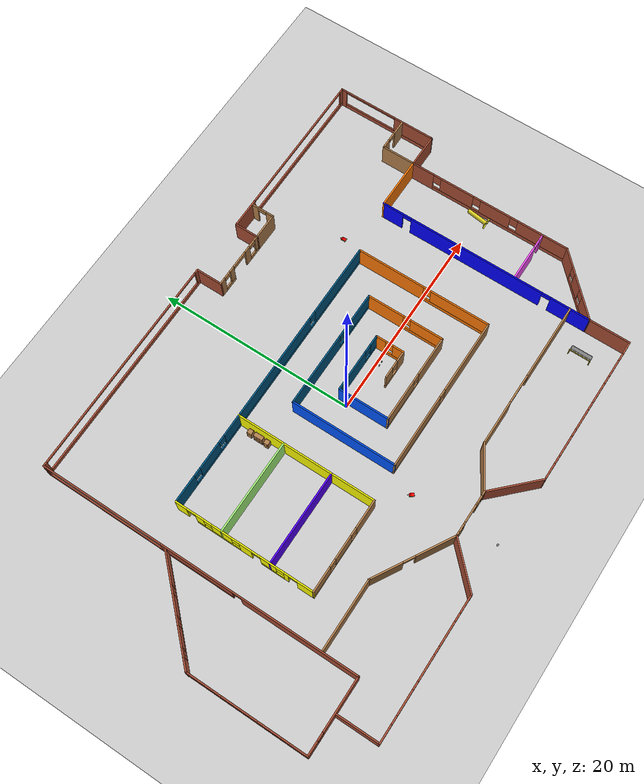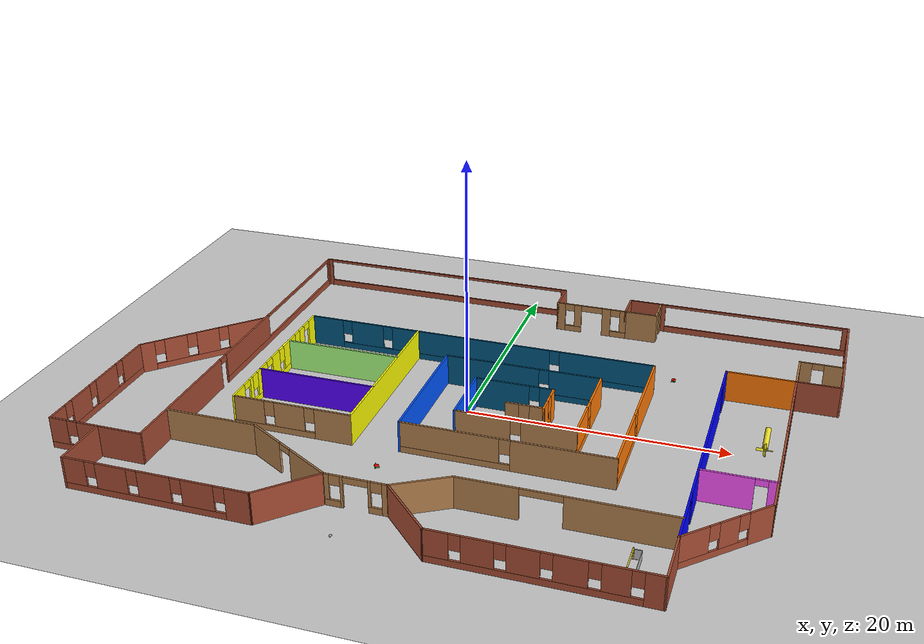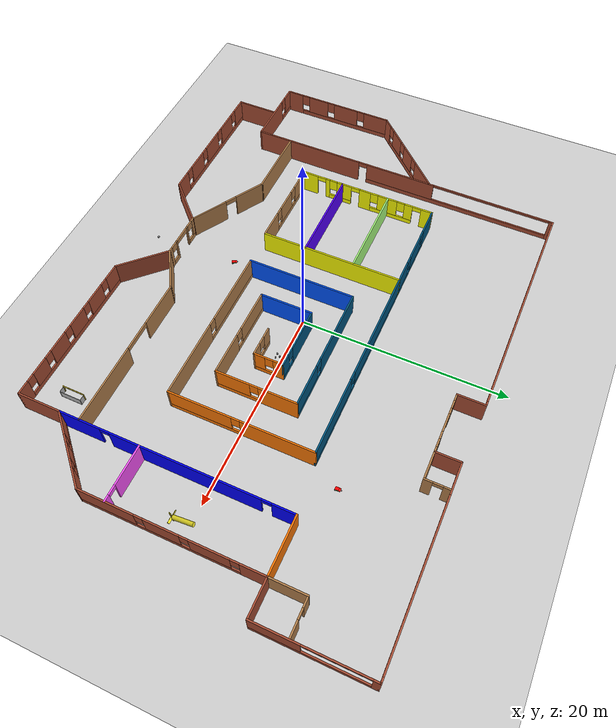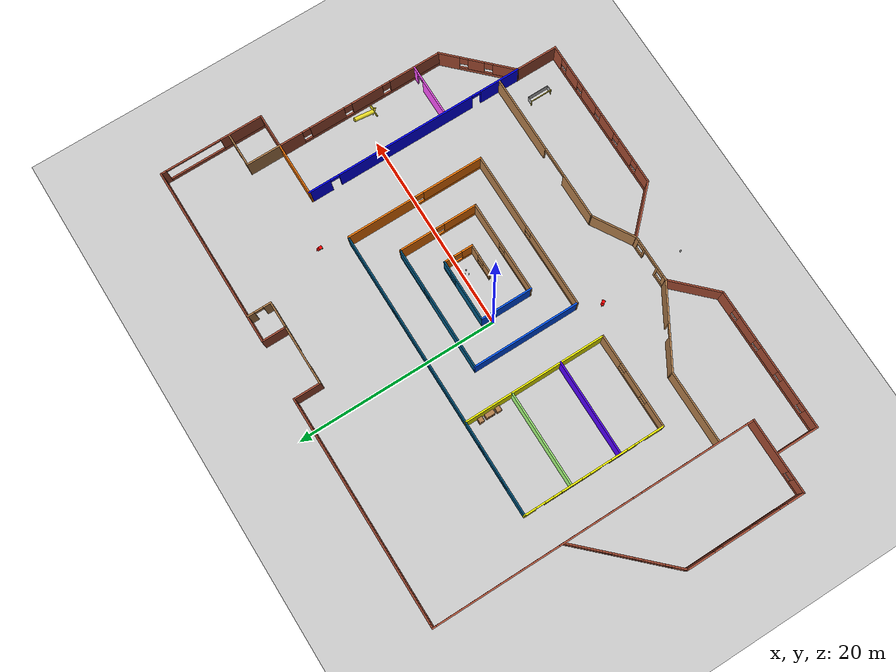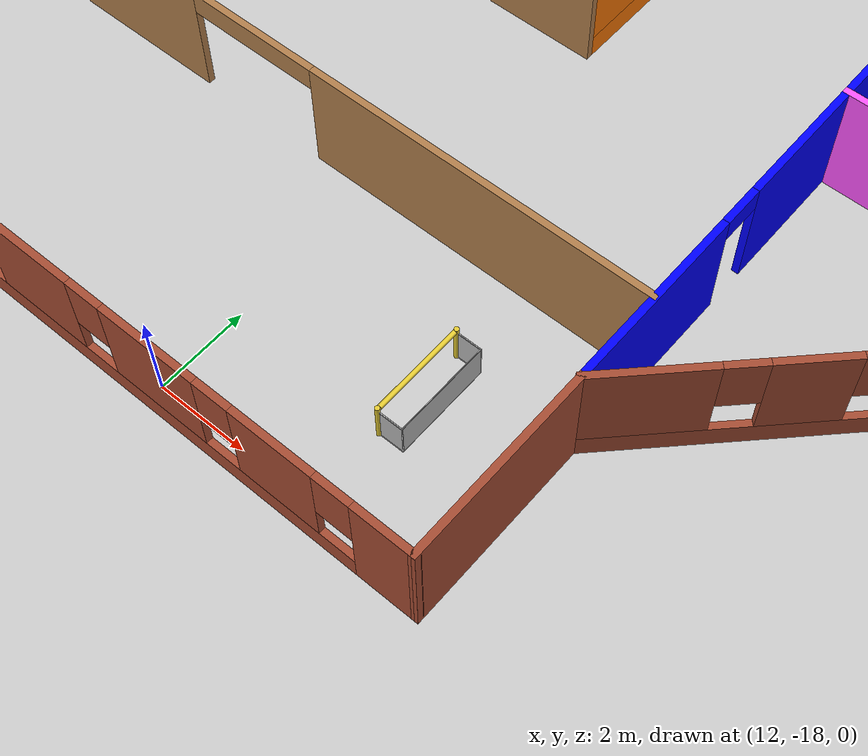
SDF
<sdf version="1.6">
 <world name="default">
  <plugin name="welcome" filename="libwelcome.so"/>
  <light name="sun" type="directional">
   <pose>0 0 10 0 -0 0</pose>
   <diffuse>0.8 0.8 0.8 1</diffuse>
   <specular>0.2 0.2 0.2 1</specular>
   <attenuation>
    <range>1000</range>
    <constant>0.9</constant>
    <linear>0.01</linear>
    <quadratic>0.001</quadratic>
   </attenuation>
   <direction>-0.5 0.1 -0.9</direction>
  </light>
  <model name="ground_plane">
   <static>1</static>
   <link name="link">
    <collision name="collision">
     <geometry><plane><normal>0 0 1</normal><size>100 100</size></plane></geometry>
     <surface><friction><ode><mu>100</mu><mu2>50</mu2></ode></friction></surface>
    </collision>
    <visual name="visual">
     <cast_shadows>0</cast_shadows>
     <geometry><plane><normal>0 0 1</normal><size>100 100</size></plane></geometry>
     <material>
      <script><uri>file://media/materials/scripts/gazebo.material</uri><name>Gazebo/Grey</name></script>
     </material>
    </visual>
   </link>
  </model>
  <gravity>0 0 -9.8</gravity>
  <magnetic_field>6e-06 2.3e-05 -4.2e-05</magnetic_field>
  <atmosphere type="adiabatic"/>
  <physics name="default_physics" default="0" type="ode">
   <max_step_size>0.001</max_step_size>
   <real_time_factor>1</real_time_factor>
   <real_time_update_rate>1000</real_time_update_rate>
  </physics>
  <scene><ambient>0.4 0.4 0.4 1</ambient><background>0.7 0.7 0.7 1</background><shadows>1</shadows></scene>
  <spherical_coordinates>
   <surface_model>EARTH_WGS84</surface_model>
   <latitude_deg>0</latitude_deg>
   <longitude_deg>0</longitude_deg>
   <elevation>0</elevation>
   <heading_deg>0</heading_deg>
  </spherical_coordinates>
  <model name="spiral_office">
   <link name="Wall_10">
    <pose>-8.28463 18.4006 0 0 -0 0</pose>
    <visual name="Wall_10_Visual_0">
     <pose>-11.142 0 1.25 0 -0 0</pose>
     <geometry><box><size>0.465955 0.15 2.5</size></box></geometry>
     <material>
      <script><uri>file://media/materials/scripts/gazebo.material</uri><name>Gazebo/Bricks</name></script>
      <ambient>1 1 1 1</ambient>
     </material>
     <meta><layer>0</layer></meta>
    </visual>
    <collision name="Wall_10_Collision_0">
     <geometry><box><size>0.465955 0.15 2.5</size></box></geometry>
     <pose>-11.142 0 1.25 0 -0 0</pose>
    </collision>
    <visual name="Wall_10_Visual_1">
     <pose>0.232978 0 0.25 0 -0 0</pose>
     <geometry><box><size>22.284 0.15 0.5</size></box></geometry>
     <material>
      <script><uri>file://media/materials/scripts/gazebo.material</uri><name>Gazebo/Bricks</name></script>
      <ambient>1 1 1 1</ambient>
     </material>
     <meta><layer>0</layer></meta>
    </visual>
    <collision name="Wall_10_Collision_1">
     <geometry><box><size>22.284 0.15 0.5</size></box></geometry>
     <pose>0.232978 0 0.25 0 -0 0</pose>
    </collision>
    <visual name="Wall_10_Visual_2">
     <pose>11.1279 0 1.5 0 -0 0</pose>
     <geometry><box><size>0.494199 0.15 2</size></box></geometry>
     <material>
      <script><uri>file://media/materials/scripts/gazebo.material</uri><name>Gazebo/Bricks</name></script>
      <ambient>1 1 1 1</ambient>
     </material>
     <meta><layer>0</layer></meta>
    </visual>
    <collision name="Wall_10_Collision_2">
     <geometry><box><size>0.494199 0.15 2</size></box></geometry>
     <pose>11.1279 0 1.5 0 -0 0</pose>
    </collision>
    <visual name="Wall_10_Visual_3">
     <pose>-0.014122 0 2.4 0 -0 0</pose>
     <geometry><box><size>21.7898 0.15 0.2</size></box></geometry>
     <material>
      <script><uri>file://media/materials/scripts/gazebo.material</uri><name>Gazebo/Bricks</name></script>
      <ambient>1 1 1 1</ambient>
     </material>
     <meta><layer>0</layer></meta>
    </visual>
    <collision name="Wall_10_Collision_3">
     <geometry><box><size>21.7898 0.15 0.2</size></box></geometry>
     <pose>-0.014122 0 2.4 0 -0 0</pose>
    </collision>
   </link>
   <link name="Wall_100">
    <pose>20.9892 -6.43138 0 0 -0 3.14159</pose>
    <visual name="Wall_100_Visual_0">
     <pose>-2.35489 0 1.25 0 -0 0</pose>
     <geometry><box><size>0.689225 0.15 2.5</size></box></geometry>
     <material>
      <script><uri>file://media/materials/scripts/gazebo.material</uri><name>Gazebo/Grey</name></script>
      <ambient>1 0.333333 1 1</ambient>
     </material>
     <meta><layer>0</layer></meta>
    </visual>
    <collision name="Wall_100_Collision_0">
     <geometry><box><size>0.689225 0.15 2.5</size></box></geometry>
     <pose>-2.35489 0 1.25 0 -0 0</pose>
    </collision>
    <visual name="Wall_100_Visual_1">
     <pose>0.794612 0 1.25 0 -0 0</pose>
     <geometry><box><size>3.80978 0.15 2.5</size></box></geometry>
     <material>
      <script><uri>file://media/materials/scripts/gazebo.material</uri><name>Gazebo/Grey</name></script>
      <ambient>1 0.333333 1 1</ambient>
     </material>
     <meta><layer>0</layer></meta>
    </visual>
    <collision name="Wall_100_Collision_1">
     <geometry><box><size>3.80978 0.15 2.5</size></box></geometry>
     <pose>0.794612 0 1.25 0 -0 0</pose>
    </collision>
    <visual name="Wall_100_Visual_2">
     <pose>-1.56028 0 2.25 0 -0 0</pose>
     <geometry><box><size>0.9 0.15 0.5</size></box></geometry>
     <material>
      <script><uri>file://media/materials/scripts/gazebo.material</uri><name>Gazebo/Grey</name></script>
      <ambient>1 0.333333 1 1</ambient>
     </material>
     <meta><layer>0</layer></meta>
    </visual>
    <collision name="Wall_100_Collision_2">
     <geometry><box><size>0.9 0.15 0.5</size></box></geometry>
     <pose>-1.56028 0 2.25 0 -0 0</pose>
    </collision>
   </link>
   <link name="Wall_102">
    <pose>10.7001 -12.2894 0 0 -0 3.14159</pose>
    <visual name="Wall_102_Visual_0">
     <pose>-3.79286 0 1.25 0 -0 0</pose>
     <geometry><box><size>7.82905 0.15 2.5</size></box></geometry>
     <material>
      <script><uri>file://media/materials/scripts/gazebo.material</uri><name>Gazebo/Wood</name></script>
      <ambient>1 1 1 1</ambient>
     </material>
     <meta><layer>0</layer></meta>
    </visual>
    <collision name="Wall_102_Collision_0">
     <geometry><box><size>7.82905 0.15 2.5</size></box></geometry>
     <pose>-3.79286 0 1.25 0 -0 0</pose>
    </collision>
    <visual name="Wall_102_Visual_1">
     <pose>5.41453 0 1.25 0 -0 0</pose>
     <geometry><box><size>4.58572 0.15 2.5</size></box></geometry>
     <material>
      <script><uri>file://media/materials/scripts/gazebo.material</uri><name>Gazebo/Wood</name></script>
      <ambient>1 1 1 1</ambient>
     </material>
     <meta><layer>0</layer></meta>
    </visual>
    <collision name="Wall_102_Collision_1">
     <geometry><box><size>4.58572 0.15 2.5</size></box></geometry>
     <pose>5.41453 0 1.25 0 -0 0</pose>
    </collision>
    <visual name="Wall_102_Visual_2">
     <pose>1.62166 0 2.25 0 -0 0</pose>
     <geometry><box><size>3 0.15 0.5</size></box></geometry>
     <material>
      <script><uri>file://media/materials/scripts/gazebo.material</uri><name>Gazebo/Wood</name></script>
      <ambient>1 1 1 1</ambient>
     </material>
     <meta><layer>0</layer></meta>
    </visual>
    <collision name="Wall_102_Collision_2">
     <geometry><box><size>3 0.15 0.5</size></box></geometry>
     <pose>1.62166 0 2.25 0 -0 0</pose>
    </collision>
   </link>
   <link name="Wall_103">
    <collision name="Wall_103_Collision">
     <geometry><box><size>4.56386 0.15 2.5</size></box></geometry>
     <pose>0 0 1.25 0 -0 0</pose>
    </collision>
    <visual name="Wall_103_Visual">
     <pose>0 0 1.25 0 -0 0</pose>
     <geometry><box><size>4.56386 0.15 2.5</size></box></geometry>
     <material>
      <script><uri>file://media/materials/scripts/gazebo.material</uri><name>Gazebo/Wood</name></script>
      <ambient>1 1 1 1</ambient>
     </material>
     <meta><layer>0</layer></meta>
    </visual>
    <pose>1.17619 -13.4264 0 0 0 -2.60036</pose>
   </link>
   <link name="Wall_11">
    <collision name="Wall_11_Collision">
     <geometry><box><size>2.75 0.15 2.5</size></box></geometry>
     <pose>0 0 1.25 0 -0 0</pose>
    </collision>
    <visual name="Wall_11_Visual">
     <pose>0 0 1.25 0 -0 0</pose>
     <geometry><box><size>2.75 0.15 2.5</size></box></geometry>
     <material>
      <script><uri>file://media/materials/scripts/gazebo.material</uri><name>Gazebo/Bricks</name></script>
      <ambient>1 1 1 1</ambient>
     </material>
     <meta><layer>0</layer></meta>
    </visual>
    <pose>3.01537 17.1006 0 0 0 -1.5708</pose>
   </link>
   <link name="Wall_12">
    <pose>5.94037 15.8006 0 0 -0 0</pose>
    <visual name="Wall_12_Visual_0">
     <pose>-2.63334 0 1.25 0 -0 0</pose>
     <geometry><box><size>0.733327 0.15 2.5</size></box></geometry>
     <material>
      <script><uri>file://media/materials/scripts/gazebo.material</uri><name>Gazebo/Wood</name></script>
      <ambient>1 1 1 1</ambient>
     </material>
     <meta><layer>0</layer></meta>
    </visual>
    <collision name="Wall_12_Collision_0">
     <geometry><box><size>0.733327 0.15 2.5</size></box></geometry>
     <pose>-2.63334 0 1.25 0 -0 0</pose>
    </collision>
    <visual name="Wall_12_Visual_1">
     <pose>1.29307 0 1.25 0 -0 0</pose>
     <geometry><box><size>0.719491 0.15 2.5</size></box></geometry>
     <material>
      <script><uri>file://media/materials/scripts/gazebo.material</uri><name>Gazebo/Wood</name></script>
      <ambient>1 1 1 1</ambient>
     </material>
     <meta><layer>0</layer></meta>
    </visual>
    <collision name="Wall_12_Collision_1">
     <geometry><box><size>0.719491 0.15 2.5</size></box></geometry>
     <pose>1.29307 0 1.25 0 -0 0</pose>
    </collision>
    <visual name="Wall_12_Visual_2">
     <pose>-1.56667 0 0.25 0 -0 0</pose>
     <geometry><box><size>1.4 0.15 0.5</size></box></geometry>
     <material>
      <script><uri>file://media/materials/scripts/gazebo.material</uri><name>Gazebo/Wood</name></script>
      <ambient>1 1 1 1</ambient>
     </material>
     <meta><layer>0</layer></meta>
    </visual>
    <collision name="Wall_12_Collision_2">
     <geometry><box><size>1.4 0.15 0.5</size></box></geometry>
     <pose>-1.56667 0 0.25 0 -0 0</pose>
    </collision>
    <visual name="Wall_12_Visual_3">
     <pose>2.32641 0 0.25 0 -0 0</pose>
     <geometry><box><size>1.34718 0.15 0.5</size></box></geometry>
     <material>
      <script><uri>file://media/materials/scripts/gazebo.material</uri><name>Gazebo/Wood</name></script>
      <ambient>1 1 1 1</ambient>
     </material>
     <meta><layer>0</layer></meta>
    </visual>
    <collision name="Wall_12_Collision_3">
     <geometry><box><size>1.34718 0.15 0.5</size></box></geometry>
     <pose>2.32641 0 0.25 0 -0 0</pose>
    </collision>
    <visual name="Wall_12_Visual_4">
     <pose>-1.16667 0 1.5 0 -0 0</pose>
     <geometry><box><size>0.6 0.15 2</size></box></geometry>
     <material>
      <script><uri>file://media/materials/scripts/gazebo.material</uri><name>Gazebo/Wood</name></script>
      <ambient>1 1 1 1</ambient>
     </material>
     <meta><layer>0</layer></meta>
    </visual>
    <collision name="Wall_12_Collision_4">
     <geometry><box><size>0.6 0.15 2</size></box></geometry>
     <pose>-1.16667 0 1.5 0 -0 0</pose>
    </collision>
    <visual name="Wall_12_Visual_5">
     <pose>-1.16667 0 1.5 0 -0 0</pose>
     <geometry><box><size>0.6 0.15 2</size></box></geometry>
     <material>
      <script><uri>file://media/materials/scripts/gazebo.material</uri><name>Gazebo/Wood</name></script>
      <ambient>1 1 1 1</ambient>
     </material>
     <meta><layer>0</layer></meta>
    </visual>
    <collision name="Wall_12_Collision_5">
     <geometry><box><size>0.6 0.15 2</size></box></geometry>
     <pose>-1.16667 0 1.5 0 -0 0</pose>
    </collision>
    <visual name="Wall_12_Visual_6">
     <pose>2.72641 0 1.5 0 -0 0</pose>
     <geometry><box><size>0.547182 0.15 2</size></box></geometry>
     <material>
      <script><uri>file://media/materials/scripts/gazebo.material</uri><name>Gazebo/Wood</name></script>
      <ambient>1 1 1 1</ambient>
     </material>
     <meta><layer>0</layer></meta>
    </visual>
    <collision name="Wall_12_Collision_6">
     <geometry><box><size>0.547182 0.15 2</size></box></geometry>
     <pose>2.72641 0 1.5 0 -0 0</pose>
    </collision>
    <visual name="Wall_12_Visual_7">
     <pose>-1.86667 0 2.2 0 -0 0</pose>
     <geometry><box><size>0.8 0.15 0.6</size></box></geometry>
     <material>
      <script><uri>file://media/materials/scripts/gazebo.material</uri><name>Gazebo/Wood</name></script>
      <ambient>1 1 1 1</ambient>
     </material>
     <meta><layer>0</layer></meta>
    </visual>
    <collision name="Wall_12_Collision_7">
     <geometry><box><size>0.8 0.15 0.6</size></box></geometry>
     <pose>-1.86667 0 2.2 0 -0 0</pose>
    </collision>
    <visual name="Wall_12_Visual_8">
     <pose>2.05282 0 2.2 0 -0 0</pose>
     <geometry><box><size>0.8 0.15 0.6</size></box></geometry>
     <material>
      <script><uri>file://media/materials/scripts/gazebo.material</uri><name>Gazebo/Wood</name></script>
      <ambient>1 1 1 1</ambient>
     </material>
     <meta><layer>0</layer></meta>
    </visual>
    <collision name="Wall_12_Collision_8">
     <geometry><box><size>0.8 0.15 0.6</size></box></geometry>
     <pose>2.05282 0 2.2 0 -0 0</pose>
    </collision>
    <visual name="Wall_12_Visual_9">
     <pose>0.033327 0 2.25 0 -0 0</pose>
     <geometry><box><size>1.8 0.15 0.5</size></box></geometry>
     <material>
      <script><uri>file://media/materials/scripts/gazebo.material</uri><name>Gazebo/Wood</name></script>
      <ambient>1 1 1 1</ambient>
     </material>
     <meta><layer>0</layer></meta>
    </visual>
    <collision name="Wall_12_Collision_9">
     <geometry><box><size>1.8 0.15 0.5</size></box></geometry>
     <pose>0.033327 0 2.25 0 -0 0</pose>
    </collision>
    <visual name="Wall_12_Visual_10">
     <pose>0.033327 0 2.25 0 -0 0</pose>
     <geometry><box><size>1.8 0.15 0.5</size></box></geometry>
     <material>
      <script><uri>file://media/materials/scripts/gazebo.material</uri><name>Gazebo/Wood</name></script>
      <ambient>1 1 1 1</ambient>
     </material>
     <meta><layer>0</layer></meta>
    </visual>
    <collision name="Wall_12_Collision_10">
     <geometry><box><size>1.8 0.15 0.5</size></box></geometry>
     <pose>0.033327 0 2.25 0 -0 0</pose>
    </collision>
   </link>
   <link name="Wall_13">
    <collision name="Wall_13_Collision">
     <geometry><box><size>2.5 0.15 2.5</size></box></geometry>
     <pose>0 0 1.25 0 -0 0</pose>
    </collision>
    <visual name="Wall_13_Visual">
     <pose>0 0 1.25 0 -0 0</pose>
     <geometry><box><size>2.5 0.15 2.5</size></box></geometry>
     <material>
      <script><uri>file://media/materials/scripts/gazebo.material</uri><name>Gazebo/Bricks</name></script>
      <ambient>1 1 1 1</ambient>
     </material>
     <meta><layer>0</layer></meta>
    </visual>
    <pose>8.86537 16.9756 0 0 -0 1.5708</pose>
   </link>
   <link name="Wall_14">
    <pose>17.9154 18.1506 0 0 -0 0</pose>
    <visual name="Wall_14_Visual_0">
     <pose>-7.57768 0 1.25 0 -0 0</pose>
     <geometry><box><size>3.09465 0.15 2.5</size></box></geometry>
     <material>
      <script><uri>file://media/materials/scripts/gazebo.material</uri><name>Gazebo/Bricks</name></script>
      <ambient>1 1 1 1</ambient>
     </material>
     <meta><layer>0</layer></meta>
    </visual>
    <collision name="Wall_14_Collision_0">
     <geometry><box><size>3.09465 0.15 2.5</size></box></geometry>
     <pose>-7.57768 0 1.25 0 -0 0</pose>
    </collision>
    <visual name="Wall_14_Visual_1">
     <pose>1.54732 0 0.25 0 -0 0</pose>
     <geometry><box><size>15.1554 0.15 0.5</size></box></geometry>
     <material>
      <script><uri>file://media/materials/scripts/gazebo.material</uri><name>Gazebo/Bricks</name></script>
      <ambient>1 1 1 1</ambient>
     </material>
     <meta><layer>0</layer></meta>
    </visual>
    <collision name="Wall_14_Collision_1">
     <geometry><box><size>15.1554 0.15 0.5</size></box></geometry>
     <pose>1.54732 0 0.25 0 -0 0</pose>
    </collision>
    <visual name="Wall_14_Visual_2">
     <pose>8.85582 0 1.5 0 -0 0</pose>
     <geometry><box><size>0.538352 0.15 2</size></box></geometry>
     <material>
      <script><uri>file://media/materials/scripts/gazebo.material</uri><name>Gazebo/Bricks</name></script>
      <ambient>1 1 1 1</ambient>
     </material>
     <meta><layer>0</layer></meta>
    </visual>
    <collision name="Wall_14_Collision_2">
     <geometry><box><size>0.538352 0.15 2</size></box></geometry>
     <pose>8.85582 0 1.5 0 -0 0</pose>
    </collision>
    <visual name="Wall_14_Visual_3">
     <pose>1.27815 0 2.4 0 -0 0</pose>
     <geometry><box><size>14.617 0.15 0.2</size></box></geometry>
     <material>
      <script><uri>file://media/materials/scripts/gazebo.material</uri><name>Gazebo/Bricks</name></script>
      <ambient>1 1 1 1</ambient>
     </material>
     <meta><layer>0</layer></meta>
    </visual>
    <collision name="Wall_14_Collision_3">
     <geometry><box><size>14.617 0.15 0.2</size></box></geometry>
     <pose>1.27815 0 2.4 0 -0 0</pose>
    </collision>
   </link>
   <link name="Wall_15">
    <pose>26.9654 12.9756 0 0 0 -1.5708</pose>
    <visual name="Wall_15_Visual_0">
     <pose>-4.93489 0 1.25 0 -0 0</pose>
     <geometry><box><size>0.630216 0.15 2.5</size></box></geometry>
     <material>
      <script><uri>file://media/materials/scripts/gazebo.material</uri><name>Gazebo/Bricks</name></script>
      <ambient>1 1 1 1</ambient>
     </material>
     <meta><layer>0</layer></meta>
    </visual>
    <collision name="Wall_15_Collision_0">
     <geometry><box><size>0.630216 0.15 2.5</size></box></geometry>
     <pose>-4.93489 0 1.25 0 -0 0</pose>
    </collision>
    <visual name="Wall_15_Visual_1">
     <pose>0.315108 0 0.25 0 -0 0</pose>
     <geometry><box><size>9.86978 0.15 0.5</size></box></geometry>
     <material>
      <script><uri>file://media/materials/scripts/gazebo.material</uri><name>Gazebo/Bricks</name></script>
      <ambient>1 1 1 1</ambient>
     </material>
     <meta><layer>0</layer></meta>
    </visual>
    <collision name="Wall_15_Collision_1">
     <geometry><box><size>9.86978 0.15 0.5</size></box></geometry>
     <pose>0.315108 0 0.25 0 -0 0</pose>
    </collision>
    <visual name="Wall_15_Visual_2">
     <pose>3.09761 0 1.5 0 -0 0</pose>
     <geometry><box><size>4.30478 0.15 2</size></box></geometry>
     <material>
      <script><uri>file://media/materials/scripts/gazebo.material</uri><name>Gazebo/Bricks</name></script>
      <ambient>1 1 1 1</ambient>
     </material>
     <meta><layer>0</layer></meta>
    </visual>
    <collision name="Wall_15_Collision_2">
     <geometry><box><size>4.30478 0.15 2</size></box></geometry>
     <pose>3.09761 0 1.5 0 -0 0</pose>
    </collision>
    <visual name="Wall_15_Visual_3">
     <pose>-1.83728 0 2.4 0 -0 0</pose>
     <geometry><box><size>5.565 0.15 0.2</size></box></geometry>
     <material>
      <script><uri>file://media/materials/scripts/gazebo.material</uri><name>Gazebo/Bricks</name></script>
      <ambient>1 1 1 1</ambient>
     </material>
     <meta><layer>0</layer></meta>
    </visual>
    <collision name="Wall_15_Collision_3">
     <geometry><box><size>5.565 0.15 0.2</size></box></geometry>
     <pose>-1.83728 0 2.4 0 -0 0</pose>
    </collision>
   </link>
   <link name="Wall_16">
    <collision name="Wall_16_Collision">
     <geometry><box><size>3.50167 0.15 2.5</size></box></geometry>
     <pose>0 0 1.25 0 -0 0</pose>
    </collision>
    <visual name="Wall_16_Visual">
     <pose>0 0 1.25 0 -0 0</pose>
     <geometry><box><size>3.50167 0.15 2.5</size></box></geometry>
     <material>
      <script><uri>file://media/materials/scripts/gazebo.material</uri><name>Gazebo/Bricks</name></script>
      <ambient>1 1 1 1</ambient>
     </material>
     <meta><layer>0</layer></meta>
    </visual>
    <pose>25.2895 7.80063 0 0 0 -3.14159</pose>
   </link>
   <link name="Wall_17">
    <pose>23.6145 -0.624368 0 0 0 -1.5707</pose>
    <visual name="Wall_17_Visual_0">
     <pose>-7.2888 0 1.25 0 -0 0</pose>
     <geometry><box><size>2.42239 0.15 2.5</size></box></geometry>
     <material>
      <script><uri>file://media/materials/scripts/gazebo.material</uri><name>Gazebo/Bricks</name></script>
      <ambient>1 1 1 1</ambient>
     </material>
     <meta><layer>0</layer></meta>
    </visual>
    <collision name="Wall_17_Collision_0">
     <geometry><box><size>2.42239 0.15 2.5</size></box></geometry>
     <pose>-7.2888 0 1.25 0 -0 0</pose>
    </collision>
    <visual name="Wall_17_Visual_1">
     <pose>1.2112 0 0.25 0 -0 0</pose>
     <geometry><box><size>14.5776 0.15 0.5</size></box></geometry>
     <material>
      <script><uri>file://media/materials/scripts/gazebo.material</uri><name>Gazebo/Bricks</name></script>
      <ambient>1 1 1 1</ambient>
     </material>
     <meta><layer>0</layer></meta>
    </visual>
    <collision name="Wall_17_Collision_1">
     <geometry><box><size>14.5776 0.15 0.5</size></box></geometry>
     <pose>1.2112 0 0.25 0 -0 0</pose>
    </collision>
    <visual name="Wall_17_Visual_2">
     <pose>-3.48164 0 1.5 0 -0 0</pose>
     <geometry><box><size>3.59193 0.15 2</size></box></geometry>
     <material>
      <script><uri>file://media/materials/scripts/gazebo.material</uri><name>Gazebo/Bricks</name></script>
      <ambient>1 1 1 1</ambient>
     </material>
     <meta><layer>0</layer></meta>
    </visual>
    <collision name="Wall_17_Collision_2">
     <geometry><box><size>3.59193 0.15 2</size></box></geometry>
     <pose>-3.48164 0 1.5 0 -0 0</pose>
    </collision>
    <visual name="Wall_17_Visual_3">
     <pose>0.737324 0 1.5 0 -0 0</pose>
     <geometry><box><size>3.246 0.15 2</size></box></geometry>
     <material>
      <script><uri>file://media/materials/scripts/gazebo.material</uri><name>Gazebo/Bricks</name></script>
      <ambient>1 1 1 1</ambient>
     </material>
     <meta><layer>0</layer></meta>
    </visual>
    <collision name="Wall_17_Collision_3">
     <geometry><box><size>3.246 0.15 2</size></box></geometry>
     <pose>0.737324 0 1.5 0 -0 0</pose>
    </collision>
    <visual name="Wall_17_Visual_4">
     <pose>5.83016 0 1.5 0 -0 0</pose>
     <geometry><box><size>5.33968 0.15 2</size></box></geometry>
     <material>
      <script><uri>file://media/materials/scripts/gazebo.material</uri><name>Gazebo/Bricks</name></script>
      <ambient>1 1 1 1</ambient>
     </material>
     <meta><layer>0</layer></meta>
    </visual>
    <collision name="Wall_17_Collision_4">
     <geometry><box><size>5.33968 0.15 2</size></box></geometry>
     <pose>5.83016 0 1.5 0 -0 0</pose>
    </collision>
    <visual name="Wall_17_Visual_5">
     <pose>-5.67761 0 1.9 0 -0 0</pose>
     <geometry><box><size>0.8 0.15 1.2</size></box></geometry>
     <material>
      <script><uri>file://media/materials/scripts/gazebo.material</uri><name>Gazebo/Bricks</name></script>
      <ambient>1 1 1 1</ambient>
     </material>
     <meta><layer>0</layer></meta>
    </visual>
    <collision name="Wall_17_Collision_5">
     <geometry><box><size>0.8 0.15 1.2</size></box></geometry>
     <pose>-5.67761 0 1.9 0 -0 0</pose>
    </collision>
    <visual name="Wall_17_Visual_6">
     <pose>-1.28568 0 1.9 0 -0 0</pose>
     <geometry><box><size>0.8 0.15 1.2</size></box></geometry>
     <material>
      <script><uri>file://media/materials/scripts/gazebo.material</uri><name>Gazebo/Bricks</name></script>
      <ambient>1 1 1 1</ambient>
     </material>
     <meta><layer>0</layer></meta>
    </visual>
    <collision name="Wall_17_Collision_6">
     <geometry><box><size>0.8 0.15 1.2</size></box></geometry>
     <pose>-1.28568 0 1.9 0 -0 0</pose>
    </collision>
    <visual name="Wall_17_Visual_7">
     <pose>2.76032 0 1.9 0 -0 0</pose>
     <geometry><box><size>0.8 0.15 1.2</size></box></geometry>
     <material>
      <script><uri>file://media/materials/scripts/gazebo.material</uri><name>Gazebo/Bricks</name></script>
      <ambient>1 1 1 1</ambient>
     </material>
     <meta><layer>0</layer></meta>
    </visual>
    <collision name="Wall_17_Collision_7">
     <geometry><box><size>0.8 0.15 1.2</size></box></geometry>
     <pose>2.76032 0 1.9 0 -0 0</pose>
    </collision>
   </link>
   <link name="Wall_18">
    <pose>20.99 -11.6749 0 0 0 -2.35616</pose>
    <visual name="Wall_18_Visual_0">
     <pose>-2.76411 0 1.25 0 -0 0</pose>
     <geometry><box><size>2.04759 0.15 2.5</size></box></geometry>
     <material>
      <script><uri>file://media/materials/scripts/gazebo.material</uri><name>Gazebo/Bricks</name></script>
      <ambient>1 1 1 1</ambient>
     </material>
     <meta><layer>0</layer></meta>
    </visual>
    <collision name="Wall_18_Collision_0">
     <geometry><box><size>2.04759 0.15 2.5</size></box></geometry>
     <pose>-2.76411 0 1.25 0 -0 0</pose>
    </collision>
    <visual name="Wall_18_Visual_1">
     <pose>1.02379 0 0.25 0 -0 0</pose>
     <geometry><box><size>5.52823 0.15 0.5</size></box></geometry>
     <material>
      <script><uri>file://media/materials/scripts/gazebo.material</uri><name>Gazebo/Bricks</name></script>
      <ambient>1 1 1 1</ambient>
     </material>
     <meta><layer>0</layer></meta>
    </visual>
    <collision name="Wall_18_Collision_1">
     <geometry><box><size>5.52823 0.15 0.5</size></box></geometry>
     <pose>1.02379 0 0.25 0 -0 0</pose>
    </collision>
    <visual name="Wall_18_Visual_2">
     <pose>-0.167532 0 1.5 0 -0 0</pose>
     <geometry><box><size>1.54558 0.15 2</size></box></geometry>
     <material>
      <script><uri>file://media/materials/scripts/gazebo.material</uri><name>Gazebo/Bricks</name></script>
      <ambient>1 1 1 1</ambient>
     </material>
     <meta><layer>0</layer></meta>
    </visual>
    <collision name="Wall_18_Collision_2">
     <geometry><box><size>1.54558 0.15 2</size></box></geometry>
     <pose>-0.167532 0 1.5 0 -0 0</pose>
    </collision>
    <visual name="Wall_18_Visual_3">
     <pose>2.59658 0 1.5 0 -0 0</pose>
     <geometry><box><size>2.38265 0.15 2</size></box></geometry>
     <material>
      <script><uri>file://media/materials/scripts/gazebo.material</uri><name>Gazebo/Bricks</name></script>
      <ambient>1 1 1 1</ambient>
     </material>
     <meta><layer>0</layer></meta>
    </visual>
    <collision name="Wall_18_Collision_3">
     <geometry><box><size>2.38265 0.15 2</size></box></geometry>
     <pose>2.59658 0 1.5 0 -0 0</pose>
    </collision>
    <visual name="Wall_18_Visual_4">
     <pose>-1.34032 0 1.9 0 -0 0</pose>
     <geometry><box><size>0.8 0.15 1.2</size></box></geometry>
     <material>
      <script><uri>file://media/materials/scripts/gazebo.material</uri><name>Gazebo/Bricks</name></script>
      <ambient>1 1 1 1</ambient>
     </material>
     <meta><layer>0</layer></meta>
    </visual>
    <collision name="Wall_18_Collision_4">
     <geometry><box><size>0.8 0.15 1.2</size></box></geometry>
     <pose>-1.34032 0 1.9 0 -0 0</pose>
    </collision>
    <visual name="Wall_18_Visual_5">
     <pose>1.00526 0 1.9 0 -0 0</pose>
     <geometry><box><size>0.8 0.15 1.2</size></box></geometry>
     <material>
      <script><uri>file://media/materials/scripts/gazebo.material</uri><name>Gazebo/Bricks</name></script>
      <ambient>1 1 1 1</ambient>
     </material>
     <meta><layer>0</layer></meta>
    </visual>
    <collision name="Wall_18_Collision_5">
     <geometry><box><size>0.8 0.15 1.2</size></box></geometry>
     <pose>1.00526 0 1.9 0 -0 0</pose>
    </collision>
   </link>
   <link name="Wall_19">
    <collision name="Wall_19_Collision">
     <geometry><box><size>4.25 0.15 2.5</size></box></geometry>
     <pose>0 0 1.25 0 -0 0</pose>
    </collision>
    <visual name="Wall_19_Visual">
     <pose>0 0 1.25 0 -0 0</pose>
     <geometry><box><size>4.25 0.15 2.5</size></box></geometry>
     <material>
      <script><uri>file://media/materials/scripts/gazebo.material</uri><name>Gazebo/Bricks</name></script>
      <ambient>1 1 1 1</ambient>
     </material>
     <meta><layer>0</layer></meta>
    </visual>
    <pose>18.3647 -16.3504 0 0 0 -1.5708</pose>
   </link>
   <link name="Wall_20">
    <pose>10.7162 -18.3734 0 0 -0 3.13806</pose>
    <visual name="Wall_20_Visual_0">
     <pose>-7.04407 0 1.25 0 -0 0</pose>
     <geometry><box><size>1.35851 0.15 2.5</size></box></geometry>
     <material>
      <script><uri>file://media/materials/scripts/gazebo.material</uri><name>Gazebo/Bricks</name></script>
      <ambient>1 1 1 1</ambient>
     </material>
     <meta><layer>0</layer></meta>
    </visual>
    <collision name="Wall_20_Collision_0">
     <geometry><box><size>1.35851 0.15 2.5</size></box></geometry>
     <pose>-7.04407 0 1.25 0 -0 0</pose>
    </collision>
    <visual name="Wall_20_Visual_1">
     <pose>0.679257 0 0.25 0 -0 0</pose>
     <geometry><box><size>14.0881 0.15 0.5</size></box></geometry>
     <material>
      <script><uri>file://media/materials/scripts/gazebo.material</uri><name>Gazebo/Bricks</name></script>
      <ambient>1 1 1 1</ambient>
     </material>
     <meta><layer>0</layer></meta>
    </visual>
    <collision name="Wall_20_Collision_1">
     <geometry><box><size>14.0881 0.15 0.5</size></box></geometry>
     <pose>0.679257 0 0.25 0 -0 0</pose>
    </collision>
    <visual name="Wall_20_Visual_2">
     <pose>-4.65396 0 1.5 0 -0 0</pose>
     <geometry><box><size>1.8217 0.15 2</size></box></geometry>
     <material>
      <script><uri>file://media/materials/scripts/gazebo.material</uri><name>Gazebo/Bricks</name></script>
      <ambient>1 1 1 1</ambient>
     </material>
     <meta><layer>0</layer></meta>
    </visual>
    <collision name="Wall_20_Collision_2">
     <geometry><box><size>1.8217 0.15 2</size></box></geometry>
     <pose>-4.65396 0 1.5 0 -0 0</pose>
    </collision>
    <visual name="Wall_20_Visual_3">
     <pose>-1.84491 0 1.5 0 -0 0</pose>
     <geometry><box><size>2.19639 0.15 2</size></box></geometry>
     <material>
      <script><uri>file://media/materials/scripts/gazebo.material</uri><name>Gazebo/Bricks</name></script>
      <ambient>1 1 1 1</ambient>
     </material>
     <meta><layer>0</layer></meta>
    </visual>
    <collision name="Wall_20_Collision_3">
     <geometry><box><size>2.19639 0.15 2</size></box></geometry>
     <pose>-1.84491 0 1.5 0 -0 0</pose>
    </collision>
    <visual name="Wall_20_Visual_4">
     <pose>1.12473 0 1.5 0 -0 0</pose>
     <geometry><box><size>2.14289 0.15 2</size></box></geometry>
     <material>
      <script><uri>file://media/materials/scripts/gazebo.material</uri><name>Gazebo/Bricks</name></script>
      <ambient>1 1 1 1</ambient>
     </material>
     <meta><layer>0</layer></meta>
    </visual>
    <collision name="Wall_20_Collision_4">
     <geometry><box><size>2.14289 0.15 2</size></box></geometry>
     <pose>1.12473 0 1.5 0 -0 0</pose>
    </collision>
    <visual name="Wall_20_Visual_5">
     <pose>4.06762 0 1.5 0 -0 0</pose>
     <geometry><box><size>2.14289 0.15 2</size></box></geometry>
     <material>
      <script><uri>file://media/materials/scripts/gazebo.material</uri><name>Gazebo/Bricks</name></script>
      <ambient>1 1 1 1</ambient>
     </material>
     <meta><layer>0</layer></meta>
    </visual>
    <collision name="Wall_20_Collision_5">
     <geometry><box><size>2.14289 0.15 2</size></box></geometry>
     <pose>4.06762 0 1.5 0 -0 0</pose>
    </collision>
    <visual name="Wall_20_Visual_6">
     <pose>6.8312 0 1.5 0 -0 0</pose>
     <geometry><box><size>1.78426 0.15 2</size></box></geometry>
     <material>
      <script><uri>file://media/materials/scripts/gazebo.material</uri><name>Gazebo/Bricks</name></script>
      <ambient>1 1 1 1</ambient>
     </material>
     <meta><layer>0</layer></meta>
    </visual>
    <collision name="Wall_20_Collision_6">
     <geometry><box><size>1.78426 0.15 2</size></box></geometry>
     <pose>6.8312 0 1.5 0 -0 0</pose>
    </collision>
    <visual name="Wall_20_Visual_7">
     <pose>-5.96481 0 1.9 0 -0 0</pose>
     <geometry><box><size>0.8 0.15 1.2</size></box></geometry>
     <material>
      <script><uri>file://media/materials/scripts/gazebo.material</uri><name>Gazebo/Bricks</name></script>
      <ambient>1 1 1 1</ambient>
     </material>
     <meta><layer>0</layer></meta>
    </visual>
    <collision name="Wall_20_Collision_7">
     <geometry><box><size>0.8 0.15 1.2</size></box></geometry>
     <pose>-5.96481 0 1.9 0 -0 0</pose>
    </collision>
    <visual name="Wall_20_Visual_8">
     <pose>-3.34311 0 1.9 0 -0 0</pose>
     <geometry><box><size>0.8 0.15 1.2</size></box></geometry>
     <material>
      <script><uri>file://media/materials/scripts/gazebo.material</uri><name>Gazebo/Bricks</name></script>
      <ambient>1 1 1 1</ambient>
     </material>
     <meta><layer>0</layer></meta>
    </visual>
    <collision name="Wall_20_Collision_8">
     <geometry><box><size>0.8 0.15 1.2</size></box></geometry>
     <pose>-3.34311 0 1.9 0 -0 0</pose>
    </collision>
    <visual name="Wall_20_Visual_9">
     <pose>-0.346715 0 1.9 0 -0 0</pose>
     <geometry><box><size>0.8 0.15 1.2</size></box></geometry>
     <material>
      <script><uri>file://media/materials/scripts/gazebo.material</uri><name>Gazebo/Bricks</name></script>
      <ambient>1 1 1 1</ambient>
     </material>
     <meta><layer>0</layer></meta>
    </visual>
    <collision name="Wall_20_Collision_9">
     <geometry><box><size>0.8 0.15 1.2</size></box></geometry>
     <pose>-0.346715 0 1.9 0 -0 0</pose>
    </collision>
    <visual name="Wall_20_Visual_10">
     <pose>2.59618 0 1.9 0 -0 0</pose>
     <geometry><box><size>0.8 0.15 1.2</size></box></geometry>
     <material>
      <script><uri>file://media/materials/scripts/gazebo.material</uri><name>Gazebo/Bricks</name></script>
      <ambient>1 1 1 1</ambient>
     </material>
     <meta><layer>0</layer></meta>
    </visual>
    <collision name="Wall_20_Collision_10">
     <geometry><box><size>0.8 0.15 1.2</size></box></geometry>
     <pose>2.59618 0 1.9 0 -0 0</pose>
    </collision>
    <visual name="Wall_20_Visual_11">
     <pose>5.53907 0 1.9 0 -0 0</pose>
     <geometry><box><size>0.8 0.15 1.2</size></box></geometry>
     <material>
      <script><uri>file://media/materials/scripts/gazebo.material</uri><name>Gazebo/Bricks</name></script>
      <ambient>1 1 1 1</ambient>
     </material>
     <meta><layer>0</layer></meta>
    </visual>
    <collision name="Wall_20_Collision_11">
     <geometry><box><size>0.8 0.15 1.2</size></box></geometry>
     <pose>5.53907 0 1.9 0 -0 0</pose>
    </collision>
   </link>
   <link name="Wall_21">
    <collision name="Wall_21_Collision">
     <geometry><box><size>5.5 0.15 2.5</size></box></geometry>
     <pose>0 0 1.25 0 -0 0</pose>
    </collision>
    <visual name="Wall_21_Visual">
     <pose>0 0 1.25 0 -0 0</pose>
     <geometry><box><size>5.5 0.15 2.5</size></box></geometry>
     <material>
      <script><uri>file://media/materials/scripts/gazebo.material</uri><name>Gazebo/Bricks</name></script>
      <ambient>1 1 1 1</ambient>
     </material>
     <meta><layer>0</layer></meta>
    </visual>
    <pose>1.17619 -16.4549 0 0 -0 2.35619</pose>
   </link>
   <link name="Wall_22">
    <pose>-3.0151 -14.5635 0 0 0 -3.14155</pose>
    <visual name="Wall_22_Visual_0">
     <pose>-2.1319 0 1.25 0 -0 0</pose>
     <geometry><box><size>0.486208 0.15 2.5</size></box></geometry>
     <material>
      <script><uri>file://media/materials/scripts/gazebo.material</uri><name>Gazebo/Wood</name></script>
      <ambient>1 1 1 1</ambient>
     </material>
     <meta><layer>0</layer></meta>
    </visual>
    <collision name="Wall_22_Collision_0">
     <geometry><box><size>0.486208 0.15 2.5</size></box></geometry>
     <pose>-2.1319 0 1.25 0 -0 0</pose>
    </collision>
    <visual name="Wall_22_Visual_1">
     <pose>1.01121 0 1.25 0 -0 0</pose>
     <geometry><box><size>0.2 0.15 2.5</size></box></geometry>
     <material>
      <script><uri>file://media/materials/scripts/gazebo.material</uri><name>Gazebo/Wood</name></script>
      <ambient>1 1 1 1</ambient>
     </material>
     <meta><layer>0</layer></meta>
    </visual>
    <collision name="Wall_22_Collision_1">
     <geometry><box><size>0.2 0.15 2.5</size></box></geometry>
     <pose>1.01121 0 1.25 0 -0 0</pose>
    </collision>
    <visual name="Wall_22_Visual_2">
     <pose>-1.38879 0 0.25 0 -0 0</pose>
     <geometry><box><size>1 0.15 0.5</size></box></geometry>
     <material>
      <script><uri>file://media/materials/scripts/gazebo.material</uri><name>Gazebo/Wood</name></script>
      <ambient>1 1 1 1</ambient>
     </material>
     <meta><layer>0</layer></meta>
    </visual>
    <collision name="Wall_22_Collision_2">
     <geometry><box><size>1 0.15 0.5</size></box></geometry>
     <pose>-1.38879 0 0.25 0 -0 0</pose>
    </collision>
    <visual name="Wall_22_Visual_3">
     <pose>1.7431 0 0.25 0 -0 0</pose>
     <geometry><box><size>1.26379 0.15 0.5</size></box></geometry>
     <material>
      <script><uri>file://media/materials/scripts/gazebo.material</uri><name>Gazebo/Wood</name></script>
      <ambient>1 1 1 1</ambient>
     </material>
     <meta><layer>0</layer></meta>
    </visual>
    <collision name="Wall_22_Collision_3">
     <geometry><box><size>1.26379 0.15 0.5</size></box></geometry>
     <pose>1.7431 0 0.25 0 -0 0</pose>
    </collision>
    <visual name="Wall_22_Visual_4">
     <pose>-0.988792 0 1.5 0 -0 0</pose>
     <geometry><box><size>0.2 0.15 2</size></box></geometry>
     <material>
      <script><uri>file://media/materials/scripts/gazebo.material</uri><name>Gazebo/Wood</name></script>
      <ambient>1 1 1 1</ambient>
     </material>
     <meta><layer>0</layer></meta>
    </visual>
    <collision name="Wall_22_Collision_4">
     <geometry><box><size>0.2 0.15 2</size></box></geometry>
     <pose>-0.988792 0 1.5 0 -0 0</pose>
    </collision>
    <visual name="Wall_22_Visual_5">
     <pose>-0.988792 0 1.5 0 -0 0</pose>
     <geometry><box><size>0.2 0.15 2</size></box></geometry>
     <material>
      <script><uri>file://media/materials/scripts/gazebo.material</uri><name>Gazebo/Wood</name></script>
      <ambient>1 1 1 1</ambient>
     </material>
     <meta><layer>0</layer></meta>
    </visual>
    <collision name="Wall_22_Collision_5">
     <geometry><box><size>0.2 0.15 2</size></box></geometry>
     <pose>-0.988792 0 1.5 0 -0 0</pose>
    </collision>
    <visual name="Wall_22_Visual_6">
     <pose>2.1431 0 1.5 0 -0 0</pose>
     <geometry><box><size>0.463792 0.15 2</size></box></geometry>
     <material>
      <script><uri>file://media/materials/scripts/gazebo.material</uri><name>Gazebo/Wood</name></script>
      <ambient>1 1 1 1</ambient>
     </material>
     <meta><layer>0</layer></meta>
    </visual>
    <collision name="Wall_22_Collision_6">
     <geometry><box><size>0.463792 0.15 2</size></box></geometry>
     <pose>2.1431 0 1.5 0 -0 0</pose>
    </collision>
    <visual name="Wall_22_Visual_7">
     <pose>-1.48879 0 2.1 0 -0 0</pose>
     <geometry><box><size>0.8 0.15 0.8</size></box></geometry>
     <material>
      <script><uri>file://media/materials/scripts/gazebo.material</uri><name>Gazebo/Wood</name></script>
      <ambient>1 1 1 1</ambient>
     </material>
     <meta><layer>0</layer></meta>
    </visual>
    <collision name="Wall_22_Collision_7">
     <geometry><box><size>0.8 0.15 0.8</size></box></geometry>
     <pose>-1.48879 0 2.1 0 -0 0</pose>
    </collision>
    <visual name="Wall_22_Visual_8">
     <pose>1.51121 0 2.1 0 -0 0</pose>
     <geometry><box><size>0.8 0.15 0.8</size></box></geometry>
     <material>
      <script><uri>file://media/materials/scripts/gazebo.material</uri><name>Gazebo/Wood</name></script>
      <ambient>1 1 1 1</ambient>
     </material>
     <meta><layer>0</layer></meta>
    </visual>
    <collision name="Wall_22_Collision_8">
     <geometry><box><size>0.8 0.15 0.8</size></box></geometry>
     <pose>1.51121 0 2.1 0 -0 0</pose>
    </collision>
    <visual name="Wall_22_Visual_9">
     <pose>0.011208 0 2.25 0 -0 0</pose>
     <geometry><box><size>1.8 0.15 0.5</size></box></geometry>
     <material>
      <script><uri>file://media/materials/scripts/gazebo.material</uri><name>Gazebo/Wood</name></script>
      <ambient>1 1 1 1</ambient>
     </material>
     <meta><layer>0</layer></meta>
    </visual>
    <collision name="Wall_22_Collision_9">
     <geometry><box><size>1.8 0.15 0.5</size></box></geometry>
     <pose>0.011208 0 2.25 0 -0 0</pose>
    </collision>
    <visual name="Wall_22_Visual_10">
     <pose>0.011208 0 2.25 0 -0 0</pose>
     <geometry><box><size>1.8 0.15 0.5</size></box></geometry>
     <material>
      <script><uri>file://media/materials/scripts/gazebo.material</uri><name>Gazebo/Wood</name></script>
      <ambient>1 1 1 1</ambient>
     </material>
     <meta><layer>0</layer></meta>
    </visual>
    <collision name="Wall_22_Collision_10">
     <geometry><box><size>1.8 0.15 0.5</size></box></geometry>
     <pose>0.011208 0 2.25 0 -0 0</pose>
    </collision>
   </link>
   <link name="Wall_23">
    <collision name="Wall_23_Collision">
     <geometry><box><size>5.25 0.15 2.5</size></box></geometry>
     <pose>0 0 1.25 0 -0 0</pose>
    </collision>
    <visual name="Wall_23_Visual">
     <pose>0 0 1.25 0 -0 0</pose>
     <geometry><box><size>5.25 0.15 2.5</size></box></geometry>
     <material>
      <script><uri>file://media/materials/scripts/gazebo.material</uri><name>Gazebo/Bricks</name></script>
      <ambient>1 1 1 1</ambient>
     </material>
     <meta><layer>0</layer></meta>
    </visual>
    <pose>-7.11801 -16.3667 0 0 0 -2.35619</pose>
   </link>
   <link name="Wall_24">
    <pose>-15.9711 -18.1698 0 0 -0 3.14159</pose>
    <visual name="Wall_24_Visual_0">
     <pose>-6.17797 0 1.25 0 -0 0</pose>
     <geometry><box><size>1.89406 0.15 2.5</size></box></geometry>
     <material>
      <script><uri>file://media/materials/scripts/gazebo.material</uri><name>Gazebo/Bricks</name></script>
      <ambient>1 1 1 1</ambient>
     </material>
     <meta><layer>0</layer></meta>
    </visual>
    <collision name="Wall_24_Collision_0">
     <geometry><box><size>1.89406 0.15 2.5</size></box></geometry>
     <pose>-6.17797 0 1.25 0 -0 0</pose>
    </collision>
    <visual name="Wall_24_Visual_1">
     <pose>0.947032 0 0.25 0 -0 0</pose>
     <geometry><box><size>12.3559 0.15 0.5</size></box></geometry>
     <material>
      <script><uri>file://media/materials/scripts/gazebo.material</uri><name>Gazebo/Bricks</name></script>
      <ambient>1 1 1 1</ambient>
     </material>
     <meta><layer>0</layer></meta>
    </visual>
    <collision name="Wall_24_Collision_1">
     <geometry><box><size>12.3559 0.15 0.5</size></box></geometry>
     <pose>0.947032 0 0.25 0 -0 0</pose>
    </collision>
    <visual name="Wall_24_Visual_2">
     <pose>-3.22586 0 1.5 0 -0 0</pose>
     <geometry><box><size>2.41015 0.15 2</size></box></geometry>
     <material>
      <script><uri>file://media/materials/scripts/gazebo.material</uri><name>Gazebo/Bricks</name></script>
      <ambient>1 1 1 1</ambient>
     </material>
     <meta><layer>0</layer></meta>
    </visual>
    <collision name="Wall_24_Collision_2">
     <geometry><box><size>2.41015 0.15 2</size></box></geometry>
     <pose>-3.22586 0 1.5 0 -0 0</pose>
    </collision>
    <visual name="Wall_24_Visual_3">
     <pose>0.037792 0 1.5 0 -0 0</pose>
     <geometry><box><size>2.51715 0.15 2</size></box></geometry>
     <material>
      <script><uri>file://media/materials/scripts/gazebo.material</uri><name>Gazebo/Bricks</name></script>
      <ambient>1 1 1 1</ambient>
     </material>
     <meta><layer>0</layer></meta>
    </visual>
    <collision name="Wall_24_Collision_3">
     <geometry><box><size>2.51715 0.15 2</size></box></geometry>
     <pose>0.037792 0 1.5 0 -0 0</pose>
    </collision>
    <visual name="Wall_24_Visual_4">
     <pose>3.30145 0 1.5 0 -0 0</pose>
     <geometry><box><size>2.41015 0.15 2</size></box></geometry>
     <material>
      <script><uri>file://media/materials/scripts/gazebo.material</uri><name>Gazebo/Bricks</name></script>
      <ambient>1 1 1 1</ambient>
     </material>
     <meta><layer>0</layer></meta>
    </visual>
    <collision name="Wall_24_Collision_4">
     <geometry><box><size>2.41015 0.15 2</size></box></geometry>
     <pose>3.30145 0 1.5 0 -0 0</pose>
    </collision>
    <visual name="Wall_24_Visual_5">
     <pose>6.21576 0 1.5 0 -0 0</pose>
     <geometry><box><size>1.81848 0.15 2</size></box></geometry>
     <material>
      <script><uri>file://media/materials/scripts/gazebo.material</uri><name>Gazebo/Bricks</name></script>
      <ambient>1 1 1 1</ambient>
     </material>
     <meta><layer>0</layer></meta>
    </visual>
    <collision name="Wall_24_Collision_5">
     <geometry><box><size>1.81848 0.15 2</size></box></geometry>
     <pose>6.21576 0 1.5 0 -0 0</pose>
    </collision>
    <visual name="Wall_24_Visual_6">
     <pose>-4.83094 0 1.9 0 -0 0</pose>
     <geometry><box><size>0.8 0.15 1.2</size></box></geometry>
     <material>
      <script><uri>file://media/materials/scripts/gazebo.material</uri><name>Gazebo/Bricks</name></script>
      <ambient>1 1 1 1</ambient>
     </material>
     <meta><layer>0</layer></meta>
    </visual>
    <collision name="Wall_24_Collision_6">
     <geometry><box><size>0.8 0.15 1.2</size></box></geometry>
     <pose>-4.83094 0 1.9 0 -0 0</pose>
    </collision>
    <visual name="Wall_24_Visual_7">
     <pose>-1.62078 0 1.9 0 -0 0</pose>
     <geometry><box><size>0.8 0.15 1.2</size></box></geometry>
     <material>
      <script><uri>file://media/materials/scripts/gazebo.material</uri><name>Gazebo/Bricks</name></script>
      <ambient>1 1 1 1</ambient>
     </material>
     <meta><layer>0</layer></meta>
    </visual>
    <collision name="Wall_24_Collision_7">
     <geometry><box><size>0.8 0.15 1.2</size></box></geometry>
     <pose>-1.62078 0 1.9 0 -0 0</pose>
    </collision>
    <visual name="Wall_24_Visual_8">
     <pose>1.69637 0 1.9 0 -0 0</pose>
     <geometry><box><size>0.8 0.15 1.2</size></box></geometry>
     <material>
      <script><uri>file://media/materials/scripts/gazebo.material</uri><name>Gazebo/Bricks</name></script>
      <ambient>1 1 1 1</ambient>
     </material>
     <meta><layer>0</layer></meta>
    </visual>
    <collision name="Wall_24_Collision_8">
     <geometry><box><size>0.8 0.15 1.2</size></box></geometry>
     <pose>1.69637 0 1.9 0 -0 0</pose>
    </collision>
    <visual name="Wall_24_Visual_9">
     <pose>4.90652 0 1.9 0 -0 0</pose>
     <geometry><box><size>0.8 0.15 1.2</size></box></geometry>
     <material>
      <script><uri>file://media/materials/scripts/gazebo.material</uri><name>Gazebo/Bricks</name></script>
      <ambient>1 1 1 1</ambient>
     </material>
     <meta><layer>0</layer></meta>
    </visual>
    <collision name="Wall_24_Collision_9">
     <geometry><box><size>0.8 0.15 1.2</size></box></geometry>
     <pose>4.90652 0 1.9 0 -0 0</pose>
    </collision>
   </link>
   <link name="Wall_25">
    <collision name="Wall_25_Collision">
     <geometry><box><size>4.25 0.15 2.5</size></box></geometry>
     <pose>0 0 1.25 0 -0 0</pose>
    </collision>
    <visual name="Wall_25_Visual">
     <pose>0 0 1.25 0 -0 0</pose>
     <geometry><box><size>4.25 0.15 2.5</size></box></geometry>
     <material>
      <script><uri>file://media/materials/scripts/gazebo.material</uri><name>Gazebo/Bricks</name></script>
      <ambient>1 1 1 1</ambient>
     </material>
     <meta><layer>0</layer></meta>
    </visual>
    <pose>-23.0211 -16.1198 0 0 -0 1.5708</pose>
   </link>
   <link name="Wall_27">
    <pose>-8.9041 -12.476 0 0 -0 2.61479</pose>
    <visual name="Wall_27_Visual_0">
     <pose>-2.23349 0 1.25 0 -0 0</pose>
     <geometry><box><size>3.98736 0.15 2.5</size></box></geometry>
     <material>
      <script><uri>file://media/materials/scripts/gazebo.material</uri><name>Gazebo/Wood</name></script>
      <ambient>1 1 1 1</ambient>
     </material>
     <meta><layer>0</layer></meta>
    </visual>
    <collision name="Wall_27_Collision_0">
     <geometry><box><size>3.98736 0.15 2.5</size></box></geometry>
     <pose>-2.23349 0 1.25 0 -0 0</pose>
    </collision>
    <visual name="Wall_27_Visual_1">
     <pose>2.59368 0 1.25 0 -0 0</pose>
     <geometry><box><size>3.26697 0.15 2.5</size></box></geometry>
     <material>
      <script><uri>file://media/materials/scripts/gazebo.material</uri><name>Gazebo/Wood</name></script>
      <ambient>1 1 1 1</ambient>
     </material>
     <meta><layer>0</layer></meta>
    </visual>
    <collision name="Wall_27_Collision_1">
     <geometry><box><size>3.26697 0.15 2.5</size></box></geometry>
     <pose>2.59368 0 1.25 0 -0 0</pose>
    </collision>
    <visual name="Wall_27_Visual_2">
     <pose>0.360193 0 2.25 0 -0 0</pose>
     <geometry><box><size>1.2 0.15 0.5</size></box></geometry>
     <material>
      <script><uri>file://media/materials/scripts/gazebo.material</uri><name>Gazebo/Wood</name></script>
      <ambient>1 1 1 1</ambient>
     </material>
     <meta><layer>0</layer></meta>
    </visual>
    <collision name="Wall_27_Collision_2">
     <geometry><box><size>1.2 0.15 0.5</size></box></geometry>
     <pose>0.360193 0 2.25 0 -0 0</pose>
    </collision>
   </link>
   <link name="Wall_28">
    <collision name="Wall_28_Collision">
     <geometry><box><size>7.1 0.15 2.5</size></box></geometry>
     <pose>0 0 1.25 0 -0 0</pose>
    </collision>
    <visual name="Wall_28_Visual">
     <pose>0 0 1.25 0 -0 0</pose>
     <geometry><box><size>7.1 0.15 2.5</size></box></geometry>
     <material>
      <script><uri>file://media/materials/scripts/gazebo.material</uri><name>Gazebo/Wood</name></script>
      <ambient>1 1 1 1</ambient>
     </material>
     <meta><layer>0</layer></meta>
    </visual>
    <pose>-15.9683 -10.3884 0 0 -0 3.14159</pose>
   </link>
   <link name="Wall_30">
    <collision name="Wall_30_Collision">
     <geometry><box><size>2.75 0.15 2.5</size></box></geometry>
     <pose>0 0 1.25 0 -0 0</pose>
    </collision>
    <visual name="Wall_30_Visual">
     <pose>0 0 1.25 0 -0 0</pose>
     <geometry><box><size>2.75 0.15 2.5</size></box></geometry>
     <material>
      <script><uri>file://media/materials/scripts/gazebo.material</uri><name>Gazebo/Wood</name></script>
      <ambient>1 1 1 1</ambient>
     </material>
     <meta><layer>0</layer></meta>
    </visual>
    <pose>10.1655 15.8006 0 0 0 -5e-06</pose>
   </link>
   <link name="Wall_31">
    <pose>11.4657 16.9456 0 0 -0 1.5708</pose>
    <visual name="Wall_31_Visual_0">
     <pose>-0.808945 0 1.25 0 -0 0</pose>
     <geometry><box><size>0.822111 0.15 2.5</size></box></geometry>
     <material>
      <script><uri>file://media/materials/scripts/gazebo.material</uri><name>Gazebo/Wood</name></script>
      <ambient>1 1 1 1</ambient>
     </material>
     <meta><layer>0</layer></meta>
    </visual>
    <collision name="Wall_31_Collision_0">
     <geometry><box><size>0.822111 0.15 2.5</size></box></geometry>
     <pose>-0.808945 0 1.25 0 -0 0</pose>
    </collision>
    <visual name="Wall_31_Visual_1">
     <pose>0.861055 0 1.25 0 -0 0</pose>
     <geometry><box><size>0.717889 0.15 2.5</size></box></geometry>
     <material>
      <script><uri>file://media/materials/scripts/gazebo.material</uri><name>Gazebo/Wood</name></script>
      <ambient>1 1 1 1</ambient>
     </material>
     <meta><layer>0</layer></meta>
    </visual>
    <collision name="Wall_31_Collision_1">
     <geometry><box><size>0.717889 0.15 2.5</size></box></geometry>
     <pose>0.861055 0 1.25 0 -0 0</pose>
    </collision>
    <visual name="Wall_31_Visual_2">
     <pose>0.052111 0 2.25 0 -0 0</pose>
     <geometry><box><size>0.9 0.15 0.5</size></box></geometry>
     <material>
      <script><uri>file://media/materials/scripts/gazebo.material</uri><name>Gazebo/Wood</name></script>
      <ambient>1 1 1 1</ambient>
     </material>
     <meta><layer>0</layer></meta>
    </visual>
    <collision name="Wall_31_Collision_2">
     <geometry><box><size>0.9 0.15 0.5</size></box></geometry>
     <pose>0.052111 0 2.25 0 -0 0</pose>
    </collision>
   </link>
   <link name="Wall_33">
    <collision name="Wall_33_Collision">
     <geometry><box><size>3.50059 0.15 2.5</size></box></geometry>
     <pose>0 0 1.25 0 -0 0</pose>
    </collision>
    <visual name="Wall_33_Visual">
     <pose>0 0 1.25 0 -0 0</pose>
     <geometry><box><size>3.50059 0.15 2.5</size></box></geometry>
     <material>
      <script><uri>file://media/materials/scripts/gazebo.material</uri><name>Gazebo/Wood</name></script>
      <ambient>1 1 1 1</ambient>
     </material>
     <meta><layer>0</layer></meta>
    </visual>
    <pose>23.6137 9.47563 0 0 -0 1.5708</pose>
   </link>
   <link name="Wall_34">
    <pose>25.2687 11.1506 0 0 -0 0</pose>
    <visual name="Wall_34_Visual_0">
     <pose>-1.21905 0 1.25 0 -0 0</pose>
     <geometry><box><size>1.02189 0.15 2.5</size></box></geometry>
     <material>
      <script><uri>file://media/materials/scripts/gazebo.material</uri><name>Gazebo/Wood</name></script>
      <ambient>1 1 1 1</ambient>
     </material>
     <meta><layer>0</layer></meta>
    </visual>
    <collision name="Wall_34_Collision_0">
     <geometry><box><size>1.02189 0.15 2.5</size></box></geometry>
     <pose>-1.21905 0 1.25 0 -0 0</pose>
    </collision>
    <visual name="Wall_34_Visual_1">
     <pose>0.960945 0 1.25 0 -0 0</pose>
     <geometry><box><size>1.53811 0.15 2.5</size></box></geometry>
     <material>
      <script><uri>file://media/materials/scripts/gazebo.material</uri><name>Gazebo/Wood</name></script>
      <ambient>1 1 1 1</ambient>
     </material>
     <meta><layer>0</layer></meta>
    </visual>
    <collision name="Wall_34_Collision_1">
     <geometry><box><size>1.53811 0.15 2.5</size></box></geometry>
     <pose>0.960945 0 1.25 0 -0 0</pose>
    </collision>
    <visual name="Wall_34_Visual_2">
     <pose>-0.25811 0 2.25 0 -0 0</pose>
     <geometry><box><size>0.9 0.15 0.5</size></box></geometry>
     <material>
      <script><uri>file://media/materials/scripts/gazebo.material</uri><name>Gazebo/Wood</name></script>
      <ambient>1 1 1 1</ambient>
     </material>
     <meta><layer>0</layer></meta>
    </visual>
    <collision name="Wall_34_Collision_2">
     <geometry><box><size>0.9 0.15 0.5</size></box></geometry>
     <pose>-0.25811 0 2.25 0 -0 0</pose>
    </collision>
   </link>
   <link name="Wall_36">
    <collision name="Wall_36_Collision">
     <geometry><box><size>14.25 0.15 2.5</size></box></geometry>
     <pose>0 0 1.25 0 -0 0</pose>
    </collision>
    <visual name="Wall_36_Visual">
     <pose>0 0 1.25 0 -0 0</pose>
     <geometry><box><size>14.25 0.15 2.5</size></box></geometry>
     <material>
      <script><uri>file://media/materials/scripts/gazebo.material</uri><name>Gazebo/Grey</name></script>
      <ambient>1 1 0 1</ambient>
     </material>
     <meta><layer>0</layer></meta>
    </visual>
    <pose>-6.55416 -0.061107 0 0 0 -1.5708</pose>
   </link>
   <link name="Wall_37">
    <pose>-11.2292 -7.11111 0 0 -0 3.14159</pose>
    <visual name="Wall_37_Visual_0">
     <pose>-3.28826 0 1.25 0 -0 0</pose>
     <geometry><box><size>2.92347 0.15 2.5</size></box></geometry>
     <material>
      <script><uri>file://media/materials/scripts/gazebo.material</uri><name>Gazebo/Wood</name></script>
      <ambient>1 1 1 1</ambient>
     </material>
     <meta><layer>0</layer></meta>
    </visual>
    <collision name="Wall_37_Collision_0">
     <geometry><box><size>2.92347 0.15 2.5</size></box></geometry>
     <pose>-3.28826 0 1.25 0 -0 0</pose>
    </collision>
    <visual name="Wall_37_Visual_1">
     <pose>1.46174 0 0.25 0 -0 0</pose>
     <geometry><box><size>6.57653 0.15 0.5</size></box></geometry>
     <material>
      <script><uri>file://media/materials/scripts/gazebo.material</uri><name>Gazebo/Wood</name></script>
      <ambient>1 1 1 1</ambient>
     </material>
     <meta><layer>0</layer></meta>
    </visual>
    <collision name="Wall_37_Collision_1">
     <geometry><box><size>6.57653 0.15 0.5</size></box></geometry>
     <pose>1.46174 0 0.25 0 -0 0</pose>
    </collision>
    <visual name="Wall_37_Visual_2">
     <pose>0.178551 0 1.5 0 -0 0</pose>
     <geometry><box><size>2.41015 0.15 2</size></box></geometry>
     <material>
      <script><uri>file://media/materials/scripts/gazebo.material</uri><name>Gazebo/Wood</name></script>
      <ambient>1 1 1 1</ambient>
     </material>
     <meta><layer>0</layer></meta>
    </visual>
    <collision name="Wall_37_Collision_2">
     <geometry><box><size>2.41015 0.15 2</size></box></geometry>
     <pose>0.178551 0 1.5 0 -0 0</pose>
    </collision>
    <visual name="Wall_37_Visual_3">
     <pose>3.46681 0 1.5 0 -0 0</pose>
     <geometry><box><size>2.56637 0.15 2</size></box></geometry>
     <material>
      <script><uri>file://media/materials/scripts/gazebo.material</uri><name>Gazebo/Wood</name></script>
      <ambient>1 1 1 1</ambient>
     </material>
     <meta><layer>0</layer></meta>
    </visual>
    <collision name="Wall_37_Collision_3">
     <geometry><box><size>2.56637 0.15 2</size></box></geometry>
     <pose>3.46681 0 1.5 0 -0 0</pose>
    </collision>
    <visual name="Wall_37_Visual_4">
     <pose>-1.42653 0 1.9 0 -0 0</pose>
     <geometry><box><size>0.8 0.15 1.2</size></box></geometry>
     <material>
      <script><uri>file://media/materials/scripts/gazebo.material</uri><name>Gazebo/Wood</name></script>
      <ambient>1 1 1 1</ambient>
     </material>
     <meta><layer>0</layer></meta>
    </visual>
    <collision name="Wall_37_Collision_4">
     <geometry><box><size>0.8 0.15 1.2</size></box></geometry>
     <pose>-1.42653 0 1.9 0 -0 0</pose>
    </collision>
    <visual name="Wall_37_Visual_5">
     <pose>1.78363 0 1.9 0 -0 0</pose>
     <geometry><box><size>0.8 0.15 1.2</size></box></geometry>
     <material>
      <script><uri>file://media/materials/scripts/gazebo.material</uri><name>Gazebo/Wood</name></script>
      <ambient>1 1 1 1</ambient>
     </material>
     <meta><layer>0</layer></meta>
    </visual>
    <collision name="Wall_37_Collision_5">
     <geometry><box><size>0.8 0.15 1.2</size></box></geometry>
     <pose>1.78363 0 1.9 0 -0 0</pose>
    </collision>
   </link>
   <link name="Wall_38">
    <pose>-15.9042 -0.061107 0 0 -0 1.5708</pose>
    <visual name="Wall_38_Visual_0">
     <pose>-6.27959 0 1.25 0 -0 0</pose>
     <geometry><box><size>1.69081 0.15 2.5</size></box></geometry>
     <material>
      <script><uri>file://media/materials/scripts/gazebo.material</uri><name>Gazebo/Grey</name></script>
      <ambient>1 1 0 1</ambient>
     </material>
     <meta><layer>0</layer></meta>
    </visual>
    <collision name="Wall_38_Collision_0">
     <geometry><box><size>1.69081 0.15 2.5</size></box></geometry>
     <pose>-6.27959 0 1.25 0 -0 0</pose>
    </collision>
    <visual name="Wall_38_Visual_1">
     <pose>-4.31572 0 1.25 0 -0 0</pose>
     <geometry><box><size>0.436935 0.15 2.5</size></box></geometry>
     <material>
      <script><uri>file://media/materials/scripts/gazebo.material</uri><name>Gazebo/Grey</name></script>
      <ambient>1 1 0 1</ambient>
     </material>
     <meta><layer>0</layer></meta>
    </visual>
    <collision name="Wall_38_Collision_1">
     <geometry><box><size>0.436935 0.15 2.5</size></box></geometry>
     <pose>-4.31572 0 1.25 0 -0 0</pose>
    </collision>
    <visual name="Wall_38_Visual_2">
     <pose>-0.169275 0 1.25 0 -0 0</pose>
     <geometry><box><size>1.23947 0.15 2.5</size></box></geometry>
     <material>
      <script><uri>file://media/materials/scripts/gazebo.material</uri><name>Gazebo/Grey</name></script>
      <ambient>1 1 0 1</ambient>
     </material>
     <meta><layer>0</layer></meta>
    </visual>
    <collision name="Wall_38_Collision_2">
     <geometry><box><size>1.23947 0.15 2.5</size></box></geometry>
     <pose>-0.169275 0 1.25 0 -0 0</pose>
    </collision>
    <visual name="Wall_38_Visual_3">
     <pose>6.5119 0 1.25 0 -0 0</pose>
     <geometry><box><size>1.2262 0.15 2.5</size></box></geometry>
     <material>
      <script><uri>file://media/materials/scripts/gazebo.material</uri><name>Gazebo/Grey</name></script>
      <ambient>1 1 0 1</ambient>
     </material>
     <meta><layer>0</layer></meta>
    </visual>
    <collision name="Wall_38_Collision_3">
     <geometry><box><size>1.2262 0.15 2.5</size></box></geometry>
     <pose>6.5119 0 1.25 0 -0 0</pose>
    </collision>
    <visual name="Wall_38_Visual_4">
     <pose>-2.89313 0 0.25 0 -0 0</pose>
     <geometry><box><size>2.40824 0.15 0.5</size></box></geometry>
     <material>
      <script><uri>file://media/materials/scripts/gazebo.material</uri><name>Gazebo/Grey</name></script>
      <ambient>1 1 0 1</ambient>
     </material>
     <meta><layer>0</layer></meta>
    </visual>
    <collision name="Wall_38_Collision_4">
     <geometry><box><size>2.40824 0.15 0.5</size></box></geometry>
     <pose>-2.89313 0 0.25 0 -0 0</pose>
    </collision>
    <visual name="Wall_38_Visual_5">
     <pose>2.72463 0 0.25 0 -0 0</pose>
     <geometry><box><size>4.54834 0.15 0.5</size></box></geometry>
     <material>
      <script><uri>file://media/materials/scripts/gazebo.material</uri><name>Gazebo/Grey</name></script>
      <ambient>1 1 0 1</ambient>
     </material>
     <meta><layer>0</layer></meta>
    </visual>
    <collision name="Wall_38_Collision_5">
     <geometry><box><size>4.54834 0.15 0.5</size></box></geometry>
     <pose>2.72463 0 0.25 0 -0 0</pose>
    </collision>
    <visual name="Wall_38_Visual_6">
     <pose>-2.49313 0 1.5 0 -0 0</pose>
     <geometry><box><size>1.60824 0.15 2</size></box></geometry>
     <material>
      <script><uri>file://media/materials/scripts/gazebo.material</uri><name>Gazebo/Grey</name></script>
      <ambient>1 1 0 1</ambient>
     </material>
     <meta><layer>0</layer></meta>
    </visual>
    <collision name="Wall_38_Collision_6">
     <geometry><box><size>1.60824 0.15 2</size></box></geometry>
     <pose>-2.49313 0 1.5 0 -0 0</pose>
    </collision>
    <visual name="Wall_38_Visual_7">
     <pose>-2.49313 0 1.5 0 -0 0</pose>
     <geometry><box><size>1.60824 0.15 2</size></box></geometry>
     <material>
      <script><uri>file://media/materials/scripts/gazebo.material</uri><name>Gazebo/Grey</name></script>
      <ambient>1 1 0 1</ambient>
     </material>
     <meta><layer>0</layer></meta>
    </visual>
    <collision name="Wall_38_Collision_7">
     <geometry><box><size>1.60824 0.15 2</size></box></geometry>
     <pose>-2.49313 0 1.5 0 -0 0</pose>
    </collision>
    <visual name="Wall_38_Visual_8">
     <pose>2.29503 0 1.5 0 -0 0</pose>
     <geometry><box><size>2.08914 0.15 2</size></box></geometry>
     <material>
      <script><uri>file://media/materials/scripts/gazebo.material</uri><name>Gazebo/Grey</name></script>
      <ambient>1 1 0 1</ambient>
     </material>
     <meta><layer>0</layer></meta>
    </visual>
    <collision name="Wall_38_Collision_8">
     <geometry><box><size>2.08914 0.15 2</size></box></geometry>
     <pose>2.29503 0 1.5 0 -0 0</pose>
    </collision>
    <visual name="Wall_38_Visual_9">
     <pose>4.5692 0 1.5 0 -0 0</pose>
     <geometry><box><size>0.859205 0.15 2</size></box></geometry>
     <material>
      <script><uri>file://media/materials/scripts/gazebo.material</uri><name>Gazebo/Grey</name></script>
      <ambient>1 1 0 1</ambient>
     </material>
     <meta><layer>0</layer></meta>
    </visual>
    <collision name="Wall_38_Collision_9">
     <geometry><box><size>0.859205 0.15 2</size></box></geometry>
     <pose>4.5692 0 1.5 0 -0 0</pose>
    </collision>
    <visual name="Wall_38_Visual_10">
     <pose>-3.69725 0 1.9 0 -0 0</pose>
     <geometry><box><size>0.8 0.15 1.2</size></box></geometry>
     <material>
      <script><uri>file://media/materials/scripts/gazebo.material</uri><name>Gazebo/Grey</name></script>
      <ambient>1 1 0 1</ambient>
     </material>
     <meta><layer>0</layer></meta>
    </visual>
    <collision name="Wall_38_Collision_10">
     <geometry><box><size>0.8 0.15 1.2</size></box></geometry>
     <pose>-3.69725 0 1.9 0 -0 0</pose>
    </collision>
    <visual name="Wall_38_Visual_11">
     <pose>0.850461 0 1.9 0 -0 0</pose>
     <geometry><box><size>0.8 0.15 1.2</size></box></geometry>
     <material>
      <script><uri>file://media/materials/scripts/gazebo.material</uri><name>Gazebo/Grey</name></script>
      <ambient>1 1 0 1</ambient>
     </material>
     <meta><layer>0</layer></meta>
    </visual>
    <collision name="Wall_38_Collision_11">
     <geometry><box><size>0.8 0.15 1.2</size></box></geometry>
     <pose>0.850461 0 1.9 0 -0 0</pose>
    </collision>
    <visual name="Wall_38_Visual_12">
     <pose>3.7396 0 1.9 0 -0 0</pose>
     <geometry><box><size>0.8 0.15 1.2</size></box></geometry>
     <material>
      <script><uri>file://media/materials/scripts/gazebo.material</uri><name>Gazebo/Grey</name></script>
      <ambient>1 1 0 1</ambient>
     </material>
     <meta><layer>0</layer></meta>
    </visual>
    <collision name="Wall_38_Collision_12">
     <geometry><box><size>0.8 0.15 1.2</size></box></geometry>
     <pose>3.7396 0 1.9 0 -0 0</pose>
    </collision>
    <visual name="Wall_38_Visual_13">
     <pose>-4.98419 0 2.25 0 -0 0</pose>
     <geometry><box><size>0.9 0.15 0.5</size></box></geometry>
     <material>
      <script><uri>file://media/materials/scripts/gazebo.material</uri><name>Gazebo/Grey</name></script>
      <ambient>1 1 0 1</ambient>
     </material>
     <meta><layer>0</layer></meta>
    </visual>
    <collision name="Wall_38_Collision_13">
     <geometry><box><size>0.9 0.15 0.5</size></box></geometry>
     <pose>-4.98419 0 2.25 0 -0 0</pose>
    </collision>
    <visual name="Wall_38_Visual_14">
     <pose>-1.23901 0 2.25 0 -0 0</pose>
     <geometry><box><size>0.9 0.15 0.5</size></box></geometry>
     <material>
      <script><uri>file://media/materials/scripts/gazebo.material</uri><name>Gazebo/Grey</name></script>
      <ambient>1 1 0 1</ambient>
     </material>
     <meta><layer>0</layer></meta>
    </visual>
    <collision name="Wall_38_Collision_14">
     <geometry><box><size>0.9 0.15 0.5</size></box></geometry>
     <pose>-1.23901 0 2.25 0 -0 0</pose>
    </collision>
    <visual name="Wall_38_Visual_15">
     <pose>-1.23901 0 2.25 0 -0 0</pose>
     <geometry><box><size>0.9 0.15 0.5</size></box></geometry>
     <material>
      <script><uri>file://media/materials/scripts/gazebo.material</uri><name>Gazebo/Grey</name></script>
      <ambient>1 1 0 1</ambient>
     </material>
     <meta><layer>0</layer></meta>
    </visual>
    <collision name="Wall_38_Collision_15">
     <geometry><box><size>0.9 0.15 0.5</size></box></geometry>
     <pose>-1.23901 0 2.25 0 -0 0</pose>
    </collision>
    <visual name="Wall_38_Visual_16">
     <pose>5.4488 0 2.25 0 -0 0</pose>
     <geometry><box><size>0.9 0.15 0.5</size></box></geometry>
     <material>
      <script><uri>file://media/materials/scripts/gazebo.material</uri><name>Gazebo/Grey</name></script>
      <ambient>1 1 0 1</ambient>
     </material>
     <meta><layer>0</layer></meta>
    </visual>
    <collision name="Wall_38_Collision_16">
     <geometry><box><size>0.9 0.15 0.5</size></box></geometry>
     <pose>5.4488 0 2.25 0 -0 0</pose>
    </collision>
   </link>
   <link name="Wall_39">
    <pose>-1.47916 6.98889 0 0 -0 0</pose>
    <visual name="Wall_39_Visual_0">
     <pose>-13.1098 0 1.25 0 -0 0</pose>
     <geometry><box><size>2.78039 0.15 2.5</size></box></geometry>
     <material>
      <script><uri>file://media/materials/scripts/gazebo.material</uri><name>Gazebo/Grey</name></script>
      <ambient>0 0.333333 0.498039 1</ambient>
     </material>
     <meta><layer>0</layer></meta>
    </visual>
    <collision name="Wall_39_Collision_0">
     <geometry><box><size>2.78039 0.15 2.5</size></box></geometry>
     <pose>-13.1098 0 1.25 0 -0 0</pose>
    </collision>
    <visual name="Wall_39_Visual_1">
     <pose>1.39019 0 0.25 0 -0 0</pose>
     <geometry><box><size>26.2196 0.15 0.5</size></box></geometry>
     <material>
      <script><uri>file://media/materials/scripts/gazebo.material</uri><name>Gazebo/Grey</name></script>
      <ambient>0 0.333333 0.498039 1</ambient>
     </material>
     <meta><layer>0</layer></meta>
    </visual>
    <collision name="Wall_39_Collision_1">
     <geometry><box><size>26.2196 0.15 0.5</size></box></geometry>
     <pose>1.39019 0 0.25 0 -0 0</pose>
    </collision>
    <visual name="Wall_39_Visual_2">
     <pose>-9.52728 0 1.5 0 -0 0</pose>
     <geometry><box><size>2.78467 0.15 2</size></box></geometry>
     <material>
      <script><uri>file://media/materials/scripts/gazebo.material</uri><name>Gazebo/Grey</name></script>
      <ambient>0 0.333333 0.498039 1</ambient>
     </material>
     <meta><layer>0</layer></meta>
    </visual>
    <collision name="Wall_39_Collision_2">
     <geometry><box><size>2.78467 0.15 2</size></box></geometry>
     <pose>-9.52728 0 1.5 0 -0 0</pose>
    </collision>
    <visual name="Wall_39_Visual_3">
     <pose>-0.641047 0 1.5 0 -0 0</pose>
     <geometry><box><size>13.3878 0.15 2</size></box></geometry>
     <material>
      <script><uri>file://media/materials/scripts/gazebo.material</uri><name>Gazebo/Grey</name></script>
      <ambient>0 0.333333 0.498039 1</ambient>
     </material>
     <meta><layer>0</layer></meta>
    </visual>
    <collision name="Wall_39_Collision_3">
     <geometry><box><size>13.3878 0.15 2</size></box></geometry>
     <pose>-0.641047 0 1.5 0 -0 0</pose>
    </collision>
    <visual name="Wall_39_Visual_4">
     <pose>10.6764 0 1.5 0 -0 0</pose>
     <geometry><box><size>7.64715 0.15 2</size></box></geometry>
     <material>
      <script><uri>file://media/materials/scripts/gazebo.material</uri><name>Gazebo/Grey</name></script>
      <ambient>0 0.333333 0.498039 1</ambient>
     </material>
     <meta><layer>0</layer></meta>
    </visual>
    <collision name="Wall_39_Collision_4">
     <geometry><box><size>7.64715 0.15 2</size></box></geometry>
     <pose>10.6764 0 1.5 0 -0 0</pose>
    </collision>
    <visual name="Wall_39_Visual_5">
     <pose>-11.3196 0 1.9 0 -0 0</pose>
     <geometry><box><size>0.8 0.15 1.2</size></box></geometry>
     <material>
      <script><uri>file://media/materials/scripts/gazebo.material</uri><name>Gazebo/Grey</name></script>
      <ambient>0 0.333333 0.498039 1</ambient>
     </material>
     <meta><layer>0</layer></meta>
    </visual>
    <collision name="Wall_39_Collision_5">
     <geometry><box><size>0.8 0.15 1.2</size></box></geometry>
     <pose>-11.3196 0 1.9 0 -0 0</pose>
    </collision>
    <visual name="Wall_39_Visual_6">
     <pose>-7.73495 0 1.9 0 -0 0</pose>
     <geometry><box><size>0.8 0.15 1.2</size></box></geometry>
     <material>
      <script><uri>file://media/materials/scripts/gazebo.material</uri><name>Gazebo/Grey</name></script>
      <ambient>0 0.333333 0.498039 1</ambient>
     </material>
     <meta><layer>0</layer></meta>
    </visual>
    <collision name="Wall_39_Collision_6">
     <geometry><box><size>0.8 0.15 1.2</size></box></geometry>
     <pose>-7.73495 0 1.9 0 -0 0</pose>
    </collision>
    <visual name="Wall_39_Visual_7">
     <pose>6.45285 0 1.9 0 -0 0</pose>
     <geometry><box><size>0.8 0.15 1.2</size></box></geometry>
     <material>
      <script><uri>file://media/materials/scripts/gazebo.material</uri><name>Gazebo/Grey</name></script>
      <ambient>0 0.333333 0.498039 1</ambient>
     </material>
     <meta><layer>0</layer></meta>
    </visual>
    <collision name="Wall_39_Collision_7">
     <geometry><box><size>0.8 0.15 1.2</size></box></geometry>
     <pose>6.45285 0 1.9 0 -0 0</pose>
    </collision>
   </link>
   <link name="Wall_40">
    <pose>12.9458 0.063893 0 0 0 -1.5708</pose>
    <visual name="Wall_40_Visual_0">
     <pose>-3.47437 0 1.25 0 -0 0</pose>
     <geometry><box><size>7.05127 0.15 2.5</size></box></geometry>
     <material>
      <script><uri>file://media/materials/scripts/gazebo.material</uri><name>Gazebo/Grey</name></script>
      <ambient>0.996078 0.47451 0.0196078 1</ambient>
     </material>
     <meta><layer>0</layer></meta>
    </visual>
    <collision name="Wall_40_Collision_0">
     <geometry><box><size>7.05127 0.15 2.5</size></box></geometry>
     <pose>-3.47437 0 1.25 0 -0 0</pose>
    </collision>
    <visual name="Wall_40_Visual_1">
     <pose>3.52563 0 0.25 0 -0 0</pose>
     <geometry><box><size>6.94873 0.15 0.5</size></box></geometry>
     <material>
      <script><uri>file://media/materials/scripts/gazebo.material</uri><name>Gazebo/Grey</name></script>
      <ambient>0.996078 0.47451 0.0196078 1</ambient>
     </material>
     <meta><layer>0</layer></meta>
    </visual>
    <collision name="Wall_40_Collision_1">
     <geometry><box><size>6.94873 0.15 0.5</size></box></geometry>
     <pose>3.52563 0 0.25 0 -0 0</pose>
    </collision>
    <visual name="Wall_40_Visual_2">
     <pose>3.92563 0 1.5 0 -0 0</pose>
     <geometry><box><size>6.14873 0.15 2</size></box></geometry>
     <material>
      <script><uri>file://media/materials/scripts/gazebo.material</uri><name>Gazebo/Grey</name></script>
      <ambient>0.996078 0.47451 0.0196078 1</ambient>
     </material>
     <meta><layer>0</layer></meta>
    </visual>
    <collision name="Wall_40_Collision_2">
     <geometry><box><size>6.14873 0.15 2</size></box></geometry>
     <pose>3.92563 0 1.5 0 -0 0</pose>
    </collision>
    <visual name="Wall_40_Visual_3">
     <pose>0.451267 0 1.9 0 -0 0</pose>
     <geometry><box><size>0.8 0.15 1.2</size></box></geometry>
     <material>
      <script><uri>file://media/materials/scripts/gazebo.material</uri><name>Gazebo/Grey</name></script>
      <ambient>0.996078 0.47451 0.0196078 1</ambient>
     </material>
     <meta><layer>0</layer></meta>
    </visual>
    <collision name="Wall_40_Collision_3">
     <geometry><box><size>0.8 0.15 1.2</size></box></geometry>
     <pose>0.451267 0 1.9 0 -0 0</pose>
    </collision>
   </link>
   <link name="Wall_41">
    <pose>5.02084 -6.86111 0 0 -0 3.14159</pose>
    <visual name="Wall_41_Visual_0">
     <pose>-4.17643 0 1.25 0 -0 0</pose>
     <geometry><box><size>7.64715 0.15 2.5</size></box></geometry>
     <material>
      <script><uri>file://media/materials/scripts/gazebo.material</uri><name>Gazebo/Wood</name></script>
      <ambient>1 1 1 1</ambient>
     </material>
     <meta><layer>0</layer></meta>
    </visual>
    <collision name="Wall_41_Collision_0">
     <geometry><box><size>7.64715 0.15 2.5</size></box></geometry>
     <pose>-4.17643 0 1.25 0 -0 0</pose>
    </collision>
    <visual name="Wall_41_Visual_1">
     <pose>3.82357 0 0.25 0 -0 0</pose>
     <geometry><box><size>8.35285 0.15 0.5</size></box></geometry>
     <material>
      <script><uri>file://media/materials/scripts/gazebo.material</uri><name>Gazebo/Wood</name></script>
      <ambient>1 1 1 1</ambient>
     </material>
     <meta><layer>0</layer></meta>
    </visual>
    <collision name="Wall_41_Collision_1">
     <geometry><box><size>8.35285 0.15 0.5</size></box></geometry>
     <pose>3.82357 0 0.25 0 -0 0</pose>
    </collision>
    <visual name="Wall_41_Visual_2">
     <pose>4.22357 0 1.5 0 -0 0</pose>
     <geometry><box><size>7.55285 0.15 2</size></box></geometry>
     <material>
      <script><uri>file://media/materials/scripts/gazebo.material</uri><name>Gazebo/Wood</name></script>
      <ambient>1 1 1 1</ambient>
     </material>
     <meta><layer>0</layer></meta>
    </visual>
    <collision name="Wall_41_Collision_2">
     <geometry><box><size>7.55285 0.15 2</size></box></geometry>
     <pose>4.22357 0 1.5 0 -0 0</pose>
    </collision>
    <visual name="Wall_41_Visual_3">
     <pose>0.047146 0 1.9 0 -0 0</pose>
     <geometry><box><size>0.8 0.15 1.2</size></box></geometry>
     <material>
      <script><uri>file://media/materials/scripts/gazebo.material</uri><name>Gazebo/Wood</name></script>
      <ambient>1 1 1 1</ambient>
     </material>
     <meta><layer>0</layer></meta>
    </visual>
    <collision name="Wall_41_Collision_3">
     <geometry><box><size>0.8 0.15 1.2</size></box></geometry>
     <pose>0.047146 0 1.9 0 -0 0</pose>
    </collision>
   </link>
   <link name="Wall_42">
    <collision name="Wall_42_Collision">
     <geometry><box><size>10.75 0.15 2.5</size></box></geometry>
     <pose>0 0 1.25 0 -0 0</pose>
    </collision>
    <visual name="Wall_42_Visual">
     <pose>0 0 1.25 0 -0 0</pose>
     <geometry><box><size>10.75 0.15 2.5</size></box></geometry>
     <material>
      <script><uri>file://media/materials/scripts/gazebo.material</uri><name>Gazebo/Grey</name></script>
      <ambient>0 0.333333 1 1</ambient>
     </material>
     <meta><layer>0</layer></meta>
    </visual>
    <pose>-2.90416 -1.56111 0 0 -0 1.5708</pose>
   </link>
   <link name="Wall_43">
    <pose>3.27084 3.73889 0 0 -0 0</pose>
    <visual name="Wall_43_Visual_0">
     <pose>-2.47357 0 1.25 0 -0 0</pose>
     <geometry><box><size>7.55285 0.15 2.5</size></box></geometry>
     <material>
      <script><uri>file://media/materials/scripts/gazebo.material</uri><name>Gazebo/Grey</name></script>
      <ambient>0 0.333333 0.498039 1</ambient>
     </material>
     <meta><layer>0</layer></meta>
    </visual>
    <collision name="Wall_43_Collision_0">
     <geometry><box><size>7.55285 0.15 2.5</size></box></geometry>
     <pose>-2.47357 0 1.25 0 -0 0</pose>
    </collision>
    <visual name="Wall_43_Visual_1">
     <pose>3.77643 0 0.25 0 -0 0</pose>
     <geometry><box><size>4.94715 0.15 0.5</size></box></geometry>
     <material>
      <script><uri>file://media/materials/scripts/gazebo.material</uri><name>Gazebo/Grey</name></script>
      <ambient>0 0.333333 0.498039 1</ambient>
     </material>
     <meta><layer>0</layer></meta>
    </visual>
    <collision name="Wall_43_Collision_1">
     <geometry><box><size>4.94715 0.15 0.5</size></box></geometry>
     <pose>3.77643 0 0.25 0 -0 0</pose>
    </collision>
    <visual name="Wall_43_Visual_2">
     <pose>4.17643 0 1.5 0 -0 0</pose>
     <geometry><box><size>4.14715 0.15 2</size></box></geometry>
     <material>
      <script><uri>file://media/materials/scripts/gazebo.material</uri><name>Gazebo/Grey</name></script>
      <ambient>0 0.333333 0.498039 1</ambient>
     </material>
     <meta><layer>0</layer></meta>
    </visual>
    <collision name="Wall_43_Collision_2">
     <geometry><box><size>4.14715 0.15 2</size></box></geometry>
     <pose>4.17643 0 1.5 0 -0 0</pose>
    </collision>
    <visual name="Wall_43_Visual_3">
     <pose>1.70285 0 1.9 0 -0 0</pose>
     <geometry><box><size>0.8 0.15 1.2</size></box></geometry>
     <material>
      <script><uri>file://media/materials/scripts/gazebo.material</uri><name>Gazebo/Grey</name></script>
      <ambient>0 0.333333 0.498039 1</ambient>
     </material>
     <meta><layer>0</layer></meta>
    </visual>
    <collision name="Wall_43_Collision_3">
     <geometry><box><size>0.8 0.15 1.2</size></box></geometry>
     <pose>1.70285 0 1.9 0 -0 0</pose>
    </collision>
   </link>
   <link name="Wall_44">
    <pose>9.44584 -0.186107 0 0 0 -1.5708</pose>
    <visual name="Wall_44_Visual_0">
     <pose>-2.09937 0 1.25 0 -0 0</pose>
     <geometry><box><size>3.80127 0.15 2.5</size></box></geometry>
     <material>
      <script><uri>file://media/materials/scripts/gazebo.material</uri><name>Gazebo/Grey</name></script>
      <ambient>0.996078 0.47451 0.0196078 1</ambient>
     </material>
     <meta><layer>0</layer></meta>
    </visual>
    <collision name="Wall_44_Collision_0">
     <geometry><box><size>3.80127 0.15 2.5</size></box></geometry>
     <pose>-2.09937 0 1.25 0 -0 0</pose>
    </collision>
    <visual name="Wall_44_Visual_1">
     <pose>1.90063 0 0.25 0 -0 0</pose>
     <geometry><box><size>4.19873 0.15 0.5</size></box></geometry>
     <material>
      <script><uri>file://media/materials/scripts/gazebo.material</uri><name>Gazebo/Grey</name></script>
      <ambient>0.996078 0.47451 0.0196078 1</ambient>
     </material>
     <meta><layer>0</layer></meta>
    </visual>
    <collision name="Wall_44_Collision_1">
     <geometry><box><size>4.19873 0.15 0.5</size></box></geometry>
     <pose>1.90063 0 0.25 0 -0 0</pose>
    </collision>
    <visual name="Wall_44_Visual_2">
     <pose>2.30063 0 1.5 0 -0 0</pose>
     <geometry><box><size>3.39873 0.15 2</size></box></geometry>
     <material>
      <script><uri>file://media/materials/scripts/gazebo.material</uri><name>Gazebo/Grey</name></script>
      <ambient>0.996078 0.47451 0.0196078 1</ambient>
     </material>
     <meta><layer>0</layer></meta>
    </visual>
    <collision name="Wall_44_Collision_2">
     <geometry><box><size>3.39873 0.15 2</size></box></geometry>
     <pose>2.30063 0 1.5 0 -0 0</pose>
    </collision>
    <visual name="Wall_44_Visual_3">
     <pose>0.201267 0 1.9 0 -0 0</pose>
     <geometry><box><size>0.8 0.15 1.2</size></box></geometry>
     <material>
      <script><uri>file://media/materials/scripts/gazebo.material</uri><name>Gazebo/Grey</name></script>
      <ambient>0.996078 0.47451 0.0196078 1</ambient>
     </material>
     <meta><layer>0</layer></meta>
    </visual>
    <collision name="Wall_44_Collision_3">
     <geometry><box><size>0.8 0.15 1.2</size></box></geometry>
     <pose>0.201267 0 1.9 0 -0 0</pose>
    </collision>
   </link>
   <link name="Wall_45">
    <pose>4.89584 -4.11111 0 0 -0 3.14159</pose>
    <visual name="Wall_45_Visual_0">
     <pose>-2.55143 0 1.25 0 -0 0</pose>
     <geometry><box><size>4.14715 0.15 2.5</size></box></geometry>
     <material>
      <script><uri>file://media/materials/scripts/gazebo.material</uri><name>Gazebo/Wood</name></script>
      <ambient>1 1 1 1</ambient>
     </material>
     <meta><layer>0</layer></meta>
    </visual>
    <collision name="Wall_45_Collision_0">
     <geometry><box><size>4.14715 0.15 2.5</size></box></geometry>
     <pose>-2.55143 0 1.25 0 -0 0</pose>
    </collision>
    <visual name="Wall_45_Visual_1">
     <pose>2.07357 0 0.25 0 -0 0</pose>
     <geometry><box><size>5.10285 0.15 0.5</size></box></geometry>
     <material>
      <script><uri>file://media/materials/scripts/gazebo.material</uri><name>Gazebo/Wood</name></script>
      <ambient>1 1 1 1</ambient>
     </material>
     <meta><layer>0</layer></meta>
    </visual>
    <collision name="Wall_45_Collision_1">
     <geometry><box><size>5.10285 0.15 0.5</size></box></geometry>
     <pose>2.07357 0 0.25 0 -0 0</pose>
    </collision>
    <visual name="Wall_45_Visual_2">
     <pose>2.47357 0 1.5 0 -0 0</pose>
     <geometry><box><size>4.30285 0.15 2</size></box></geometry>
     <material>
      <script><uri>file://media/materials/scripts/gazebo.material</uri><name>Gazebo/Wood</name></script>
      <ambient>1 1 1 1</ambient>
     </material>
     <meta><layer>0</layer></meta>
    </visual>
    <collision name="Wall_45_Collision_2">
     <geometry><box><size>4.30285 0.15 2</size></box></geometry>
     <pose>2.47357 0 1.5 0 -0 0</pose>
    </collision>
    <visual name="Wall_45_Visual_3">
     <pose>-0.077854 0 1.9 0 -0 0</pose>
     <geometry><box><size>0.8 0.15 1.2</size></box></geometry>
     <material>
      <script><uri>file://media/materials/scripts/gazebo.material</uri><name>Gazebo/Wood</name></script>
      <ambient>1 1 1 1</ambient>
     </material>
     <meta><layer>0</layer></meta>
    </visual>
    <collision name="Wall_45_Collision_3">
     <geometry><box><size>0.8 0.15 1.2</size></box></geometry>
     <pose>-0.077854 0 1.9 0 -0 0</pose>
    </collision>
   </link>
   <link name="Wall_46">
    <collision name="Wall_46_Collision">
     <geometry><box><size>5.25 0.15 2.5</size></box></geometry>
     <pose>0 0 1.25 0 -0 0</pose>
    </collision>
    <visual name="Wall_46_Visual">
     <pose>0 0 1.25 0 -0 0</pose>
     <geometry><box><size>5.25 0.15 2.5</size></box></geometry>
     <material>
      <script><uri>file://media/materials/scripts/gazebo.material</uri><name>Gazebo/Grey</name></script>
      <ambient>0 0.333333 1 1</ambient>
     </material>
     <meta><layer>0</layer></meta>
    </visual>
    <pose>0.345839 -1.56111 0 0 -0 1.5708</pose>
   </link>
   <link name="Wall_47">
    <pose>3.39584 0.988893 0 0 -0 0</pose>
    <visual name="Wall_47_Visual_0">
     <pose>-0.973573 0 1.25 0 -0 0</pose>
     <geometry><box><size>4.30285 0.15 2.5</size></box></geometry>
     <material>
      <script><uri>file://media/materials/scripts/gazebo.material</uri><name>Gazebo/Grey</name></script>
      <ambient>0 0.333333 0.498039 1</ambient>
     </material>
     <meta><layer>0</layer></meta>
    </visual>
    <collision name="Wall_47_Collision_0">
     <geometry><box><size>4.30285 0.15 2.5</size></box></geometry>
     <pose>-0.973573 0 1.25 0 -0 0</pose>
    </collision>
    <visual name="Wall_47_Visual_1">
     <pose>2.15143 0 0.25 0 -0 0</pose>
     <geometry><box><size>1.94715 0.15 0.5</size></box></geometry>
     <material>
      <script><uri>file://media/materials/scripts/gazebo.material</uri><name>Gazebo/Grey</name></script>
      <ambient>0 0.333333 0.498039 1</ambient>
     </material>
     <meta><layer>0</layer></meta>
    </visual>
    <collision name="Wall_47_Collision_1">
     <geometry><box><size>1.94715 0.15 0.5</size></box></geometry>
     <pose>2.15143 0 0.25 0 -0 0</pose>
    </collision>
    <visual name="Wall_47_Visual_2">
     <pose>2.55143 0 1.5 0 -0 0</pose>
     <geometry><box><size>1.14715 0.15 2</size></box></geometry>
     <material>
      <script><uri>file://media/materials/scripts/gazebo.material</uri><name>Gazebo/Grey</name></script>
      <ambient>0 0.333333 0.498039 1</ambient>
     </material>
     <meta><layer>0</layer></meta>
    </visual>
    <collision name="Wall_47_Collision_2">
     <geometry><box><size>1.14715 0.15 2</size></box></geometry>
     <pose>2.55143 0 1.5 0 -0 0</pose>
    </collision>
    <visual name="Wall_47_Visual_3">
     <pose>1.57785 0 1.9 0 -0 0</pose>
     <geometry><box><size>0.8 0.15 1.2</size></box></geometry>
     <material>
      <script><uri>file://media/materials/scripts/gazebo.material</uri><name>Gazebo/Grey</name></script>
      <ambient>0 0.333333 0.498039 1</ambient>
     </material>
     <meta><layer>0</layer></meta>
    </visual>
    <collision name="Wall_47_Collision_3">
     <geometry><box><size>0.8 0.15 1.2</size></box></geometry>
     <pose>1.57785 0 1.9 0 -0 0</pose>
    </collision>
   </link>
   <link name="Wall_48">
    <pose>6.44584 -0.436107 0 0 0 -1.5708</pose>
    <visual name="Wall_48_Visual_0">
     <pose>-0.974203 0 1.25 0 -0 0</pose>
     <geometry><box><size>1.05159 0.15 2.5</size></box></geometry>
     <material>
      <script><uri>file://media/materials/scripts/gazebo.material</uri><name>Gazebo/Grey</name></script>
      <ambient>0.996078 0.47451 0.0196078 1</ambient>
     </material>
     <meta><layer>0</layer></meta>
    </visual>
    <collision name="Wall_48_Collision_0">
     <geometry><box><size>1.05159 0.15 2.5</size></box></geometry>
     <pose>-0.974203 0 1.25 0 -0 0</pose>
    </collision>
    <visual name="Wall_48_Visual_1">
     <pose>0.525797 0 0.25 0 -0 0</pose>
     <geometry><box><size>1.94841 0.15 0.5</size></box></geometry>
     <material>
      <script><uri>file://media/materials/scripts/gazebo.material</uri><name>Gazebo/Grey</name></script>
      <ambient>0.996078 0.47451 0.0196078 1</ambient>
     </material>
     <meta><layer>0</layer></meta>
    </visual>
    <collision name="Wall_48_Collision_1">
     <geometry><box><size>1.94841 0.15 0.5</size></box></geometry>
     <pose>0.525797 0 0.25 0 -0 0</pose>
    </collision>
    <visual name="Wall_48_Visual_2">
     <pose>0.925797 0 1.5 0 -0 0</pose>
     <geometry><box><size>1.14841 0.15 2</size></box></geometry>
     <material>
      <script><uri>file://media/materials/scripts/gazebo.material</uri><name>Gazebo/Grey</name></script>
      <ambient>0.996078 0.47451 0.0196078 1</ambient>
     </material>
     <meta><layer>0</layer></meta>
    </visual>
    <collision name="Wall_48_Collision_2">
     <geometry><box><size>1.14841 0.15 2</size></box></geometry>
     <pose>0.925797 0 1.5 0 -0 0</pose>
    </collision>
    <visual name="Wall_48_Visual_3">
     <pose>-0.048406 0 1.9 0 -0 0</pose>
     <geometry><box><size>0.8 0.15 1.2</size></box></geometry>
     <material>
      <script><uri>file://media/materials/scripts/gazebo.material</uri><name>Gazebo/Grey</name></script>
      <ambient>0.996078 0.47451 0.0196078 1</ambient>
     </material>
     <meta><layer>0</layer></meta>
    </visual>
    <collision name="Wall_48_Collision_3">
     <geometry><box><size>0.8 0.15 1.2</size></box></geometry>
     <pose>-0.048406 0 1.9 0 -0 0</pose>
    </collision>
   </link>
   <link name="Wall_49">
    <pose>5.02084 -1.86111 0 0 -0 3.14159</pose>
    <visual name="Wall_49_Visual_0">
     <pose>-0.924443 0 1.25 0 -0 0</pose>
     <geometry><box><size>1.15111 0.15 2.5</size></box></geometry>
     <material>
      <script><uri>file://media/materials/scripts/gazebo.material</uri><name>Gazebo/Wood</name></script>
      <ambient>1 1 1 1</ambient>
     </material>
     <meta><layer>0</layer></meta>
    </visual>
    <collision name="Wall_49_Collision_0">
     <geometry><box><size>1.15111 0.15 2.5</size></box></geometry>
     <pose>-0.924443 0 1.25 0 -0 0</pose>
    </collision>
    <visual name="Wall_49_Visual_1">
     <pose>0.575557 0 0.25 0 -0 0</pose>
     <geometry><box><size>1.84889 0.15 0.5</size></box></geometry>
     <material>
      <script><uri>file://media/materials/scripts/gazebo.material</uri><name>Gazebo/Wood</name></script>
      <ambient>1 1 1 1</ambient>
     </material>
     <meta><layer>0</layer></meta>
    </visual>
    <collision name="Wall_49_Collision_1">
     <geometry><box><size>1.84889 0.15 0.5</size></box></geometry>
     <pose>0.575557 0 0.25 0 -0 0</pose>
    </collision>
    <visual name="Wall_49_Visual_2">
     <pose>0.975557 0 1.5 0 -0 0</pose>
     <geometry><box><size>1.04889 0.15 2</size></box></geometry>
     <material>
      <script><uri>file://media/materials/scripts/gazebo.material</uri><name>Gazebo/Wood</name></script>
      <ambient>1 1 1 1</ambient>
     </material>
     <meta><layer>0</layer></meta>
    </visual>
    <collision name="Wall_49_Collision_2">
     <geometry><box><size>1.04889 0.15 2</size></box></geometry>
     <pose>0.975557 0 1.5 0 -0 0</pose>
    </collision>
    <visual name="Wall_49_Visual_3">
     <pose>0.051113 0 1.9 0 -0 0</pose>
     <geometry><box><size>0.8 0.15 1.2</size></box></geometry>
     <material>
      <script><uri>file://media/materials/scripts/gazebo.material</uri><name>Gazebo/Wood</name></script>
      <ambient>1 1 1 1</ambient>
     </material>
     <meta><layer>0</layer></meta>
    </visual>
    <collision name="Wall_49_Collision_3">
     <geometry><box><size>0.8 0.15 1.2</size></box></geometry>
     <pose>0.051113 0 1.9 0 -0 0</pose>
    </collision>
   </link>
   <link name="Wall_5">
    <pose>-19.5846 2.22564 0 0 0 -1.5708</pose>
    <visual name="Wall_5_Visual_0">
     <pose>-16.0373 0 1.25 0 -0 0</pose>
     <geometry><box><size>0.425449 0.15 2.5</size></box></geometry>
     <material>
      <script><uri>file://media/materials/scripts/gazebo.material</uri><name>Gazebo/Bricks</name></script>
      <ambient>1 1 1 1</ambient>
     </material>
     <meta><layer>0</layer></meta>
    </visual>
    <collision name="Wall_5_Collision_0">
     <geometry><box><size>0.425449 0.15 2.5</size></box></geometry>
     <pose>-16.0373 0 1.25 0 -0 0</pose>
    </collision>
    <visual name="Wall_5_Visual_1">
     <pose>10.4339 0 1.25 0 -0 0</pose>
     <geometry><box><size>11.6322 0.15 2.5</size></box></geometry>
     <material>
      <script><uri>file://media/materials/scripts/gazebo.material</uri><name>Gazebo/Bricks</name></script>
      <ambient>1 1 1 1</ambient>
     </material>
     <meta><layer>0</layer></meta>
    </visual>
    <collision name="Wall_5_Collision_1">
     <geometry><box><size>11.6322 0.15 2.5</size></box></geometry>
     <pose>10.4339 0 1.25 0 -0 0</pose>
    </collision>
    <visual name="Wall_5_Visual_2">
     <pose>-6.05338 0 0.25 0 -0 0</pose>
     <geometry><box><size>19.5423 0.15 0.5</size></box></geometry>
     <material>
      <script><uri>file://media/materials/scripts/gazebo.material</uri><name>Gazebo/Bricks</name></script>
      <ambient>1 1 1 1</ambient>
     </material>
     <meta><layer>0</layer></meta>
    </visual>
    <collision name="Wall_5_Collision_2">
     <geometry><box><size>19.5423 0.15 0.5</size></box></geometry>
     <pose>-6.05338 0 0.25 0 -0 0</pose>
    </collision>
    <visual name="Wall_5_Visual_3">
     <pose>0.021618 0 1.5 0 -0 0</pose>
     <geometry><box><size>7.39234 0.15 2</size></box></geometry>
     <material>
      <script><uri>file://media/materials/scripts/gazebo.material</uri><name>Gazebo/Bricks</name></script>
      <ambient>1 1 1 1</ambient>
     </material>
     <meta><layer>0</layer></meta>
    </visual>
    <collision name="Wall_5_Collision_3">
     <geometry><box><size>7.39234 0.15 2</size></box></geometry>
     <pose>0.021618 0 1.5 0 -0 0</pose>
    </collision>
    <visual name="Wall_5_Visual_4">
     <pose>4.16779 0 2.25 0 -0 0</pose>
     <geometry><box><size>0.9 0.15 0.5</size></box></geometry>
     <material>
      <script><uri>file://media/materials/scripts/gazebo.material</uri><name>Gazebo/Bricks</name></script>
      <ambient>1 1 1 1</ambient>
     </material>
     <meta><layer>0</layer></meta>
    </visual>
    <collision name="Wall_5_Collision_4">
     <geometry><box><size>0.9 0.15 0.5</size></box></geometry>
     <pose>4.16779 0 2.25 0 -0 0</pose>
    </collision>
    <visual name="Wall_5_Visual_5">
     <pose>-9.74955 0 2.4 0 -0 0</pose>
     <geometry><box><size>12.15 0.15 0.2</size></box></geometry>
     <material>
      <script><uri>file://media/materials/scripts/gazebo.material</uri><name>Gazebo/Bricks</name></script>
      <ambient>1 1 1 1</ambient>
     </material>
     <meta><layer>0</layer></meta>
    </visual>
    <collision name="Wall_5_Collision_5">
     <geometry><box><size>12.15 0.15 0.2</size></box></geometry>
     <pose>-9.74955 0 2.4 0 -0 0</pose>
    </collision>
   </link>
   <link name="Wall_51">
    <collision name="Wall_51_Collision">
     <geometry><box><size>9.5 0.15 2.5</size></box></geometry>
     <pose>0 0 1.25 0 -0 0</pose>
    </collision>
    <visual name="Wall_51_Visual">
     <pose>0 0 1.25 0 -0 0</pose>
     <geometry><box><size>9.5 0.15 2.5</size></box></geometry>
     <material>
      <script><uri>file://media/materials/scripts/gazebo.material</uri><name>Gazebo/Grey</name></script>
      <ambient>0.333333 0 1 1</ambient>
     </material>
     <meta><layer>0</layer></meta>
    </visual>
    <pose>-11.2314 -2.73251 0 0 -0 0</pose>
   </link>
   <link name="Wall_53">
    <collision name="Wall_53_Collision">
     <geometry><box><size>9.5 0.15 2.5</size></box></geometry>
     <pose>0 0 1.25 0 -0 0</pose>
    </collision>
    <visual name="Wall_53_Visual">
     <pose>0 0 1.25 0 -0 0</pose>
     <geometry><box><size>9.5 0.15 2.5</size></box></geometry>
     <material>
      <script><uri>file://media/materials/scripts/gazebo.material</uri><name>Gazebo/Grey</name></script>
      <ambient>0.666667 1 0.498039 1</ambient>
     </material>
     <meta><layer>0</layer></meta>
    </visual>
    <pose>-11.2314 2.25125 0 0 -0 0</pose>
   </link>
   <link name="Wall_6">
    <pose>-23.2596 -13.9494 0 0 -0 3.14159</pose>
    <visual name="Wall_6_Visual_0">
     <pose>-1.12907 0 1.25 0 -0 0</pose>
     <geometry><box><size>5.24185 0.15 2.5</size></box></geometry>
     <material>
      <script><uri>file://media/materials/scripts/gazebo.material</uri><name>Gazebo/Bricks</name></script>
      <ambient>1 1 1 1</ambient>
     </material>
     <meta><layer>0</layer></meta>
    </visual>
    <collision name="Wall_6_Collision_0">
     <geometry><box><size>5.24185 0.15 2.5</size></box></geometry>
     <pose>-1.12907 0 1.25 0 -0 0</pose>
    </collision>
    <visual name="Wall_6_Visual_1">
     <pose>2.62093 0 0.25 0 -0 0</pose>
     <geometry><box><size>2.25815 0.15 0.5</size></box></geometry>
     <material>
      <script><uri>file://media/materials/scripts/gazebo.material</uri><name>Gazebo/Bricks</name></script>
      <ambient>1 1 1 1</ambient>
     </material>
     <meta><layer>0</layer></meta>
    </visual>
    <collision name="Wall_6_Collision_1">
     <geometry><box><size>2.25815 0.15 0.5</size></box></geometry>
     <pose>2.62093 0 0.25 0 -0 0</pose>
    </collision>
    <visual name="Wall_6_Visual_2">
     <pose>3.02093 0 1.5 0 -0 0</pose>
     <geometry><box><size>1.45815 0.15 2</size></box></geometry>
     <material>
      <script><uri>file://media/materials/scripts/gazebo.material</uri><name>Gazebo/Bricks</name></script>
      <ambient>1 1 1 1</ambient>
     </material>
     <meta><layer>0</layer></meta>
    </visual>
    <collision name="Wall_6_Collision_2">
     <geometry><box><size>1.45815 0.15 2</size></box></geometry>
     <pose>3.02093 0 1.5 0 -0 0</pose>
    </collision>
    <visual name="Wall_6_Visual_3">
     <pose>1.89185 0 1.9 0 -0 0</pose>
     <geometry><box><size>0.8 0.15 1.2</size></box></geometry>
     <material>
      <script><uri>file://media/materials/scripts/gazebo.material</uri><name>Gazebo/Bricks</name></script>
      <ambient>1 1 1 1</ambient>
     </material>
     <meta><layer>0</layer></meta>
    </visual>
    <collision name="Wall_6_Collision_3">
     <geometry><box><size>0.8 0.15 1.2</size></box></geometry>
     <pose>1.89185 0 1.9 0 -0 0</pose>
    </collision>
   </link>
   <link name="Wall_7">
    <pose>-26.9345 -8.02437 0 0 -0 1.57077</pose>
    <visual name="Wall_7_Visual_0">
     <pose>-5.10444 0 1.25 0 -0 0</pose>
     <geometry><box><size>1.79113 0.15 2.5</size></box></geometry>
     <material>
      <script><uri>file://media/materials/scripts/gazebo.material</uri><name>Gazebo/Bricks</name></script>
      <ambient>1 1 1 1</ambient>
     </material>
     <meta><layer>0</layer></meta>
    </visual>
    <collision name="Wall_7_Collision_0">
     <geometry><box><size>1.79113 0.15 2.5</size></box></geometry>
     <pose>-5.10444 0 1.25 0 -0 0</pose>
    </collision>
    <visual name="Wall_7_Visual_1">
     <pose>0.895564 0 0.25 0 -0 0</pose>
     <geometry><box><size>10.2089 0.15 0.5</size></box></geometry>
     <material>
      <script><uri>file://media/materials/scripts/gazebo.material</uri><name>Gazebo/Bricks</name></script>
      <ambient>1 1 1 1</ambient>
     </material>
     <meta><layer>0</layer></meta>
    </visual>
    <collision name="Wall_7_Collision_1">
     <geometry><box><size>10.2089 0.15 0.5</size></box></geometry>
     <pose>0.895564 0 0.25 0 -0 0</pose>
    </collision>
    <visual name="Wall_7_Visual_2">
     <pose>-2.27068 0 1.5 0 -0 0</pose>
     <geometry><box><size>2.27639 0.15 2</size></box></geometry>
     <material>
      <script><uri>file://media/materials/scripts/gazebo.material</uri><name>Gazebo/Bricks</name></script>
      <ambient>1 1 1 1</ambient>
     </material>
     <meta><layer>0</layer></meta>
    </visual>
    <collision name="Wall_7_Collision_2">
     <geometry><box><size>2.27639 0.15 2</size></box></geometry>
     <pose>-2.27068 0 1.5 0 -0 0</pose>
    </collision>
    <visual name="Wall_7_Visual_3">
     <pose>1.05183 0 1.5 0 -0 0</pose>
     <geometry><box><size>2.76862 0.15 2</size></box></geometry>
     <material>
      <script><uri>file://media/materials/scripts/gazebo.material</uri><name>Gazebo/Bricks</name></script>
      <ambient>1 1 1 1</ambient>
     </material>
     <meta><layer>0</layer></meta>
    </visual>
    <collision name="Wall_7_Collision_3">
     <geometry><box><size>2.76862 0.15 2</size></box></geometry>
     <pose>1.05183 0 1.5 0 -0 0</pose>
    </collision>
    <visual name="Wall_7_Visual_4">
     <pose>4.61807 0 1.5 0 -0 0</pose>
     <geometry><box><size>2.76386 0.15 2</size></box></geometry>
     <material>
      <script><uri>file://media/materials/scripts/gazebo.material</uri><name>Gazebo/Bricks</name></script>
      <ambient>1 1 1 1</ambient>
     </material>
     <meta><layer>0</layer></meta>
    </visual>
    <collision name="Wall_7_Collision_4">
     <geometry><box><size>2.76386 0.15 2</size></box></geometry>
     <pose>4.61807 0 1.5 0 -0 0</pose>
    </collision>
    <visual name="Wall_7_Visual_5">
     <pose>-3.80887 0 1.9 0 -0 0</pose>
     <geometry><box><size>0.8 0.15 1.2</size></box></geometry>
     <material>
      <script><uri>file://media/materials/scripts/gazebo.material</uri><name>Gazebo/Bricks</name></script>
      <ambient>1 1 1 1</ambient>
     </material>
     <meta><layer>0</layer></meta>
    </visual>
    <collision name="Wall_7_Collision_5">
     <geometry><box><size>0.8 0.15 1.2</size></box></geometry>
     <pose>-3.80887 0 1.9 0 -0 0</pose>
    </collision>
    <visual name="Wall_7_Visual_6">
     <pose>-0.732479 0 1.9 0 -0 0</pose>
     <geometry><box><size>0.8 0.15 1.2</size></box></geometry>
     <material>
      <script><uri>file://media/materials/scripts/gazebo.material</uri><name>Gazebo/Bricks</name></script>
      <ambient>1 1 1 1</ambient>
     </material>
     <meta><layer>0</layer></meta>
    </visual>
    <collision name="Wall_7_Collision_6">
     <geometry><box><size>0.8 0.15 1.2</size></box></geometry>
     <pose>-0.732479 0 1.9 0 -0 0</pose>
    </collision>
    <visual name="Wall_7_Visual_7">
     <pose>2.83614 0 1.9 0 -0 0</pose>
     <geometry><box><size>0.8 0.15 1.2</size></box></geometry>
     <material>
      <script><uri>file://media/materials/scripts/gazebo.material</uri><name>Gazebo/Bricks</name></script>
      <ambient>1 1 1 1</ambient>
     </material>
     <meta><layer>0</layer></meta>
    </visual>
    <collision name="Wall_7_Collision_7">
     <geometry><box><size>0.8 0.15 1.2</size></box></geometry>
     <pose>2.83614 0 1.9 0 -0 0</pose>
    </collision>
   </link>
   <link name="Wall_8">
    <pose>-23.2803 1.64813 0 0 -0 0.79803</pose>
    <visual name="Wall_8_Visual_0">
     <pose>-4.69349 0 1.25 0 -0 0</pose>
     <geometry><box><size>1.23115 0.15 2.5</size></box></geometry>
     <material>
      <script><uri>file://media/materials/scripts/gazebo.material</uri><name>Gazebo/Bricks</name></script>
      <ambient>1 1 1 1</ambient>
     </material>
     <meta><layer>0</layer></meta>
    </visual>
    <collision name="Wall_8_Collision_0">
     <geometry><box><size>1.23115 0.15 2.5</size></box></geometry>
     <pose>-4.69349 0 1.25 0 -0 0</pose>
    </collision>
    <visual name="Wall_8_Visual_1">
     <pose>0.615576 0 0.25 0 -0 0</pose>
     <geometry><box><size>9.38698 0.15 0.5</size></box></geometry>
     <material>
      <script><uri>file://media/materials/scripts/gazebo.material</uri><name>Gazebo/Bricks</name></script>
      <ambient>1 1 1 1</ambient>
     </material>
     <meta><layer>0</layer></meta>
    </visual>
    <collision name="Wall_8_Collision_1">
     <geometry><box><size>9.38698 0.15 0.5</size></box></geometry>
     <pose>0.615576 0 0.25 0 -0 0</pose>
    </collision>
    <visual name="Wall_8_Visual_2">
     <pose>-2.35189 0 1.5 0 -0 0</pose>
     <geometry><box><size>1.85205 0.15 2</size></box></geometry>
     <material>
      <script><uri>file://media/materials/scripts/gazebo.material</uri><name>Gazebo/Bricks</name></script>
      <ambient>1 1 1 1</ambient>
     </material>
     <meta><layer>0</layer></meta>
    </visual>
    <collision name="Wall_8_Collision_2">
     <geometry><box><size>1.85205 0.15 2</size></box></geometry>
     <pose>-2.35189 0 1.5 0 -0 0</pose>
    </collision>
    <visual name="Wall_8_Visual_3">
     <pose>0.302361 0 1.5 0 -0 0</pose>
     <geometry><box><size>1.85645 0.15 2</size></box></geometry>
     <material>
      <script><uri>file://media/materials/scripts/gazebo.material</uri><name>Gazebo/Bricks</name></script>
      <ambient>1 1 1 1</ambient>
     </material>
     <meta><layer>0</layer></meta>
    </visual>
    <collision name="Wall_8_Collision_3">
     <geometry><box><size>1.85645 0.15 2</size></box></geometry>
     <pose>0.302361 0 1.5 0 -0 0</pose>
    </collision>
    <visual name="Wall_8_Visual_4">
     <pose>3.66983 0 1.5 0 -0 0</pose>
     <geometry><box><size>3.27848 0.15 2</size></box></geometry>
     <material>
      <script><uri>file://media/materials/scripts/gazebo.material</uri><name>Gazebo/Bricks</name></script>
      <ambient>1 1 1 1</ambient>
     </material>
     <meta><layer>0</layer></meta>
    </visual>
    <collision name="Wall_8_Collision_4">
     <geometry><box><size>3.27848 0.15 2</size></box></geometry>
     <pose>3.66983 0 1.5 0 -0 0</pose>
    </collision>
    <visual name="Wall_8_Visual_5">
     <pose>-3.67792 0 1.9 0 -0 0</pose>
     <geometry><box><size>0.8 0.15 1.2</size></box></geometry>
     <material>
      <script><uri>file://media/materials/scripts/gazebo.material</uri><name>Gazebo/Bricks</name></script>
      <ambient>1 1 1 1</ambient>
     </material>
     <meta><layer>0</layer></meta>
    </visual>
    <collision name="Wall_8_Collision_5">
     <geometry><box><size>0.8 0.15 1.2</size></box></geometry>
     <pose>-3.67792 0 1.9 0 -0 0</pose>
    </collision>
    <visual name="Wall_8_Visual_6">
     <pose>-1.02587 0 1.9 0 -0 0</pose>
     <geometry><box><size>0.8 0.15 1.2</size></box></geometry>
     <material>
      <script><uri>file://media/materials/scripts/gazebo.material</uri><name>Gazebo/Bricks</name></script>
      <ambient>1 1 1 1</ambient>
     </material>
     <meta><layer>0</layer></meta>
    </visual>
    <collision name="Wall_8_Collision_6">
     <geometry><box><size>0.8 0.15 1.2</size></box></geometry>
     <pose>-1.02587 0 1.9 0 -0 0</pose>
    </collision>
    <visual name="Wall_8_Visual_7">
     <pose>1.63059 0 1.9 0 -0 0</pose>
     <geometry><box><size>0.8 0.15 1.2</size></box></geometry>
     <material>
      <script><uri>file://media/materials/scripts/gazebo.material</uri><name>Gazebo/Bricks</name></script>
      <ambient>1 1 1 1</ambient>
     </material>
     <meta><layer>0</layer></meta>
    </visual>
    <collision name="Wall_8_Collision_7">
     <geometry><box><size>0.8 0.15 1.2</size></box></geometry>
     <pose>1.63059 0 1.9 0 -0 0</pose>
    </collision>
   </link>
   <link name="Wall_97">
    <collision name="Wall_97_Collision">
     <geometry><box><size>5.399 0.15 2.5</size></box></geometry>
     <pose>0 0 1.25 0 -0 0</pose>
    </collision>
    <visual name="Wall_97_Visual">
     <pose>0 0 1.25 0 -0 0</pose>
     <geometry><box><size>5.399 0.15 2.5</size></box></geometry>
     <material>
      <script><uri>file://media/materials/scripts/gazebo.material</uri><name>Gazebo/Grey</name></script>
      <ambient>0.996078 0.47451 0.0196078 1</ambient>
     </material>
     <meta><layer>0</layer></meta>
    </visual>
    <pose>20.9892 7.80063 0 0 -0 3.14159</pose>
   </link>
   <link name="Wall_98">
    <pose>18.3647 -3.24937 0 0 0 -1.5708</pose>
    <visual name="Wall_98_Visual_0">
     <pose>-9.99903 0 1.25 0 -0 0</pose>
     <geometry><box><size>2.25194 0.15 2.5</size></box></geometry>
     <material>
      <script><uri>file://media/materials/scripts/gazebo.material</uri><name>Gazebo/Grey</name></script>
      <ambient>0 0 1 1</ambient>
     </material>
     <meta><layer>0</layer></meta>
    </visual>
    <collision name="Wall_98_Collision_0">
     <geometry><box><size>2.25194 0.15 2.5</size></box></geometry>
     <pose>-9.99903 0 1.25 0 -0 0</pose>
    </collision>
    <visual name="Wall_98_Visual_1">
     <pose>-0.932708 0 1.25 0 -0 0</pose>
     <geometry><box><size>14.0807 0.15 2.5</size></box></geometry>
     <material>
      <script><uri>file://media/materials/scripts/gazebo.material</uri><name>Gazebo/Grey</name></script>
      <ambient>0 0 1 1</ambient>
     </material>
     <meta><layer>0</layer></meta>
    </visual>
    <collision name="Wall_98_Collision_1">
     <geometry><box><size>14.0807 0.15 2.5</size></box></geometry>
     <pose>-0.932708 0 1.25 0 -0 0</pose>
    </collision>
    <visual name="Wall_98_Visual_2">
     <pose>9.06632 0 1.25 0 -0 0</pose>
     <geometry><box><size>4.11736 0.15 2.5</size></box></geometry>
     <material>
      <script><uri>file://media/materials/scripts/gazebo.material</uri><name>Gazebo/Grey</name></script>
      <ambient>0 0 1 1</ambient>
     </material>
     <meta><layer>0</layer></meta>
    </visual>
    <collision name="Wall_98_Collision_2">
     <geometry><box><size>4.11736 0.15 2.5</size></box></geometry>
     <pose>9.06632 0 1.25 0 -0 0</pose>
    </collision>
    <visual name="Wall_98_Visual_3">
     <pose>-8.42306 0 2.25 0 -0 0</pose>
     <geometry><box><size>0.9 0.15 0.5</size></box></geometry>
     <material>
      <script><uri>file://media/materials/scripts/gazebo.material</uri><name>Gazebo/Grey</name></script>
      <ambient>0 0 1 1</ambient>
     </material>
     <meta><layer>0</layer></meta>
    </visual>
    <collision name="Wall_98_Collision_3">
     <geometry><box><size>0.9 0.15 0.5</size></box></geometry>
     <pose>-8.42306 0 2.25 0 -0 0</pose>
    </collision>
    <visual name="Wall_98_Visual_4">
     <pose>6.55764 0 2.25 0 -0 0</pose>
     <geometry><box><size>0.9 0.15 0.5</size></box></geometry>
     <material>
      <script><uri>file://media/materials/scripts/gazebo.material</uri><name>Gazebo/Grey</name></script>
      <ambient>0 0 1 1</ambient>
     </material>
     <meta><layer>0</layer></meta>
    </visual>
    <collision name="Wall_98_Collision_4">
     <geometry><box><size>0.9 0.15 0.5</size></box></geometry>
     <pose>6.55764 0 2.25 0 -0 0</pose>
    </collision>
   </link>
   <static>1</static>
  </model>
  <model name="robocup_3d_goal">
   <static>1</static>
   <link name="left_post">
    <pose>0 1.05 0.45 0 -0 0</pose>
    <collision name="collision">
     <geometry><cylinder><radius>0.05</radius><length>0.9</length></cylinder></geometry>
    </collision>
    <visual name="visual">
     <geometry><cylinder><radius>0.05</radius><length>0.9</length></cylinder></geometry>
     <material>
      <script><uri>file://media/materials/scripts/gazebo.material</uri><name>Gazebo/ZincYellow</name></script>
     </material>
    </visual>
   </link>
   <link name="left_support_horiz_lower">
    <pose>0.3 1.05 0.01 0 -0 0</pose>
    <collision name="collision"><geometry><box><size>0.5 0.02 0.02</size></box></geometry></collision>
    <visual name="visual">
     <geometry><box><size>0.5 0.02 0.02</size></box></geometry>
     <material>
      <script><uri>file://media/materials/scripts/gazebo.material</uri><name>Gazebo/White</name></script>
     </material>
    </visual>
   </link>
   <link name="left_support_horiz_upper">
    <pose>0.3 1.05 0.79 0 -0 0</pose>
    <collision name="collision"><geometry><box><size>0.5 0.02 0.02</size></box></geometry></collision>
    <visual name="visual">
     <geometry><box><size>0.5 0.02 0.02</size></box></geometry>
     <material>
      <script><uri>file://media/materials/scripts/gazebo.material</uri><name>Gazebo/White</name></script>
     </material>
    </visual>
   </link>
   <link name="left_support_vertical">
    <pose>0.56 1.05 0.4 3.14159 1.57079 3.14159</pose>
    <collision name="collision"><geometry><box><size>0.8 0.02 0.02</size></box></geometry></collision>
    <visual name="visual">
     <geometry><box><size>0.8 0.02 0.02</size></box></geometry>
     <material>
      <script><uri>file://media/materials/scripts/gazebo.material</uri><name>Gazebo/White</name></script>
     </material>
    </visual>
   </link>
   <link name="right_support_horiz_lower">
    <pose>0.3 -1.05 0.01 0 -0 0</pose>
    <collision name="collision"><geometry><box><size>0.5 0.02 0.02</size></box></geometry></collision>
    <visual name="visual">
     <geometry><box><size>0.5 0.02 0.02</size></box></geometry>
     <material>
      <script><uri>file://media/materials/scripts/gazebo.material</uri><name>Gazebo/White</name></script>
     </material>
    </visual>
   </link>
   <link name="right_support_horiz_upper">
    <pose>0.3 -1.05 0.79 0 -0 0</pose>
    <collision name="collision"><geometry><box><size>0.5 0.02 0.02</size></box></geometry></collision>
    <visual name="visual">
     <geometry><box><size>0.5 0.02 0.02</size></box></geometry>
     <material>
      <script><uri>file://media/materials/scripts/gazebo.material</uri><name>Gazebo/White</name></script>
     </material>
    </visual>
   </link>
   <link name="right_support_vertical">
    <pose>0.56 -1.05 0.4 3.14159 1.57079 3.14159</pose>
    <collision name="collision"><geometry><box><size>0.8 0.02 0.02</size></box></geometry></collision>
    <visual name="visual">
     <geometry><box><size>0.8 0.02 0.02</size></box></geometry>
     <material>
      <script><uri>file://media/materials/scripts/gazebo.material</uri><name>Gazebo/White</name></script>
     </material>
    </visual>
   </link>
   <link name="center_support_horiz_lower">
    <pose>0.56 0 0.01 3.14159 1.57079 3.14159</pose>
    <collision name="collision"><geometry><box><size>0.02 2.08 0.02</size></box></geometry></collision>
    <visual name="visual">
     <geometry><box><size>0.02 2.08 0.02</size></box></geometry>
     <material>
      <script><uri>file://media/materials/scripts/gazebo.material</uri><name>Gazebo/White</name></script>
     </material>
    </visual>
   </link>
   <link name="center_support_horiz_upper">
    <pose>0.56 0 0.79 3.14159 1.57079 3.14159</pose>
    <collision name="collision"><geometry><box><size>0.02 2.08 0.02</size></box></geometry></collision>
    <visual name="visual">
     <geometry><box><size>0.02 2.08 0.02</size></box></geometry>
     <material>
      <script><uri>file://media/materials/scripts/gazebo.material</uri><name>Gazebo/White</name></script>
     </material>
    </visual>
   </link>
   <link name="right_post">
    <pose>0 -1.05 0.45 0 -0 0</pose>
    <collision name="collision">
     <geometry><cylinder><radius>0.05</radius><length>0.9</length></cylinder></geometry>
    </collision>
    <visual name="visual">
     <geometry><cylinder><radius>0.05</radius><length>0.9</length></cylinder></geometry>
     <material>
      <script><uri>file://media/materials/scripts/gazebo.material</uri><name>Gazebo/ZincYellow</name></script>
     </material>
    </visual>
   </link>
   <link name="crossbar">
    <pose>0 0 0.85 1.57 1.57 0</pose>
    <collision name="collision">
     <geometry><cylinder><radius>0.05</radius><length>2</length></cylinder></geometry>
    </collision>
    <visual name="visual">
     <geometry><cylinder><radius>0.05</radius><length>2</length></cylinder></geometry>
     <material>
      <script><uri>file://media/materials/scripts/gazebo.material</uri><name>Gazebo/ZincYellow</name></script>
     </material>
    </visual>
   </link>
   <link name="center_net">
    <pose>0.56 0 0.4 0 -0 0</pose>
    <collision name="collision"><geometry><box><size>0.01 2.1 0.8</size></box></geometry></collision>
    <visual name="visual">
     <geometry><box><size>0.01 2.1 0.8</size></box></geometry>
     <material>
      <script>
       <uri>model://robocup09_spl_field/materials/scripts/</uri>
       <uri>model://robocup09_spl_field/materials/textures/</uri>
       <name>RoboCup/Net</name>
      </script>
     </material>
    </visual>
   </link>
   <link name="left_net">
    <pose>0.3 1.05 0.4 0 -0 0</pose>
    <collision name="collision"><geometry><box><size>0.5 0.01 0.76</size></box></geometry></collision>
    <visual name="visual">
     <geometry><box><size>0.5 0.01 0.76</size></box></geometry>
     <material>
      <script>
       <uri>model://robocup09_spl_field/materials/scripts/</uri>
       <uri>model://robocup09_spl_field/materials/textures/</uri>
       <name>RoboCup/Net</name>
      </script>
     </material>
    </visual>
   </link>
   <link name="right_net">
    <pose>0.3 -1.05 0.4 0 -0 0</pose>
    <collision name="collision"><geometry><box><size>0.5 0.01 0.76</size></box></geometry></collision>
    <visual name="visual">
     <geometry><box><size>0.5 0.01 0.76</size></box></geometry>
     <material>
      <script>
       <uri>model://robocup09_spl_field/materials/scripts/</uri>
       <uri>model://robocup09_spl_field/materials/textures/</uri>
       <name>RoboCup/Net</name>
      </script>
     </material>
    </visual>
   </link>
   <pose>15.5892 -15.1714 0.001658 0 -0 0</pose>
  </model>
  <model name="submarine">
   <pose>22.2658 -0.170749 1.8685 1.82932 -0 0</pose>
   <link name="body">
    <inertial>
     <mass>251.327</mass>
     <inertia><ixx>86.2891</ixx><ixy>0</ixy><ixz>0</ixz><iyy>86.2891</iyy><iyz>0</iyz><izz>5.02655</izz></inertia>
    </inertial>
    <visual name="body_visual">
     <geometry><cylinder><radius>0.2</radius><length>2</length></cylinder></geometry>
     <material>
      <script><uri>file://media/materials/scripts/gazebo.material</uri><name>Gazebo/Yellow</name></script>
     </material>
    </visual>
    <collision name="body_collision">
     <geometry><cylinder><radius>0.2</radius><length>2</length></cylinder></geometry>
    </collision>
    <visual name="spacer_visual">
     <pose>0 0 1.05855 0 -0 0</pose>
     <geometry><cylinder><radius>0.0933402</radius><length>0.127211</length></cylinder></geometry>
     <material>
      <script><uri>file://media/materials/scripts/gazebo.material</uri><name>Gazebo/Yellow</name></script>
     </material>
    </visual>
   </link>
   <link name="propeller">
    <pose>0 0 1.09 3.14159 -0 0</pose>
    <inertial>
     <mass>21.82</mass>
     <inertia>
      <ixx>0.459994</ixx>
      <ixy>0</ixy>
      <ixz>0</ixz>
      <iyy>0.459994</iyy>
      <iyz>0</iyz>
      <izz>0.909167</izz>
     </inertia>
    </inertial>
    <visual name="blade1_visual">
     <pose>0.34334 0 0 0.785398 -0 0</pose>
     <geometry><box><size>0.5 0.2 0.05455</size></box></geometry>
     <material>
      <script><uri>file://media/materials/scripts/gazebo.material</uri><name>Gazebo/Yellow</name></script>
     </material>
    </visual>
    <collision name="blade1_collision">
     <pose>0.34334 0 0 0.785398 -0 0</pose>
     <geometry><box><size>0.5 0.2 0.05455</size></box></geometry>
    </collision>
    <visual name="blade2_visual">
     <pose>0 0.34334 0 0.785398 0 1.5708</pose>
     <geometry><box><size>0.5 0.2 0.05455</size></box></geometry>
     <material>
      <script><uri>file://media/materials/scripts/gazebo.material</uri><name>Gazebo/Yellow</name></script>
     </material>
    </visual>
    <collision name="blade2_collision">
     <pose>0 0.34334 0 0.785398 0 1.5708</pose>
     <geometry><box><size>0.5 0.2 0.05455</size></box></geometry>
    </collision>
    <visual name="blade3_visual">
     <pose>-0.34334 -0 0 -0.785398 0 0</pose>
     <geometry><box><size>0.5 0.2 0.05455</size></box></geometry>
     <material>
      <script><uri>file://media/materials/scripts/gazebo.material</uri><name>Gazebo/Yellow</name></script>
     </material>
    </visual>
    <collision name="blade3_collision">
     <pose>-0.34334 -0 0 -0.785398 0 0</pose>
     <geometry><box><size>0.5 0.2 0.05455</size></box></geometry>
    </collision>
    <visual name="blade4_visual">
     <pose>-0 -0.34334 0 -0.785398 -0 1.5708</pose>
     <geometry><box><size>0.5 0.2 0.05455</size></box></geometry>
     <material>
      <script><uri>file://media/materials/scripts/gazebo.material</uri><name>Gazebo/Yellow</name></script>
     </material>
    </visual>
    <collision name="blade4_collision">
     <pose>-0 -0.34334 0 -0.785398 -0 1.5708</pose>
     <geometry><box><size>0.5 0.2 0.05455</size></box></geometry>
    </collision>
   </link>
   <joint name="spinning_joint" type="revolute">
    <parent>body</parent>
    <child>propeller</child>
    <axis>
     <xyz>0 0 1</xyz>
     <use_parent_model_frame>1</use_parent_model_frame>
     <limit><lower>-1e+12</lower><upper>1e+12</upper><effort>-1</effort><velocity>-1</velocity></limit>
     <dynamics><spring_reference>0</spring_reference><spring_stiffness>0</spring_stiffness></dynamics>
    </axis>
   </joint>
   <plugin name="submarine_propeller_1" filename="libLiftDragPlugin.so">
    <air_density>1000</air_density>
    <cla>1.2535816618911175</cla>
    <cla_stall>-1.4326647564469914</cla_stall>
    <cda>0</cda>
    <cda_stall>1.4326647564469914</cda_stall>
    <alpha_stall>1.396</alpha_stall>
    <a0>0</a0>
    <area>0.27637</area>
    <upward>0 -0.7071067811865476 -0.7071067811865475</upward>
    <forward>0 -0.7071067811865475 0.7071067811865476</forward>
    <link_name>propeller</link_name>
    <cp>0.35 0 0</cp>
   </plugin>
   <plugin name="submarine_propeller_2" filename="libLiftDragPlugin.so">
    <air_density>1000</air_density>
    <cla>1.2535816618911175</cla>
    <cla_stall>-1.4326647564469914</cla_stall>
    <cda>0</cda>
    <cda_stall>1.4326647564469914</cda_stall>
    <alpha_stall>1.396</alpha_stall>
    <a0>0</a0>
    <area>0.27637</area>
    <upward>-0.7071067811865475 0 -0.7071067811865476</upward>
    <forward>-0.7071067811865476 0 0.7071067811865475</forward>
    <link_name>propeller</link_name>
    <cp>0 -0.35 0</cp>
   </plugin>
   <plugin name="submarine_propeller_3" filename="libLiftDragPlugin.so">
    <air_density>1000</air_density>
    <cla>1.2535816618911175</cla>
    <cla_stall>-1.4326647564469914</cla_stall>
    <cda>0</cda>
    <cda_stall>1.4326647564469914</cda_stall>
    <alpha_stall>1.396</alpha_stall>
    <a0>0</a0>
    <area>0.27637</area>
    <upward>0 0.7071067811865475 -0.7071067811865476</upward>
    <forward>0 -0.7071067811865476 -0.7071067811865475</forward>
    <link_name>propeller</link_name>
    <cp>-0.35 0 0</cp>
   </plugin>
   <plugin name="submarine_propeller_4" filename="libLiftDragPlugin.so">
    <air_density>1000</air_density>
    <cla>1.2535816618911175</cla>
    <cla_stall>-1.4326647564469914</cla_stall>
    <cda>0</cda>
    <cda_stall>1.4326647564469914</cda_stall>
    <alpha_stall>1.396</alpha_stall>
    <a0>0</a0>
    <area>0.27637</area>
    <upward>0.7071067811865476 0 -0.7071067811865475</upward>
    <forward>0.7071067811865475 0 0.7071067811865476</forward>
    <link_name>propeller</link_name>
    <cp>0 0.35 0</cp>
   </plugin>
   <plugin name="buoyancy" filename="libBuoyancyPlugin.so"><fluid_density>1000</fluid_density></plugin>
  </model>
  <model name="cabinet">
   <static>1</static>
   <link name="cabinet_bottom_plate">
    <inertial>
     <pose>0 0 -1 0 -0 0</pose>
     <inertia><ixx>2.05</ixx><ixy>0</ixy><ixz>0</ixz><iyy>2.05</iyy><iyz>0</iyz><izz>2.05</izz></inertia>
     <mass>25</mass>
    </inertial>
    <collision name="cabinet_bottom_plate_geom">
     <pose>0 0 0.01 0 -0 0</pose>
     <geometry><box><size>0.45 0.45 0.02</size></box></geometry>
    </collision>
    <visual name="cabinet_bottom_plate_geom_visual">
     <pose>0 0 0.01 0 -0 0</pose>
     <geometry><box><size>0.45 0.45 0.02</size></box></geometry>
     <material>
      <script><uri>file://media/materials/scripts/gazebo.material</uri><name>Gazebo/Wood</name></script>
     </material>
    </visual>
    <collision name="cabinet_bottom_plate_geom_cabinet_back_plate">
     <pose>0.235 0 0.51 0 -0 0</pose>
     <geometry><box><size>0.02 0.45 1.02</size></box></geometry>
    </collision>
    <visual name="cabinet_bottom_plate_geom_cabinet_back_plate_visual">
     <pose>0.235 0 0.51 0 -0 0</pose>
     <geometry><box><size>0.02 0.45 1.02</size></box></geometry>
     <material>
      <script><uri>file://media/materials/scripts/gazebo.material</uri><name>Gazebo/Wood</name></script>
     </material>
    </visual>
    <collision name="cabinet_bottom_plate_geom_cabinet_left_plate">
     <pose>0 0.235 0.51 0 -0 0</pose>
     <geometry><box><size>0.45 0.02 1.02</size></box></geometry>
    </collision>
    <visual name="cabinet_bottom_plate_geom_cabinet_left_plate_visual">
     <pose>0 0.235 0.51 0 -0 0</pose>
     <geometry><box><size>0.45 0.02 1.02</size></box></geometry>
     <material>
      <script><uri>file://media/materials/scripts/gazebo.material</uri><name>Gazebo/Wood</name></script>
     </material>
    </visual>
    <collision name="cabinet_bottom_plate_geom_cabinet_middle_plate">
     <pose>0 0 0.51 0 -0 0</pose>
     <geometry><box><size>0.45 0.45 0.02</size></box></geometry>
    </collision>
    <visual name="cabinet_bottom_plate_geom_cabinet_middle_plate_visual">
     <pose>0 0 0.51 0 -0 0</pose>
     <geometry><box><size>0.45 0.45 0.02</size></box></geometry>
     <material>
      <script><uri>file://media/materials/scripts/gazebo.material</uri><name>Gazebo/Wood</name></script>
     </material>
    </visual>
    <collision name="cabinet_bottom_plate_geom_cabinet_right_plate">
     <pose>0 -0.235 0.51 0 -0 0</pose>
     <geometry><box><size>0.45 0.02 1.02</size></box></geometry>
    </collision>
    <visual name="cabinet_bottom_plate_geom_cabinet_right_plate_visual">
     <pose>0 -0.235 0.51 0 -0 0</pose>
     <geometry><box><size>0.45 0.02 1.02</size></box></geometry>
     <material>
      <script><uri>file://media/materials/scripts/gazebo.material</uri><name>Gazebo/Wood</name></script>
     </material>
    </visual>
    <collision name="cabinet_bottom_plate_geom_cabinet_top_plate">
     <pose>0 0 1.01 0 -0 0</pose>
     <geometry><box><size>0.45 0.45 0.02</size></box></geometry>
    </collision>
    <visual name="cabinet_bottom_plate_geom_cabinet_top_plate_visual">
     <pose>0 0 1.01 0 -0 0</pose>
     <geometry><box><size>0.45 0.45 0.02</size></box></geometry>
     <material>
      <script><uri>file://media/materials/scripts/gazebo.material</uri><name>Gazebo/Wood</name></script>
     </material>
    </visual>
   </link>
   <pose>-6.91046 3.88785 0 0 -0 0</pose>
  </model>
  <model name="cabinet_clone">
   <static>1</static>
   <link name="cabinet_bottom_plate">
    <inertial>
     <pose>0 0 -1 0 -0 0</pose>
     <inertia><ixx>2.05</ixx><ixy>0</ixy><ixz>0</ixz><iyy>2.05</iyy><iyz>0</iyz><izz>2.05</izz></inertia>
     <mass>25</mass>
    </inertial>
    <collision name="cabinet_bottom_plate_geom">
     <pose>0 0 0.01 0 -0 0</pose>
     <geometry><box><size>0.45 0.45 0.02</size></box></geometry>
    </collision>
    <visual name="cabinet_bottom_plate_geom_visual">
     <pose>0 0 0.01 0 -0 0</pose>
     <geometry><box><size>0.45 0.45 0.02</size></box></geometry>
     <material>
      <script><uri>file://media/materials/scripts/gazebo.material</uri><name>Gazebo/Wood</name></script>
     </material>
    </visual>
    <collision name="cabinet_bottom_plate_geom_cabinet_back_plate">
     <pose>0.235 0 0.51 0 -0 0</pose>
     <geometry><box><size>0.02 0.45 1.02</size></box></geometry>
    </collision>
    <visual name="cabinet_bottom_plate_geom_cabinet_back_plate_visual">
     <pose>0.235 0 0.51 0 -0 0</pose>
     <geometry><box><size>0.02 0.45 1.02</size></box></geometry>
     <material>
      <script><uri>file://media/materials/scripts/gazebo.material</uri><name>Gazebo/Wood</name></script>
     </material>
    </visual>
    <collision name="cabinet_bottom_plate_geom_cabinet_left_plate">
     <pose>0 0.235 0.51 0 -0 0</pose>
     <geometry><box><size>0.45 0.02 1.02</size></box></geometry>
    </collision>
    <visual name="cabinet_bottom_plate_geom_cabinet_left_plate_visual">
     <pose>0 0.235 0.51 0 -0 0</pose>
     <geometry><box><size>0.45 0.02 1.02</size></box></geometry>
     <material>
      <script><uri>file://media/materials/scripts/gazebo.material</uri><name>Gazebo/Wood</name></script>
     </material>
    </visual>
    <collision name="cabinet_bottom_plate_geom_cabinet_middle_plate">
     <pose>0 0 0.51 0 -0 0</pose>
     <geometry><box><size>0.45 0.45 0.02</size></box></geometry>
    </collision>
    <visual name="cabinet_bottom_plate_geom_cabinet_middle_plate_visual">
     <pose>0 0 0.51 0 -0 0</pose>
     <geometry><box><size>0.45 0.45 0.02</size></box></geometry>
     <material>
      <script><uri>file://media/materials/scripts/gazebo.material</uri><name>Gazebo/Wood</name></script>
     </material>
    </visual>
    <collision name="cabinet_bottom_plate_geom_cabinet_right_plate">
     <pose>0 -0.235 0.51 0 -0 0</pose>
     <geometry><box><size>0.45 0.02 1.02</size></box></geometry>
    </collision>
    <visual name="cabinet_bottom_plate_geom_cabinet_right_plate_visual">
     <pose>0 -0.235 0.51 0 -0 0</pose>
     <geometry><box><size>0.45 0.02 1.02</size></box></geometry>
     <material>
      <script><uri>file://media/materials/scripts/gazebo.material</uri><name>Gazebo/Wood</name></script>
     </material>
    </visual>
    <collision name="cabinet_bottom_plate_geom_cabinet_top_plate">
     <pose>0 0 1.01 0 -0 0</pose>
     <geometry><box><size>0.45 0.45 0.02</size></box></geometry>
    </collision>
    <visual name="cabinet_bottom_plate_geom_cabinet_top_plate_visual">
     <pose>0 0 1.01 0 -0 0</pose>
     <geometry><box><size>0.45 0.45 0.02</size></box></geometry>
     <material>
      <script><uri>file://media/materials/scripts/gazebo.material</uri><name>Gazebo/Wood</name></script>
     </material>
    </visual>
   </link>
   <pose>-6.90558 5.66656 0 0 -0 0</pose>
  </model>
  <model name="bookshelf">
   <static>1</static>
   <link name="link">
    <inertial><mass>1</mass></inertial>
    <collision name="back">
     <pose>0 0.005 0.6 0 -0 0</pose>
     <geometry><box><size>0.9 0.01 1.2</size></box></geometry>
    </collision>
    <visual name="visual1">
     <pose>0 0.005 0.6 0 -0 0</pose>
     <geometry><box><size>0.9 0.01 1.2</size></box></geometry>
     <material>
      <script><uri>file://media/materials/scripts/gazebo.material</uri><name>Gazebo/Wood</name></script>
     </material>
    </visual>
    <collision name="left_side">
     <pose>0.45 -0.195 0.6 0 -0 0</pose>
     <geometry><box><size>0.02 0.4 1.2</size></box></geometry>
    </collision>
    <visual name="visual2">
     <pose>0.45 -0.195 0.6 0 -0 0</pose>
     <geometry><box><size>0.02 0.4 1.2</size></box></geometry>
     <material>
      <script><uri>file://media/materials/scripts/gazebo.material</uri><name>Gazebo/Wood</name></script>
     </material>
    </visual>
    <collision name="right_side">
     <pose>-0.45 -0.195 0.6 0 -0 0</pose>
     <geometry><box><size>0.02 0.4 1.2</size></box></geometry>
    </collision>
    <visual name="visual3">
     <pose>-0.45 -0.195 0.6 0 -0 0</pose>
     <geometry><box><size>0.02 0.4 1.2</size></box></geometry>
     <material>
      <script><uri>file://media/materials/scripts/gazebo.material</uri><name>Gazebo/Wood</name></script>
     </material>
    </visual>
    <collision name="bottom">
     <pose>0 -0.195 0.03 0 -0 0</pose>
     <geometry><box><size>0.88 0.4 0.06</size></box></geometry>
    </collision>
    <visual name="visual4">
     <pose>0 -0.195 0.03 0 -0 0</pose>
     <geometry><box><size>0.88 0.4 0.06</size></box></geometry>
     <material>
      <script><uri>file://media/materials/scripts/gazebo.material</uri><name>Gazebo/Wood</name></script>
     </material>
    </visual>
    <collision name="top">
     <pose>0 -0.195 1.19 0 -0 0</pose>
     <geometry><box><size>0.88 0.4 0.02</size></box></geometry>
    </collision>
    <visual name="visual5">
     <pose>0 -0.195 1.19 0 -0 0</pose>
     <geometry><box><size>0.88 0.4 0.02</size></box></geometry>
     <material>
      <script><uri>file://media/materials/scripts/gazebo.material</uri><name>Gazebo/Wood</name></script>
     </material>
    </visual>
    <collision name="low_shelf">
     <pose>0 -0.195 0.43 0 -0 0</pose>
     <geometry><box><size>0.88 0.4 0.02</size></box></geometry>
    </collision>
    <visual name="visual6">
     <pose>0 -0.195 0.43 0 -0 0</pose>
     <geometry><box><size>0.88 0.4 0.02</size></box></geometry>
     <material>
      <script><uri>file://media/materials/scripts/gazebo.material</uri><name>Gazebo/Wood</name></script>
     </material>
    </visual>
    <collision name="high_shelf">
     <pose>0 -0.195 0.8 0 -0 0</pose>
     <geometry><box><size>0.88 0.4 0.02</size></box></geometry>
    </collision>
    <visual name="visual7">
     <pose>0 -0.195 0.8 0 -0 0</pose>
     <geometry><box><size>0.88 0.4 0.02</size></box></geometry>
     <material>
      <script><uri>file://media/materials/scripts/gazebo.material</uri><name>Gazebo/Wood</name></script>
     </material>
    </visual>
   </link>
   <pose>-6.70345 4.75394 0 0 0 -1.56</pose>
  </model>
  <model name="beer">
   <link name="link">
    <pose>0 0 0.115 0 -0 0</pose>
    <inertial>
     <mass>0.39</mass>
     <inertia><ixx>0.00058</ixx><ixy>0</ixy><ixz>0</ixz><iyy>0.00058</iyy><iyz>0</iyz><izz>0.00019</izz></inertia>
    </inertial>
    <collision name="collision">
     <geometry><cylinder><radius>0.055</radius><length>0.23</length></cylinder></geometry>
    </collision>
    <visual name="visual">
     <geometry><cylinder><radius>0.055</radius><length>0.23</length></cylinder></geometry>
     <material>
      <script>
       <uri>model://beer/materials/scripts</uri>
       <uri>model://beer/materials/textures</uri>
       <name>Beer/Diffuse</name>
      </script>
     </material>
    </visual>
   </link>
   <pose>4.93815 -0.108864 0.775 8e-06 1e-06 0.005363</pose>
  </model>
  <model name="beer_clone">
   <link name="link">
    <pose>0 0 0.115 0 -0 0</pose>
    <inertial>
     <mass>0.39</mass>
     <inertia><ixx>0.00058</ixx><ixy>0</ixy><ixz>0</ixz><iyy>0.00058</iyy><iyz>0</iyz><izz>0.00019</izz></inertia>
    </inertial>
    <collision name="collision">
     <geometry><cylinder><radius>0.055</radius><length>0.23</length></cylinder></geometry>
    </collision>
    <visual name="visual">
     <geometry><cylinder><radius>0.055</radius><length>0.23</length></cylinder></geometry>
     <material>
      <script>
       <uri>model://beer/materials/scripts</uri>
       <uri>model://beer/materials/textures</uri>
       <name>Beer/Diffuse</name>
      </script>
     </material>
    </visual>
   </link>
   <pose>5.18777 -0.424927 0.774991 4e-06 1.7e-05 2.80923</pose>
  </model>
  <model name="beer_clone_0">
   <link name="link">
    <pose>0 0 0.115 0 -0 0</pose>
    <inertial>
     <mass>0.39</mass>
     <inertia><ixx>0.00058</ixx><ixy>0</ixy><ixz>0</ixz><iyy>0.00058</iyy><iyz>0</iyz><izz>0.00019</izz></inertia>
    </inertial>
    <collision name="collision">
     <geometry><cylinder><radius>0.055</radius><length>0.23</length></cylinder></geometry>
    </collision>
    <visual name="visual">
     <geometry><cylinder><radius>0.055</radius><length>0.23</length></cylinder></geometry>
     <material>
      <script>
       <uri>model://beer/materials/scripts</uri>
       <uri>model://beer/materials/textures</uri>
       <name>Beer/Diffuse</name>
      </script>
     </material>
    </visual>
   </link>
   <pose>4.73405 -0.433279 0.774994 6.1e-05 0 -1.70503</pose>
  </model>
  <model name="my_bot_2">
   <link name="link_12">
    <pose>-1e-06 0.16 0.055 1 -0 0</pose>
    <inertial>
     <mass>1</mass>
     <inertia>
      <ixx>0.166667</ixx>
      <ixy>0</ixy>
      <ixz>0</ixz>
      <iyy>0.166667</iyy>
      <iyz>0</iyz>
      <izz>0.166667</izz>
     </inertia>
    </inertial>
    <visual name="visual">
     <geometry><box><size>0.3 0.02 0.2</size></box></geometry>
     <material>
      <lighting>1</lighting>
      <script><uri>file://media/materials/scripts/gazebo.material</uri><name>Gazebo/Grey</name></script>
      <ambient>1 0 0 1</ambient>
      <diffuse>0.7 0.7 0.7 1</diffuse>
      <specular>0.01 0.01 0.01 1</specular>
      <emissive>0 0 0 1</emissive>
      <shader type="vertex"><normal_map>__default__</normal_map></shader>
     </material>
    </visual>
    <collision name="collision">
     <geometry><box><size>0.3 0.02 0.2</size></box></geometry>
     <surface>
      <friction>
       <ode><mu>1</mu><mu2>1</mu2><fdir1>0 0 0</fdir1><slip1>0</slip1><slip2>0</slip2></ode>
       <torsional>
        <coefficient>1</coefficient>
        <patch_radius>0</patch_radius>
        <surface_radius>0</surface_radius>
        <use_patch_radius>1</use_patch_radius>
        <ode><slip>0</slip></ode>
       </torsional>
      </friction>
      <bounce><restitution_coefficient>0</restitution_coefficient><threshold>1e+06</threshold></bounce>
      <contact>
       <collide_without_contact>0</collide_without_contact>
       <collide_without_contact_bitmask>1</collide_without_contact_bitmask>
       <collide_bitmask>1</collide_bitmask>
       <ode>
        <soft_cfm>0</soft_cfm>
        <soft_erp>0.2</soft_erp>
        <kp>1e+13</kp>
        <kd>1</kd>
        <max_vel>0.01</max_vel>
        <min_depth>0</min_depth>
       </ode>
       <bullet>
        <split_impulse>1</split_impulse>
        <split_impulse_penetration_threshold>-0.01</split_impulse_penetration_threshold>
        <soft_cfm>0</soft_cfm>
        <soft_erp>0.2</soft_erp>
        <kp>1e+13</kp>
        <kd>1</kd>
       </bullet>
      </contact>
     </surface>
    </collision>
   </link>
   <link name="link_5">
    <inertial>
     <mass>1</mass>
     <inertia>
      <ixx>0.166667</ixx>
      <ixy>0</ixy>
      <ixz>0</ixz>
      <iyy>0.166667</iyy>
      <iyz>0</iyz>
      <izz>0.166667</izz>
     </inertia>
    </inertial>
    <visual name="visual">
     <geometry><box><size>0.3 0.5 0.02</size></box></geometry>
     <material>
      <lighting>1</lighting>
      <script><uri>file://media/materials/scripts/gazebo.material</uri><name>Gazebo/Grey</name></script>
      <ambient>0.2 0.8 0.2 1</ambient>
      <diffuse>0.7 0.7 0.7 1</diffuse>
      <specular>0.01 0.01 0.01 1</specular>
      <emissive>0 0 0 1</emissive>
      <shader type="vertex"><normal_map>__default__</normal_map></shader>
     </material>
    </visual>
    <collision name="collision">
     <geometry><box><size>0.3 0.5 0.02</size></box></geometry>
     <surface>
      <friction>
       <ode><mu>1</mu><mu2>1</mu2><fdir1>0 0 0</fdir1><slip1>0</slip1><slip2>0</slip2></ode>
       <torsional>
        <coefficient>1</coefficient>
        <patch_radius>0</patch_radius>
        <surface_radius>0</surface_radius>
        <use_patch_radius>1</use_patch_radius>
        <ode><slip>0</slip></ode>
       </torsional>
      </friction>
      <bounce><restitution_coefficient>0</restitution_coefficient><threshold>1e+06</threshold></bounce>
      <contact>
       <collide_without_contact>0</collide_without_contact>
       <collide_without_contact_bitmask>1</collide_without_contact_bitmask>
       <collide_bitmask>1</collide_bitmask>
       <ode>
        <soft_cfm>0</soft_cfm>
        <soft_erp>0.2</soft_erp>
        <kp>1e+13</kp>
        <kd>1</kd>
        <max_vel>0.01</max_vel>
        <min_depth>0</min_depth>
       </ode>
       <bullet>
        <split_impulse>1</split_impulse>
        <split_impulse_penetration_threshold>-0.01</split_impulse_penetration_threshold>
        <soft_cfm>0</soft_cfm>
        <soft_erp>0.2</soft_erp>
        <kp>1e+13</kp>
        <kd>1</kd>
       </bullet>
      </contact>
     </surface>
    </collision>
   </link>
   <link name="link_5_clone">
    <pose>-0.139999 -0.076 0.04 3.12691 1.57079 3.12691</pose>
    <inertial>
     <mass>1</mass>
     <inertia>
      <ixx>0.166667</ixx>
      <ixy>0</ixy>
      <ixz>0</ixz>
      <iyy>0.166667</iyy>
      <iyz>0</iyz>
      <izz>0.166667</izz>
     </inertia>
    </inertial>
    <visual name="visual">
     <geometry><box><size>0.1 0.35 0.02</size></box></geometry>
     <material>
      <lighting>1</lighting>
      <script><uri>file://media/materials/scripts/gazebo.material</uri><name>Gazebo/Grey</name></script>
      <ambient>0.2 0.8 0.2 1</ambient>
      <diffuse>0.7 0.7 0.7 1</diffuse>
      <specular>0.01 0.01 0.01 1</specular>
      <emissive>0 0 0 1</emissive>
      <shader type="vertex"><normal_map>__default__</normal_map></shader>
     </material>
    </visual>
    <collision name="collision">
     <geometry><box><size>0.1 0.35 0.02</size></box></geometry>
     <surface>
      <friction>
       <ode><mu>1</mu><mu2>1</mu2><fdir1>0 0 0</fdir1><slip1>0</slip1><slip2>0</slip2></ode>
       <torsional>
        <coefficient>1</coefficient>
        <patch_radius>0</patch_radius>
        <surface_radius>0</surface_radius>
        <use_patch_radius>1</use_patch_radius>
        <ode><slip>0</slip></ode>
       </torsional>
      </friction>
      <bounce><restitution_coefficient>0</restitution_coefficient><threshold>1e+06</threshold></bounce>
      <contact>
       <collide_without_contact>0</collide_without_contact>
       <collide_without_contact_bitmask>1</collide_without_contact_bitmask>
       <collide_bitmask>1</collide_bitmask>
       <ode>
        <soft_cfm>0</soft_cfm>
        <soft_erp>0.2</soft_erp>
        <kp>1e+13</kp>
        <kd>1</kd>
        <max_vel>0.01</max_vel>
        <min_depth>0</min_depth>
       </ode>
       <bullet>
        <split_impulse>1</split_impulse>
        <split_impulse_penetration_threshold>-0.01</split_impulse_penetration_threshold>
        <soft_cfm>0</soft_cfm>
        <soft_erp>0.2</soft_erp>
        <kp>1e+13</kp>
        <kd>1</kd>
       </bullet>
      </contact>
     </surface>
    </collision>
   </link>
   <link name="link_5_clone_0">
    <pose>-1e-06 -0.076 0.1 0 -0 0</pose>
    <inertial>
     <mass>0.999845</mass>
     <inertia>
      <ixx>0.166615</ixx>
      <ixy>0</ixy>
      <ixz>0</ixz>
      <iyy>0.166641</iyy>
      <iyz>0</iyz>
      <izz>0.166615</izz>
     </inertia>
    </inertial>
    <visual name="visual">
     <geometry><box><size>0.3 0.339947 0.02</size></box></geometry>
     <material>
      <lighting>1</lighting>
      <script><uri>file://media/materials/scripts/gazebo.material</uri><name>Gazebo/Grey</name></script>
      <ambient>1 0 0 1</ambient>
      <diffuse>0.7 0.7 0.7 1</diffuse>
      <specular>0.01 0.01 0.01 1</specular>
      <emissive>0 0 0 1</emissive>
      <shader type="vertex"><normal_map>__default__</normal_map></shader>
     </material>
    </visual>
    <collision name="collision">
     <geometry><box><size>0.3 0.339947 0.02</size></box></geometry>
     <surface>
      <friction>
       <ode><mu>1</mu><mu2>1</mu2><fdir1>0 0 0</fdir1><slip1>0</slip1><slip2>0</slip2></ode>
       <torsional>
        <coefficient>1</coefficient>
        <patch_radius>0</patch_radius>
        <surface_radius>0</surface_radius>
        <use_patch_radius>1</use_patch_radius>
        <ode><slip>0</slip></ode>
       </torsional>
      </friction>
      <bounce><restitution_coefficient>0</restitution_coefficient><threshold>1e+06</threshold></bounce>
      <contact>
       <collide_without_contact>0</collide_without_contact>
       <collide_without_contact_bitmask>1</collide_without_contact_bitmask>
       <collide_bitmask>1</collide_bitmask>
       <ode>
        <soft_cfm>0</soft_cfm>
        <soft_erp>0.2</soft_erp>
        <kp>1e+13</kp>
        <kd>1</kd>
        <max_vel>0.01</max_vel>
        <min_depth>0</min_depth>
       </ode>
       <bullet>
        <split_impulse>1</split_impulse>
        <split_impulse_penetration_threshold>-0.01</split_impulse_penetration_threshold>
        <soft_cfm>0</soft_cfm>
        <soft_erp>0.2</soft_erp>
        <kp>1e+13</kp>
        <kd>1</kd>
       </bullet>
      </contact>
     </surface>
    </collision>
   </link>
   <link name="link_5_clone_clone">
    <pose>0.14 -0.076 0.04 3.12691 1.57079 3.12691</pose>
    <inertial>
     <mass>1</mass>
     <inertia>
      <ixx>0.166667</ixx>
      <ixy>0</ixy>
      <ixz>0</ixz>
      <iyy>0.166667</iyy>
      <iyz>0</iyz>
      <izz>0.166667</izz>
     </inertia>
    </inertial>
    <visual name="visual">
     <geometry><box><size>0.1 0.35 0.02</size></box></geometry>
     <material>
      <lighting>1</lighting>
      <script><uri>file://media/materials/scripts/gazebo.material</uri><name>Gazebo/Grey</name></script>
      <ambient>0.2 0.8 0.2 1</ambient>
      <diffuse>0.7 0.7 0.7 1</diffuse>
      <specular>0.01 0.01 0.01 1</specular>
      <emissive>0 0 0 1</emissive>
      <shader type="vertex"><normal_map>__default__</normal_map></shader>
     </material>
    </visual>
    <collision name="collision">
     <geometry><box><size>0.1 0.35 0.02</size></box></geometry>
     <surface>
      <friction>
       <ode><mu>1</mu><mu2>1</mu2><fdir1>0 0 0</fdir1><slip1>0</slip1><slip2>0</slip2></ode>
       <torsional>
        <coefficient>1</coefficient>
        <patch_radius>0</patch_radius>
        <surface_radius>0</surface_radius>
        <use_patch_radius>1</use_patch_radius>
        <ode><slip>0</slip></ode>
       </torsional>
      </friction>
      <bounce><restitution_coefficient>0</restitution_coefficient><threshold>1e+06</threshold></bounce>
      <contact>
       <collide_without_contact>0</collide_without_contact>
       <collide_without_contact_bitmask>1</collide_without_contact_bitmask>
       <collide_bitmask>1</collide_bitmask>
       <ode>
        <soft_cfm>0</soft_cfm>
        <soft_erp>0.2</soft_erp>
        <kp>1e+13</kp>
        <kd>1</kd>
        <max_vel>0.01</max_vel>
        <min_depth>0</min_depth>
       </ode>
       <bullet>
        <split_impulse>1</split_impulse>
        <split_impulse_penetration_threshold>-0.01</split_impulse_penetration_threshold>
        <soft_cfm>0</soft_cfm>
        <soft_erp>0.2</soft_erp>
        <kp>1e+13</kp>
        <kd>1</kd>
       </bullet>
      </contact>
     </surface>
    </collision>
   </link>
   <link name="link_5_clone_clone_clone">
    <pose>0 -0.239999 0.05 -1.53302 1.57079 0.037763</pose>
    <inertial>
     <mass>1</mass>
     <inertia>
      <ixx>0.166667</ixx>
      <ixy>0</ixy>
      <ixz>0</ixz>
      <iyy>0.166667</iyy>
      <iyz>0</iyz>
      <izz>0.166667</izz>
     </inertia>
     <pose>1.4 0.7 1 0 -0 0</pose>
    </inertial>
    <visual name="visual">
     <geometry><box><size>0.1 0.3 0.02</size></box></geometry>
     <material>
      <lighting>1</lighting>
      <script><uri>file://media/materials/scripts/gazebo.material</uri><name>Gazebo/Grey</name></script>
      <ambient>0.2 0.8 0.2 1</ambient>
      <diffuse>0.7 0.7 0.7 1</diffuse>
      <specular>0.01 0.01 0.01 1</specular>
      <emissive>0 0 0 1</emissive>
      <shader type="vertex"><normal_map>__default__</normal_map></shader>
     </material>
    </visual>
    <collision name="collision">
     <geometry><box><size>0.1 0.3 0.02</size></box></geometry>
     <surface>
      <friction>
       <ode><mu>1</mu><mu2>1</mu2><fdir1>0 0 0</fdir1><slip1>0</slip1><slip2>0</slip2></ode>
       <torsional>
        <coefficient>1</coefficient>
        <patch_radius>0</patch_radius>
        <surface_radius>0</surface_radius>
        <use_patch_radius>1</use_patch_radius>
        <ode><slip>0</slip></ode>
       </torsional>
      </friction>
      <bounce><restitution_coefficient>0</restitution_coefficient><threshold>1e+06</threshold></bounce>
      <contact>
       <collide_without_contact>0</collide_without_contact>
       <collide_without_contact_bitmask>1</collide_without_contact_bitmask>
       <collide_bitmask>1</collide_bitmask>
       <ode>
        <soft_cfm>0</soft_cfm>
        <soft_erp>0.2</soft_erp>
        <kp>1e+13</kp>
        <kd>1</kd>
        <max_vel>0.01</max_vel>
        <min_depth>0</min_depth>
       </ode>
       <bullet>
        <split_impulse>1</split_impulse>
        <split_impulse_penetration_threshold>-0.01</split_impulse_penetration_threshold>
        <soft_cfm>0</soft_cfm>
        <soft_erp>0.2</soft_erp>
        <kp>1e+13</kp>
        <kd>1</kd>
       </bullet>
      </contact>
     </surface>
    </collision>
   </link>
   <link name="link_6">
    <pose>-0.167 -0.2 -0 3.12691 1.57079 3.12691</pose>
    <inertial>
     <mass>1</mass>
     <inertia><ixx>0.145833</ixx><ixy>0</ixy><ixz>0</ixz><iyy>0.145833</iyy><iyz>0</iyz><izz>0.125</izz></inertia>
    </inertial>
    <visual name="visual">
     <geometry><cylinder><radius>0.05</radius><length>0.03</length></cylinder></geometry>
     <material>
      <lighting>1</lighting>
      <script><uri>file://media/materials/scripts/gazebo.material</uri><name>Gazebo/Grey</name></script>
      <ambient>0 0 0 1</ambient>
      <diffuse>0.7 0.7 0.7 1</diffuse>
      <specular>0.01 0.01 0.01 1</specular>
      <emissive>0 0 0 1</emissive>
      <shader type="vertex"><normal_map>__default__</normal_map></shader>
     </material>
    </visual>
    <collision name="collision">
     <geometry><cylinder><radius>0.05</radius><length>0.03</length></cylinder></geometry>
     <surface>
      <friction>
       <ode><mu>1</mu><mu2>1</mu2><fdir1>0 0 0</fdir1><slip1>0</slip1><slip2>0</slip2></ode>
       <torsional>
        <coefficient>1</coefficient>
        <patch_radius>0</patch_radius>
        <surface_radius>0</surface_radius>
        <use_patch_radius>1</use_patch_radius>
        <ode><slip>0</slip></ode>
       </torsional>
      </friction>
      <bounce><restitution_coefficient>0</restitution_coefficient><threshold>1e+06</threshold></bounce>
      <contact>
       <collide_without_contact>0</collide_without_contact>
       <collide_without_contact_bitmask>1</collide_without_contact_bitmask>
       <collide_bitmask>1</collide_bitmask>
       <ode>
        <soft_cfm>0</soft_cfm>
        <soft_erp>0.2</soft_erp>
        <kp>1e+13</kp>
        <kd>1</kd>
        <max_vel>0.01</max_vel>
        <min_depth>0</min_depth>
       </ode>
       <bullet>
        <split_impulse>1</split_impulse>
        <split_impulse_penetration_threshold>-0.01</split_impulse_penetration_threshold>
        <soft_cfm>0</soft_cfm>
        <soft_erp>0.2</soft_erp>
        <kp>1e+13</kp>
        <kd>1</kd>
       </bullet>
      </contact>
     </surface>
    </collision>
   </link>
   <link name="link_6_clone">
    <pose>0 0.32 0 3.08926 1.57079 3.08926</pose>
    <inertial>
     <mass>1</mass>
     <inertia><ixx>0.145833</ixx><ixy>0</ixy><ixz>0</ixz><iyy>0.145833</iyy><iyz>0</iyz><izz>0.125</izz></inertia>
    </inertial>
    <visual name="visual">
     <geometry><cylinder><radius>0.05</radius><length>0.03</length></cylinder></geometry>
     <material>
      <lighting>1</lighting>
      <script><uri>file://media/materials/scripts/gazebo.material</uri><name>Gazebo/Grey</name></script>
      <ambient>0 0 0 1</ambient>
      <diffuse>0.7 0.7 0.7 1</diffuse>
      <specular>0.01 0.01 0.01 1</specular>
      <emissive>0 0 0 1</emissive>
      <shader type="vertex"><normal_map>__default__</normal_map></shader>
     </material>
    </visual>
    <collision name="collision">
     <geometry><cylinder><radius>0.05</radius><length>0.03</length></cylinder></geometry>
     <surface>
      <friction>
       <ode><mu>1</mu><mu2>1</mu2><fdir1>0 0 0</fdir1><slip1>0</slip1><slip2>0</slip2></ode>
       <torsional>
        <coefficient>1</coefficient>
        <patch_radius>0</patch_radius>
        <surface_radius>0</surface_radius>
        <use_patch_radius>1</use_patch_radius>
        <ode><slip>0</slip></ode>
       </torsional>
      </friction>
      <bounce><restitution_coefficient>0</restitution_coefficient><threshold>1e+06</threshold></bounce>
      <contact>
       <collide_without_contact>0</collide_without_contact>
       <collide_without_contact_bitmask>1</collide_without_contact_bitmask>
       <collide_bitmask>1</collide_bitmask>
       <ode>
        <soft_cfm>0</soft_cfm>
        <soft_erp>0.2</soft_erp>
        <kp>1e+13</kp>
        <kd>1</kd>
        <max_vel>0.01</max_vel>
        <min_depth>0</min_depth>
       </ode>
       <bullet>
        <split_impulse>1</split_impulse>
        <split_impulse_penetration_threshold>-0.01</split_impulse_penetration_threshold>
        <soft_cfm>0</soft_cfm>
        <soft_erp>0.2</soft_erp>
        <kp>1e+13</kp>
        <kd>1</kd>
       </bullet>
      </contact>
     </surface>
    </collision>
   </link>
   <link name="link_6_clone_0">
    <pose>0.167001 -0.199998 -0 3.12691 1.57079 3.12691</pose>
    <inertial>
     <mass>1</mass>
     <inertia><ixx>0.145833</ixx><ixy>0</ixy><ixz>0</ixz><iyy>0.145833</iyy><iyz>0</iyz><izz>0.125</izz></inertia>
    </inertial>
    <visual name="visual">
     <geometry><cylinder><radius>0.05</radius><length>0.03</length></cylinder></geometry>
     <material>
      <lighting>1</lighting>
      <script><uri>file://media/materials/scripts/gazebo.material</uri><name>Gazebo/Grey</name></script>
      <ambient>0 0 0 1</ambient>
      <diffuse>0.7 0.7 0.7 1</diffuse>
      <specular>0.01 0.01 0.01 1</specular>
      <emissive>0 0 0 1</emissive>
      <shader type="vertex"><normal_map>__default__</normal_map></shader>
     </material>
    </visual>
    <collision name="collision">
     <geometry><cylinder><radius>0.05</radius><length>0.03</length></cylinder></geometry>
     <surface>
      <friction>
       <ode><mu>1</mu><mu2>1</mu2><fdir1>0 0 0</fdir1><slip1>0</slip1><slip2>0</slip2></ode>
       <torsional>
        <coefficient>1</coefficient>
        <patch_radius>0</patch_radius>
        <surface_radius>0</surface_radius>
        <use_patch_radius>1</use_patch_radius>
        <ode><slip>0</slip></ode>
       </torsional>
      </friction>
      <bounce><restitution_coefficient>0</restitution_coefficient><threshold>1e+06</threshold></bounce>
      <contact>
       <collide_without_contact>0</collide_without_contact>
       <collide_without_contact_bitmask>1</collide_without_contact_bitmask>
       <collide_bitmask>1</collide_bitmask>
       <ode>
        <soft_cfm>0</soft_cfm>
        <soft_erp>0.2</soft_erp>
        <kp>1e+13</kp>
        <kd>1</kd>
        <max_vel>0.01</max_vel>
        <min_depth>0</min_depth>
       </ode>
       <bullet>
        <split_impulse>1</split_impulse>
        <split_impulse_penetration_threshold>-0.01</split_impulse_penetration_threshold>
        <soft_cfm>0</soft_cfm>
        <soft_erp>0.2</soft_erp>
        <kp>1e+13</kp>
        <kd>1</kd>
       </bullet>
      </contact>
     </surface>
    </collision>
   </link>
   <link name="link_7">
    <pose>-0.026998 0.3 0 0 -0 0</pose>
    <inertial>
     <mass>1</mass>
     <inertia>
      <ixx>0.166667</ixx>
      <ixy>0</ixy>
      <ixz>0</ixz>
      <iyy>0.166667</iyy>
      <iyz>0</iyz>
      <izz>0.166667</izz>
     </inertia>
    </inertial>
    <visual name="visual">
     <geometry><box><size>0.02 0.1 0.02</size></box></geometry>
     <material>
      <lighting>1</lighting>
      <script><uri>file://media/materials/scripts/gazebo.material</uri><name>Gazebo/Grey</name></script>
      <ambient>1 0 0 1</ambient>
      <diffuse>0.7 0.7 0.7 1</diffuse>
      <specular>0.01 0.01 0.01 1</specular>
      <emissive>0 0 0 1</emissive>
      <shader type="vertex"><normal_map>__default__</normal_map></shader>
     </material>
    </visual>
    <collision name="collision">
     <geometry><box><size>0.02 0.1 0.02</size></box></geometry>
     <surface>
      <friction>
       <ode><mu>1</mu><mu2>1</mu2><fdir1>0 0 0</fdir1><slip1>0</slip1><slip2>0</slip2></ode>
       <torsional>
        <coefficient>1</coefficient>
        <patch_radius>0</patch_radius>
        <surface_radius>0</surface_radius>
        <use_patch_radius>1</use_patch_radius>
        <ode><slip>0</slip></ode>
       </torsional>
      </friction>
      <bounce><restitution_coefficient>0</restitution_coefficient><threshold>1e+06</threshold></bounce>
      <contact>
       <collide_without_contact>0</collide_without_contact>
       <collide_without_contact_bitmask>1</collide_without_contact_bitmask>
       <collide_bitmask>1</collide_bitmask>
       <ode>
        <soft_cfm>0</soft_cfm>
        <soft_erp>0.2</soft_erp>
        <kp>1e+13</kp>
        <kd>1</kd>
        <max_vel>0.01</max_vel>
        <min_depth>0</min_depth>
       </ode>
       <bullet>
        <split_impulse>1</split_impulse>
        <split_impulse_penetration_threshold>-0.01</split_impulse_penetration_threshold>
        <soft_cfm>0</soft_cfm>
        <soft_erp>0.2</soft_erp>
        <kp>1e+13</kp>
        <kd>1</kd>
       </bullet>
      </contact>
     </surface>
    </collision>
   </link>
   <link name="link_7_clone">
    <pose>0.027 0.3 -0 -3e-06 -2e-06 0.000736</pose>
    <inertial>
     <mass>1</mass>
     <inertia>
      <ixx>0.166667</ixx>
      <ixy>0</ixy>
      <ixz>0</ixz>
      <iyy>0.166667</iyy>
      <iyz>0</iyz>
      <izz>0.166667</izz>
     </inertia>
    </inertial>
    <visual name="visual">
     <geometry><box><size>0.02 0.1 0.02</size></box></geometry>
     <material>
      <lighting>1</lighting>
      <script><uri>file://media/materials/scripts/gazebo.material</uri><name>Gazebo/Grey</name></script>
      <ambient>1 0 0 1</ambient>
      <diffuse>0.7 0.7 0.7 1</diffuse>
      <specular>0.01 0.01 0.01 1</specular>
      <emissive>0 0 0 1</emissive>
      <shader type="vertex"><normal_map>__default__</normal_map></shader>
     </material>
    </visual>
    <collision name="collision">
     <geometry><box><size>0.02 0.1 0.02</size></box></geometry>
     <surface>
      <friction>
       <ode><mu>1</mu><mu2>1</mu2><fdir1>0 0 0</fdir1><slip1>0</slip1><slip2>0</slip2></ode>
       <torsional>
        <coefficient>1</coefficient>
        <patch_radius>0</patch_radius>
        <surface_radius>0</surface_radius>
        <use_patch_radius>1</use_patch_radius>
        <ode><slip>0</slip></ode>
       </torsional>
      </friction>
      <bounce><restitution_coefficient>0</restitution_coefficient><threshold>1e+06</threshold></bounce>
      <contact>
       <collide_without_contact>0</collide_without_contact>
       <collide_without_contact_bitmask>1</collide_without_contact_bitmask>
       <collide_bitmask>1</collide_bitmask>
       <ode>
        <soft_cfm>0</soft_cfm>
        <soft_erp>0.2</soft_erp>
        <kp>1e+13</kp>
        <kd>1</kd>
        <max_vel>0.01</max_vel>
        <min_depth>0</min_depth>
       </ode>
       <bullet>
        <split_impulse>1</split_impulse>
        <split_impulse_penetration_threshold>-0.01</split_impulse_penetration_threshold>
        <soft_cfm>0</soft_cfm>
        <soft_erp>0.2</soft_erp>
        <kp>1e+13</kp>
        <kd>1</kd>
       </bullet>
      </contact>
     </surface>
    </collision>
   </link>
   <joint name="link_5_JOINT_10" type="revolute">
    <parent>link_5</parent>
    <child>link_6</child>
    <axis>
     <xyz>0 0 1</xyz>
     <use_parent_model_frame>0</use_parent_model_frame>
     <limit>
      <lower>-1.79769e+308</lower>
      <upper>1.79769e+308</upper>
      <effort>-1</effort>
      <velocity>-1</velocity>
     </limit>
     <dynamics>
      <spring_reference>0</spring_reference>
      <spring_stiffness>0</spring_stiffness>
      <damping>0</damping>
      <friction>0</friction>
     </dynamics>
    </axis>
    <physics>
     <ode><limit><cfm>0</cfm><erp>0.2</erp></limit><suspension><cfm>0</cfm><erp>0.2</erp></suspension></ode>
    </physics>
   </joint>
   <joint name="link_5_JOINT_11" type="revolute">
    <parent>link_5</parent>
    <child>link_6_clone_0</child>
    <axis>
     <xyz>0 0 1</xyz>
     <use_parent_model_frame>0</use_parent_model_frame>
     <limit>
      <lower>-1.79769e+308</lower>
      <upper>1.79769e+308</upper>
      <effort>-1</effort>
      <velocity>-1</velocity>
     </limit>
     <dynamics>
      <spring_reference>0</spring_reference>
      <spring_stiffness>0</spring_stiffness>
      <damping>0</damping>
      <friction>0</friction>
     </dynamics>
    </axis>
    <physics>
     <ode><limit><cfm>0</cfm><erp>0.2</erp></limit><suspension><cfm>0</cfm><erp>0.2</erp></suspension></ode>
    </physics>
   </joint>
   <joint name="link_5_JOINT_2" type="fixed">
    <parent>link_5</parent>
    <child>link_7_clone</child>
    <physics>
     <ode><limit><cfm>0</cfm><erp>0.2</erp></limit><suspension><cfm>0</cfm><erp>0.2</erp></suspension></ode>
    </physics>
   </joint>
   <joint name="link_5_JOINT_3" type="fixed">
    <parent>link_5</parent>
    <child>link_7</child>
    <physics>
     <ode><limit><cfm>0</cfm><erp>0.2</erp></limit><suspension><cfm>0</cfm><erp>0.2</erp></suspension></ode>
    </physics>
   </joint>
   <joint name="link_5_JOINT_5" type="fixed">
    <parent>link_5</parent>
    <child>link_5_clone</child>
    <physics>
     <ode><limit><cfm>0</cfm><erp>0.2</erp></limit><suspension><cfm>0</cfm><erp>0.2</erp></suspension></ode>
    </physics>
   </joint>
   <joint name="link_5_JOINT_6" type="fixed">
    <parent>link_5</parent>
    <child>link_5_clone_0</child>
    <physics>
     <ode><limit><cfm>0</cfm><erp>0.2</erp></limit><suspension><cfm>0</cfm><erp>0.2</erp></suspension></ode>
    </physics>
   </joint>
   <joint name="link_5_JOINT_7" type="fixed">
    <parent>link_5</parent>
    <child>link_12</child>
    <physics>
     <ode><limit><cfm>0</cfm><erp>0.2</erp></limit><suspension><cfm>0</cfm><erp>0.2</erp></suspension></ode>
    </physics>
   </joint>
   <joint name="link_5_JOINT_8" type="fixed">
    <parent>link_5</parent>
    <child>link_5_clone_clone_clone</child>
    <physics>
     <ode><limit><cfm>0</cfm><erp>0.2</erp></limit><suspension><cfm>0</cfm><erp>0.2</erp></suspension></ode>
    </physics>
   </joint>
   <joint name="link_5_JOINT_9" type="fixed">
    <parent>link_5</parent>
    <child>link_5_clone_clone</child>
    <physics>
     <ode><limit><cfm>0</cfm><erp>0.2</erp></limit><suspension><cfm>0</cfm><erp>0.2</erp></suspension></ode>
    </physics>
   </joint>
   <joint name="link_7_JOINT_4" type="revolute">
    <parent>link_7</parent>
    <child>link_6_clone</child>
    <axis>
     <xyz>0 0 1</xyz>
     <use_parent_model_frame>0</use_parent_model_frame>
     <limit>
      <lower>-1.79769e+308</lower>
      <upper>1.79769e+308</upper>
      <effort>-1</effort>
      <velocity>-1</velocity>
     </limit>
     <dynamics>
      <spring_reference>0</spring_reference>
      <spring_stiffness>0</spring_stiffness>
      <damping>0</damping>
      <friction>0</friction>
     </dynamics>
    </axis>
    <physics>
     <ode><limit><cfm>0</cfm><erp>0.2</erp></limit><suspension><cfm>0</cfm><erp>0.2</erp></suspension></ode>
    </physics>
   </joint>
   <joint name="link_7_clone_JOINT_1" type="revolute">
    <parent>link_7_clone</parent>
    <child>link_6_clone</child>
    <axis>
     <xyz>0 0 1</xyz>
     <use_parent_model_frame>0</use_parent_model_frame>
     <limit>
      <lower>-1.79769e+308</lower>
      <upper>1.79769e+308</upper>
      <effort>-1</effort>
      <velocity>-1</velocity>
     </limit>
     <dynamics>
      <spring_reference>0</spring_reference>
      <spring_stiffness>0</spring_stiffness>
      <damping>0</damping>
      <friction>0</friction>
     </dynamics>
    </axis>
    <physics>
     <ode><limit><cfm>0</cfm><erp>0.2</erp></limit><suspension><cfm>0</cfm><erp>0.2</erp></suspension></ode>
    </physics>
   </joint>
   <static>0</static>
   <pose>-3.74427 -9.26386 0.05 -4e-06 -8e-06 0.592255</pose>
  </model>
  <model name="my_bot_2_0">
   <link name="link_12">
    <pose>-1e-06 0.16 0.055 1 -0 0</pose>
    <inertial>
     <mass>1</mass>
     <inertia>
      <ixx>0.166667</ixx>
      <ixy>0</ixy>
      <ixz>0</ixz>
      <iyy>0.166667</iyy>
      <iyz>0</iyz>
      <izz>0.166667</izz>
     </inertia>
    </inertial>
    <visual name="visual">
     <geometry><box><size>0.3 0.02 0.2</size></box></geometry>
     <material>
      <lighting>1</lighting>
      <script><uri>file://media/materials/scripts/gazebo.material</uri><name>Gazebo/Grey</name></script>
      <ambient>1 0 0 1</ambient>
      <diffuse>0.7 0.7 0.7 1</diffuse>
      <specular>0.01 0.01 0.01 1</specular>
      <emissive>0 0 0 1</emissive>
      <shader type="vertex"><normal_map>__default__</normal_map></shader>
     </material>
    </visual>
    <collision name="collision">
     <geometry><box><size>0.3 0.02 0.2</size></box></geometry>
     <surface>
      <friction>
       <ode><mu>1</mu><mu2>1</mu2><fdir1>0 0 0</fdir1><slip1>0</slip1><slip2>0</slip2></ode>
       <torsional>
        <coefficient>1</coefficient>
        <patch_radius>0</patch_radius>
        <surface_radius>0</surface_radius>
        <use_patch_radius>1</use_patch_radius>
        <ode><slip>0</slip></ode>
       </torsional>
      </friction>
      <bounce><restitution_coefficient>0</restitution_coefficient><threshold>1e+06</threshold></bounce>
      <contact>
       <collide_without_contact>0</collide_without_contact>
       <collide_without_contact_bitmask>1</collide_without_contact_bitmask>
       <collide_bitmask>1</collide_bitmask>
       <ode>
        <soft_cfm>0</soft_cfm>
        <soft_erp>0.2</soft_erp>
        <kp>1e+13</kp>
        <kd>1</kd>
        <max_vel>0.01</max_vel>
        <min_depth>0</min_depth>
       </ode>
       <bullet>
        <split_impulse>1</split_impulse>
        <split_impulse_penetration_threshold>-0.01</split_impulse_penetration_threshold>
        <soft_cfm>0</soft_cfm>
        <soft_erp>0.2</soft_erp>
        <kp>1e+13</kp>
        <kd>1</kd>
       </bullet>
      </contact>
     </surface>
    </collision>
   </link>
   <link name="link_5">
    <inertial>
     <mass>1</mass>
     <inertia>
      <ixx>0.166667</ixx>
      <ixy>0</ixy>
      <ixz>0</ixz>
      <iyy>0.166667</iyy>
      <iyz>0</iyz>
      <izz>0.166667</izz>
     </inertia>
    </inertial>
    <visual name="visual">
     <geometry><box><size>0.3 0.5 0.02</size></box></geometry>
     <material>
      <lighting>1</lighting>
      <script><uri>file://media/materials/scripts/gazebo.material</uri><name>Gazebo/Grey</name></script>
      <ambient>0.2 0.8 0.2 1</ambient>
      <diffuse>0.7 0.7 0.7 1</diffuse>
      <specular>0.01 0.01 0.01 1</specular>
      <emissive>0 0 0 1</emissive>
      <shader type="vertex"><normal_map>__default__</normal_map></shader>
     </material>
    </visual>
    <collision name="collision">
     <geometry><box><size>0.3 0.5 0.02</size></box></geometry>
     <surface>
      <friction>
       <ode><mu>1</mu><mu2>1</mu2><fdir1>0 0 0</fdir1><slip1>0</slip1><slip2>0</slip2></ode>
       <torsional>
        <coefficient>1</coefficient>
        <patch_radius>0</patch_radius>
        <surface_radius>0</surface_radius>
        <use_patch_radius>1</use_patch_radius>
        <ode><slip>0</slip></ode>
       </torsional>
      </friction>
      <bounce><restitution_coefficient>0</restitution_coefficient><threshold>1e+06</threshold></bounce>
      <contact>
       <collide_without_contact>0</collide_without_contact>
       <collide_without_contact_bitmask>1</collide_without_contact_bitmask>
       <collide_bitmask>1</collide_bitmask>
       <ode>
        <soft_cfm>0</soft_cfm>
        <soft_erp>0.2</soft_erp>
        <kp>1e+13</kp>
        <kd>1</kd>
        <max_vel>0.01</max_vel>
        <min_depth>0</min_depth>
       </ode>
       <bullet>
        <split_impulse>1</split_impulse>
        <split_impulse_penetration_threshold>-0.01</split_impulse_penetration_threshold>
        <soft_cfm>0</soft_cfm>
        <soft_erp>0.2</soft_erp>
        <kp>1e+13</kp>
        <kd>1</kd>
       </bullet>
      </contact>
     </surface>
    </collision>
   </link>
   <link name="link_5_clone">
    <pose>-0.139999 -0.076 0.04 3.12691 1.57079 3.12691</pose>
    <inertial>
     <mass>1</mass>
     <inertia>
      <ixx>0.166667</ixx>
      <ixy>0</ixy>
      <ixz>0</ixz>
      <iyy>0.166667</iyy>
      <iyz>0</iyz>
      <izz>0.166667</izz>
     </inertia>
    </inertial>
    <visual name="visual">
     <geometry><box><size>0.1 0.35 0.02</size></box></geometry>
     <material>
      <lighting>1</lighting>
      <script><uri>file://media/materials/scripts/gazebo.material</uri><name>Gazebo/Grey</name></script>
      <ambient>0.2 0.8 0.2 1</ambient>
      <diffuse>0.7 0.7 0.7 1</diffuse>
      <specular>0.01 0.01 0.01 1</specular>
      <emissive>0 0 0 1</emissive>
      <shader type="vertex"><normal_map>__default__</normal_map></shader>
     </material>
    </visual>
    <collision name="collision">
     <geometry><box><size>0.1 0.35 0.02</size></box></geometry>
     <surface>
      <friction>
       <ode><mu>1</mu><mu2>1</mu2><fdir1>0 0 0</fdir1><slip1>0</slip1><slip2>0</slip2></ode>
       <torsional>
        <coefficient>1</coefficient>
        <patch_radius>0</patch_radius>
        <surface_radius>0</surface_radius>
        <use_patch_radius>1</use_patch_radius>
        <ode><slip>0</slip></ode>
       </torsional>
      </friction>
      <bounce><restitution_coefficient>0</restitution_coefficient><threshold>1e+06</threshold></bounce>
      <contact>
       <collide_without_contact>0</collide_without_contact>
       <collide_without_contact_bitmask>1</collide_without_contact_bitmask>
       <collide_bitmask>1</collide_bitmask>
       <ode>
        <soft_cfm>0</soft_cfm>
        <soft_erp>0.2</soft_erp>
        <kp>1e+13</kp>
        <kd>1</kd>
        <max_vel>0.01</max_vel>
        <min_depth>0</min_depth>
       </ode>
       <bullet>
        <split_impulse>1</split_impulse>
        <split_impulse_penetration_threshold>-0.01</split_impulse_penetration_threshold>
        <soft_cfm>0</soft_cfm>
        <soft_erp>0.2</soft_erp>
        <kp>1e+13</kp>
        <kd>1</kd>
       </bullet>
      </contact>
     </surface>
    </collision>
   </link>
   <link name="link_5_clone_0">
    <pose>-1e-06 -0.076 0.1 0 -0 0</pose>
    <inertial>
     <mass>0.999845</mass>
     <inertia>
      <ixx>0.166615</ixx>
      <ixy>0</ixy>
      <ixz>0</ixz>
      <iyy>0.166641</iyy>
      <iyz>0</iyz>
      <izz>0.166615</izz>
     </inertia>
    </inertial>
    <visual name="visual">
     <geometry><box><size>0.3 0.339947 0.02</size></box></geometry>
     <material>
      <lighting>1</lighting>
      <script><uri>file://media/materials/scripts/gazebo.material</uri><name>Gazebo/Grey</name></script>
      <ambient>1 0 0 1</ambient>
      <diffuse>0.7 0.7 0.7 1</diffuse>
      <specular>0.01 0.01 0.01 1</specular>
      <emissive>0 0 0 1</emissive>
      <shader type="vertex"><normal_map>__default__</normal_map></shader>
     </material>
    </visual>
    <collision name="collision">
     <geometry><box><size>0.3 0.339947 0.02</size></box></geometry>
     <surface>
      <friction>
       <ode><mu>1</mu><mu2>1</mu2><fdir1>0 0 0</fdir1><slip1>0</slip1><slip2>0</slip2></ode>
       <torsional>
        <coefficient>1</coefficient>
        <patch_radius>0</patch_radius>
        <surface_radius>0</surface_radius>
        <use_patch_radius>1</use_patch_radius>
        <ode><slip>0</slip></ode>
       </torsional>
      </friction>
      <bounce><restitution_coefficient>0</restitution_coefficient><threshold>1e+06</threshold></bounce>
      <contact>
       <collide_without_contact>0</collide_without_contact>
       <collide_without_contact_bitmask>1</collide_without_contact_bitmask>
       <collide_bitmask>1</collide_bitmask>
       <ode>
        <soft_cfm>0</soft_cfm>
        <soft_erp>0.2</soft_erp>
        <kp>1e+13</kp>
        <kd>1</kd>
        <max_vel>0.01</max_vel>
        <min_depth>0</min_depth>
       </ode>
       <bullet>
        <split_impulse>1</split_impulse>
        <split_impulse_penetration_threshold>-0.01</split_impulse_penetration_threshold>
        <soft_cfm>0</soft_cfm>
        <soft_erp>0.2</soft_erp>
        <kp>1e+13</kp>
        <kd>1</kd>
       </bullet>
      </contact>
     </surface>
    </collision>
   </link>
   <link name="link_5_clone_clone">
    <pose>0.14 -0.076 0.04 3.12691 1.57079 3.12691</pose>
    <inertial>
     <mass>1</mass>
     <inertia>
      <ixx>0.166667</ixx>
      <ixy>0</ixy>
      <ixz>0</ixz>
      <iyy>0.166667</iyy>
      <iyz>0</iyz>
      <izz>0.166667</izz>
     </inertia>
    </inertial>
    <visual name="visual">
     <geometry><box><size>0.1 0.35 0.02</size></box></geometry>
     <material>
      <lighting>1</lighting>
      <script><uri>file://media/materials/scripts/gazebo.material</uri><name>Gazebo/Grey</name></script>
      <ambient>0.2 0.8 0.2 1</ambient>
      <diffuse>0.7 0.7 0.7 1</diffuse>
      <specular>0.01 0.01 0.01 1</specular>
      <emissive>0 0 0 1</emissive>
      <shader type="vertex"><normal_map>__default__</normal_map></shader>
     </material>
    </visual>
    <collision name="collision">
     <geometry><box><size>0.1 0.35 0.02</size></box></geometry>
     <surface>
      <friction>
       <ode><mu>1</mu><mu2>1</mu2><fdir1>0 0 0</fdir1><slip1>0</slip1><slip2>0</slip2></ode>
       <torsional>
        <coefficient>1</coefficient>
        <patch_radius>0</patch_radius>
        <surface_radius>0</surface_radius>
        <use_patch_radius>1</use_patch_radius>
        <ode><slip>0</slip></ode>
       </torsional>
      </friction>
      <bounce><restitution_coefficient>0</restitution_coefficient><threshold>1e+06</threshold></bounce>
      <contact>
       <collide_without_contact>0</collide_without_contact>
       <collide_without_contact_bitmask>1</collide_without_contact_bitmask>
       <collide_bitmask>1</collide_bitmask>
       <ode>
        <soft_cfm>0</soft_cfm>
        <soft_erp>0.2</soft_erp>
        <kp>1e+13</kp>
        <kd>1</kd>
        <max_vel>0.01</max_vel>
        <min_depth>0</min_depth>
       </ode>
       <bullet>
        <split_impulse>1</split_impulse>
        <split_impulse_penetration_threshold>-0.01</split_impulse_penetration_threshold>
        <soft_cfm>0</soft_cfm>
        <soft_erp>0.2</soft_erp>
        <kp>1e+13</kp>
        <kd>1</kd>
       </bullet>
      </contact>
     </surface>
    </collision>
   </link>
   <link name="link_5_clone_clone_clone">
    <pose>0 -0.239999 0.05 -1.53302 1.57079 0.037763</pose>
    <inertial>
     <mass>1</mass>
     <inertia>
      <ixx>0.166667</ixx>
      <ixy>0</ixy>
      <ixz>0</ixz>
      <iyy>0.166667</iyy>
      <iyz>0</iyz>
      <izz>0.166667</izz>
     </inertia>
     <pose>1.4 0.7 1 0 -0 0</pose>
    </inertial>
    <visual name="visual">
     <geometry><box><size>0.1 0.3 0.02</size></box></geometry>
     <material>
      <lighting>1</lighting>
      <script><uri>file://media/materials/scripts/gazebo.material</uri><name>Gazebo/Grey</name></script>
      <ambient>0.2 0.8 0.2 1</ambient>
      <diffuse>0.7 0.7 0.7 1</diffuse>
      <specular>0.01 0.01 0.01 1</specular>
      <emissive>0 0 0 1</emissive>
      <shader type="vertex"><normal_map>__default__</normal_map></shader>
     </material>
    </visual>
    <collision name="collision">
     <geometry><box><size>0.1 0.3 0.02</size></box></geometry>
     <surface>
      <friction>
       <ode><mu>1</mu><mu2>1</mu2><fdir1>0 0 0</fdir1><slip1>0</slip1><slip2>0</slip2></ode>
       <torsional>
        <coefficient>1</coefficient>
        <patch_radius>0</patch_radius>
        <surface_radius>0</surface_radius>
        <use_patch_radius>1</use_patch_radius>
        <ode><slip>0</slip></ode>
       </torsional>
      </friction>
      <bounce><restitution_coefficient>0</restitution_coefficient><threshold>1e+06</threshold></bounce>
      <contact>
       <collide_without_contact>0</collide_without_contact>
       <collide_without_contact_bitmask>1</collide_without_contact_bitmask>
       <collide_bitmask>1</collide_bitmask>
       <ode>
        <soft_cfm>0</soft_cfm>
        <soft_erp>0.2</soft_erp>
        <kp>1e+13</kp>
        <kd>1</kd>
        <max_vel>0.01</max_vel>
        <min_depth>0</min_depth>
       </ode>
       <bullet>
        <split_impulse>1</split_impulse>
        <split_impulse_penetration_threshold>-0.01</split_impulse_penetration_threshold>
        <soft_cfm>0</soft_cfm>
        <soft_erp>0.2</soft_erp>
        <kp>1e+13</kp>
        <kd>1</kd>
       </bullet>
      </contact>
     </surface>
    </collision>
   </link>
   <link name="link_6">
    <pose>-0.167 -0.2 -0 3.12691 1.57079 3.12691</pose>
    <inertial>
     <mass>1</mass>
     <inertia><ixx>0.145833</ixx><ixy>0</ixy><ixz>0</ixz><iyy>0.145833</iyy><iyz>0</iyz><izz>0.125</izz></inertia>
    </inertial>
    <visual name="visual">
     <geometry><cylinder><radius>0.05</radius><length>0.03</length></cylinder></geometry>
     <material>
      <lighting>1</lighting>
      <script><uri>file://media/materials/scripts/gazebo.material</uri><name>Gazebo/Grey</name></script>
      <ambient>0 0 0 1</ambient>
      <diffuse>0.7 0.7 0.7 1</diffuse>
      <specular>0.01 0.01 0.01 1</specular>
      <emissive>0 0 0 1</emissive>
      <shader type="vertex"><normal_map>__default__</normal_map></shader>
     </material>
    </visual>
    <collision name="collision">
     <geometry><cylinder><radius>0.05</radius><length>0.03</length></cylinder></geometry>
     <surface>
      <friction>
       <ode><mu>1</mu><mu2>1</mu2><fdir1>0 0 0</fdir1><slip1>0</slip1><slip2>0</slip2></ode>
       <torsional>
        <coefficient>1</coefficient>
        <patch_radius>0</patch_radius>
        <surface_radius>0</surface_radius>
        <use_patch_radius>1</use_patch_radius>
        <ode><slip>0</slip></ode>
       </torsional>
      </friction>
      <bounce><restitution_coefficient>0</restitution_coefficient><threshold>1e+06</threshold></bounce>
      <contact>
       <collide_without_contact>0</collide_without_contact>
       <collide_without_contact_bitmask>1</collide_without_contact_bitmask>
       <collide_bitmask>1</collide_bitmask>
       <ode>
        <soft_cfm>0</soft_cfm>
        <soft_erp>0.2</soft_erp>
        <kp>1e+13</kp>
        <kd>1</kd>
        <max_vel>0.01</max_vel>
        <min_depth>0</min_depth>
       </ode>
       <bullet>
        <split_impulse>1</split_impulse>
        <split_impulse_penetration_threshold>-0.01</split_impulse_penetration_threshold>
        <soft_cfm>0</soft_cfm>
        <soft_erp>0.2</soft_erp>
        <kp>1e+13</kp>
        <kd>1</kd>
       </bullet>
      </contact>
     </surface>
    </collision>
   </link>
   <link name="link_6_clone">
    <pose>0 0.32 0 3.08926 1.57079 3.08926</pose>
    <inertial>
     <mass>1</mass>
     <inertia><ixx>0.145833</ixx><ixy>0</ixy><ixz>0</ixz><iyy>0.145833</iyy><iyz>0</iyz><izz>0.125</izz></inertia>
    </inertial>
    <visual name="visual">
     <geometry><cylinder><radius>0.05</radius><length>0.03</length></cylinder></geometry>
     <material>
      <lighting>1</lighting>
      <script><uri>file://media/materials/scripts/gazebo.material</uri><name>Gazebo/Grey</name></script>
      <ambient>0 0 0 1</ambient>
      <diffuse>0.7 0.7 0.7 1</diffuse>
      <specular>0.01 0.01 0.01 1</specular>
      <emissive>0 0 0 1</emissive>
      <shader type="vertex"><normal_map>__default__</normal_map></shader>
     </material>
    </visual>
    <collision name="collision">
     <geometry><cylinder><radius>0.05</radius><length>0.03</length></cylinder></geometry>
     <surface>
      <friction>
       <ode><mu>1</mu><mu2>1</mu2><fdir1>0 0 0</fdir1><slip1>0</slip1><slip2>0</slip2></ode>
       <torsional>
        <coefficient>1</coefficient>
        <patch_radius>0</patch_radius>
        <surface_radius>0</surface_radius>
        <use_patch_radius>1</use_patch_radius>
        <ode><slip>0</slip></ode>
       </torsional>
      </friction>
      <bounce><restitution_coefficient>0</restitution_coefficient><threshold>1e+06</threshold></bounce>
      <contact>
       <collide_without_contact>0</collide_without_contact>
       <collide_without_contact_bitmask>1</collide_without_contact_bitmask>
       <collide_bitmask>1</collide_bitmask>
       <ode>
        <soft_cfm>0</soft_cfm>
        <soft_erp>0.2</soft_erp>
        <kp>1e+13</kp>
        <kd>1</kd>
        <max_vel>0.01</max_vel>
        <min_depth>0</min_depth>
       </ode>
       <bullet>
        <split_impulse>1</split_impulse>
        <split_impulse_penetration_threshold>-0.01</split_impulse_penetration_threshold>
        <soft_cfm>0</soft_cfm>
        <soft_erp>0.2</soft_erp>
        <kp>1e+13</kp>
        <kd>1</kd>
       </bullet>
      </contact>
     </surface>
    </collision>
   </link>
   <link name="link_6_clone_0">
    <pose>0.167001 -0.199998 -0 3.12691 1.57079 3.12691</pose>
    <inertial>
     <mass>1</mass>
     <inertia><ixx>0.145833</ixx><ixy>0</ixy><ixz>0</ixz><iyy>0.145833</iyy><iyz>0</iyz><izz>0.125</izz></inertia>
    </inertial>
    <visual name="visual">
     <geometry><cylinder><radius>0.05</radius><length>0.03</length></cylinder></geometry>
     <material>
      <lighting>1</lighting>
      <script><uri>file://media/materials/scripts/gazebo.material</uri><name>Gazebo/Grey</name></script>
      <ambient>0 0 0 1</ambient>
      <diffuse>0.7 0.7 0.7 1</diffuse>
      <specular>0.01 0.01 0.01 1</specular>
      <emissive>0 0 0 1</emissive>
      <shader type="vertex"><normal_map>__default__</normal_map></shader>
     </material>
    </visual>
    <collision name="collision">
     <geometry><cylinder><radius>0.05</radius><length>0.03</length></cylinder></geometry>
     <surface>
      <friction>
       <ode><mu>1</mu><mu2>1</mu2><fdir1>0 0 0</fdir1><slip1>0</slip1><slip2>0</slip2></ode>
       <torsional>
        <coefficient>1</coefficient>
        <patch_radius>0</patch_radius>
        <surface_radius>0</surface_radius>
        <use_patch_radius>1</use_patch_radius>
        <ode><slip>0</slip></ode>
       </torsional>
      </friction>
      <bounce><restitution_coefficient>0</restitution_coefficient><threshold>1e+06</threshold></bounce>
      <contact>
       <collide_without_contact>0</collide_without_contact>
       <collide_without_contact_bitmask>1</collide_without_contact_bitmask>
       <collide_bitmask>1</collide_bitmask>
       <ode>
        <soft_cfm>0</soft_cfm>
        <soft_erp>0.2</soft_erp>
        <kp>1e+13</kp>
        <kd>1</kd>
        <max_vel>0.01</max_vel>
        <min_depth>0</min_depth>
       </ode>
       <bullet>
        <split_impulse>1</split_impulse>
        <split_impulse_penetration_threshold>-0.01</split_impulse_penetration_threshold>
        <soft_cfm>0</soft_cfm>
        <soft_erp>0.2</soft_erp>
        <kp>1e+13</kp>
        <kd>1</kd>
       </bullet>
      </contact>
     </surface>
    </collision>
   </link>
   <link name="link_7">
    <pose>-0.026998 0.3 0 0 -0 0</pose>
    <inertial>
     <mass>1</mass>
     <inertia>
      <ixx>0.166667</ixx>
      <ixy>0</ixy>
      <ixz>0</ixz>
      <iyy>0.166667</iyy>
      <iyz>0</iyz>
      <izz>0.166667</izz>
     </inertia>
    </inertial>
    <visual name="visual">
     <geometry><box><size>0.02 0.1 0.02</size></box></geometry>
     <material>
      <lighting>1</lighting>
      <script><uri>file://media/materials/scripts/gazebo.material</uri><name>Gazebo/Grey</name></script>
      <ambient>1 0 0 1</ambient>
      <diffuse>0.7 0.7 0.7 1</diffuse>
      <specular>0.01 0.01 0.01 1</specular>
      <emissive>0 0 0 1</emissive>
      <shader type="vertex"><normal_map>__default__</normal_map></shader>
     </material>
    </visual>
    <collision name="collision">
     <geometry><box><size>0.02 0.1 0.02</size></box></geometry>
     <surface>
      <friction>
       <ode><mu>1</mu><mu2>1</mu2><fdir1>0 0 0</fdir1><slip1>0</slip1><slip2>0</slip2></ode>
       <torsional>
        <coefficient>1</coefficient>
        <patch_radius>0</patch_radius>
        <surface_radius>0</surface_radius>
        <use_patch_radius>1</use_patch_radius>
        <ode><slip>0</slip></ode>
       </torsional>
      </friction>
      <bounce><restitution_coefficient>0</restitution_coefficient><threshold>1e+06</threshold></bounce>
      <contact>
       <collide_without_contact>0</collide_without_contact>
       <collide_without_contact_bitmask>1</collide_without_contact_bitmask>
       <collide_bitmask>1</collide_bitmask>
       <ode>
        <soft_cfm>0</soft_cfm>
        <soft_erp>0.2</soft_erp>
        <kp>1e+13</kp>
        <kd>1</kd>
        <max_vel>0.01</max_vel>
        <min_depth>0</min_depth>
       </ode>
       <bullet>
        <split_impulse>1</split_impulse>
        <split_impulse_penetration_threshold>-0.01</split_impulse_penetration_threshold>
        <soft_cfm>0</soft_cfm>
        <soft_erp>0.2</soft_erp>
        <kp>1e+13</kp>
        <kd>1</kd>
       </bullet>
      </contact>
     </surface>
    </collision>
   </link>
   <link name="link_7_clone">
    <pose>0.027 0.3 -0 -3e-06 -2e-06 0.000736</pose>
    <inertial>
     <mass>1</mass>
     <inertia>
      <ixx>0.166667</ixx>
      <ixy>0</ixy>
      <ixz>0</ixz>
      <iyy>0.166667</iyy>
      <iyz>0</iyz>
      <izz>0.166667</izz>
     </inertia>
    </inertial>
    <visual name="visual">
     <geometry><box><size>0.02 0.1 0.02</size></box></geometry>
     <material>
      <lighting>1</lighting>
      <script><uri>file://media/materials/scripts/gazebo.material</uri><name>Gazebo/Grey</name></script>
      <ambient>1 0 0 1</ambient>
      <diffuse>0.7 0.7 0.7 1</diffuse>
      <specular>0.01 0.01 0.01 1</specular>
      <emissive>0 0 0 1</emissive>
      <shader type="vertex"><normal_map>__default__</normal_map></shader>
     </material>
    </visual>
    <collision name="collision">
     <geometry><box><size>0.02 0.1 0.02</size></box></geometry>
     <surface>
      <friction>
       <ode><mu>1</mu><mu2>1</mu2><fdir1>0 0 0</fdir1><slip1>0</slip1><slip2>0</slip2></ode>
       <torsional>
        <coefficient>1</coefficient>
        <patch_radius>0</patch_radius>
        <surface_radius>0</surface_radius>
        <use_patch_radius>1</use_patch_radius>
        <ode><slip>0</slip></ode>
       </torsional>
      </friction>
      <bounce><restitution_coefficient>0</restitution_coefficient><threshold>1e+06</threshold></bounce>
      <contact>
       <collide_without_contact>0</collide_without_contact>
       <collide_without_contact_bitmask>1</collide_without_contact_bitmask>
       <collide_bitmask>1</collide_bitmask>
       <ode>
        <soft_cfm>0</soft_cfm>
        <soft_erp>0.2</soft_erp>
        <kp>1e+13</kp>
        <kd>1</kd>
        <max_vel>0.01</max_vel>
        <min_depth>0</min_depth>
       </ode>
       <bullet>
        <split_impulse>1</split_impulse>
        <split_impulse_penetration_threshold>-0.01</split_impulse_penetration_threshold>
        <soft_cfm>0</soft_cfm>
        <soft_erp>0.2</soft_erp>
        <kp>1e+13</kp>
        <kd>1</kd>
       </bullet>
      </contact>
     </surface>
    </collision>
   </link>
   <joint name="link_5_JOINT_10" type="revolute">
    <parent>link_5</parent>
    <child>link_6</child>
    <axis>
     <xyz>0 0 1</xyz>
     <use_parent_model_frame>0</use_parent_model_frame>
     <limit>
      <lower>-1.79769e+308</lower>
      <upper>1.79769e+308</upper>
      <effort>-1</effort>
      <velocity>-1</velocity>
     </limit>
     <dynamics>
      <spring_reference>0</spring_reference>
      <spring_stiffness>0</spring_stiffness>
      <damping>0</damping>
      <friction>0</friction>
     </dynamics>
    </axis>
    <physics>
     <ode><limit><cfm>0</cfm><erp>0.2</erp></limit><suspension><cfm>0</cfm><erp>0.2</erp></suspension></ode>
    </physics>
   </joint>
   <joint name="link_5_JOINT_11" type="revolute">
    <parent>link_5</parent>
    <child>link_6_clone_0</child>
    <axis>
     <xyz>0 0 1</xyz>
     <use_parent_model_frame>0</use_parent_model_frame>
     <limit>
      <lower>-1.79769e+308</lower>
      <upper>1.79769e+308</upper>
      <effort>-1</effort>
      <velocity>-1</velocity>
     </limit>
     <dynamics>
      <spring_reference>0</spring_reference>
      <spring_stiffness>0</spring_stiffness>
      <damping>0</damping>
      <friction>0</friction>
     </dynamics>
    </axis>
    <physics>
     <ode><limit><cfm>0</cfm><erp>0.2</erp></limit><suspension><cfm>0</cfm><erp>0.2</erp></suspension></ode>
    </physics>
   </joint>
   <joint name="link_5_JOINT_2" type="fixed">
    <parent>link_5</parent>
    <child>link_7_clone</child>
    <physics>
     <ode><limit><cfm>0</cfm><erp>0.2</erp></limit><suspension><cfm>0</cfm><erp>0.2</erp></suspension></ode>
    </physics>
   </joint>
   <joint name="link_5_JOINT_3" type="fixed">
    <parent>link_5</parent>
    <child>link_7</child>
    <physics>
     <ode><limit><cfm>0</cfm><erp>0.2</erp></limit><suspension><cfm>0</cfm><erp>0.2</erp></suspension></ode>
    </physics>
   </joint>
   <joint name="link_5_JOINT_5" type="fixed">
    <parent>link_5</parent>
    <child>link_5_clone</child>
    <physics>
     <ode><limit><cfm>0</cfm><erp>0.2</erp></limit><suspension><cfm>0</cfm><erp>0.2</erp></suspension></ode>
    </physics>
   </joint>
   <joint name="link_5_JOINT_6" type="fixed">
    <parent>link_5</parent>
    <child>link_5_clone_0</child>
    <physics>
     <ode><limit><cfm>0</cfm><erp>0.2</erp></limit><suspension><cfm>0</cfm><erp>0.2</erp></suspension></ode>
    </physics>
   </joint>
   <joint name="link_5_JOINT_7" type="fixed">
    <parent>link_5</parent>
    <child>link_12</child>
    <physics>
     <ode><limit><cfm>0</cfm><erp>0.2</erp></limit><suspension><cfm>0</cfm><erp>0.2</erp></suspension></ode>
    </physics>
   </joint>
   <joint name="link_5_JOINT_8" type="fixed">
    <parent>link_5</parent>
    <child>link_5_clone_clone_clone</child>
    <physics>
     <ode><limit><cfm>0</cfm><erp>0.2</erp></limit><suspension><cfm>0</cfm><erp>0.2</erp></suspension></ode>
    </physics>
   </joint>
   <joint name="link_5_JOINT_9" type="fixed">
    <parent>link_5</parent>
    <child>link_5_clone_clone</child>
    <physics>
     <ode><limit><cfm>0</cfm><erp>0.2</erp></limit><suspension><cfm>0</cfm><erp>0.2</erp></suspension></ode>
    </physics>
   </joint>
   <joint name="link_7_JOINT_4" type="revolute">
    <parent>link_7</parent>
    <child>link_6_clone</child>
    <axis>
     <xyz>0 0 1</xyz>
     <use_parent_model_frame>0</use_parent_model_frame>
     <limit>
      <lower>-1.79769e+308</lower>
      <upper>1.79769e+308</upper>
      <effort>-1</effort>
      <velocity>-1</velocity>
     </limit>
     <dynamics>
      <spring_reference>0</spring_reference>
      <spring_stiffness>0</spring_stiffness>
      <damping>0</damping>
      <friction>0</friction>
     </dynamics>
    </axis>
    <physics>
     <ode><limit><cfm>0</cfm><erp>0.2</erp></limit><suspension><cfm>0</cfm><erp>0.2</erp></suspension></ode>
    </physics>
   </joint>
   <joint name="link_7_clone_JOINT_1" type="revolute">
    <parent>link_7_clone</parent>
    <child>link_6_clone</child>
    <axis>
     <xyz>0 0 1</xyz>
     <use_parent_model_frame>0</use_parent_model_frame>
     <limit>
      <lower>-1.79769e+308</lower>
      <upper>1.79769e+308</upper>
      <effort>-1</effort>
      <velocity>-1</velocity>
     </limit>
     <dynamics>
      <spring_reference>0</spring_reference>
      <spring_stiffness>0</spring_stiffness>
      <damping>0</damping>
      <friction>0</friction>
     </dynamics>
    </axis>
    <physics>
     <ode><limit><cfm>0</cfm><erp>0.2</erp></limit><suspension><cfm>0</cfm><erp>0.2</erp></suspension></ode>
    </physics>
   </joint>
   <static>0</static>
   <pose>14.1698 9.56689 0.050004 -1.4e-05 -3.3e-05 0.040306</pose>
  </model>
  <model name="my_ball">
   <link name="link_0">
    <inertial>
     <mass>1</mass>
     <inertia><ixx>0.1</ixx><ixy>0</ixy><ixz>0</ixz><iyy>0.1</iyy><iyz>0</iyz><izz>0.1</izz></inertia>
    </inertial>
    <visual name="visual">
     <geometry><sphere><radius>0.1</radius></sphere></geometry>
     <material>
      <lighting>1</lighting>
      <script><uri>file://media/materials/scripts/gazebo.material</uri><name>Gazebo/Grey</name></script>
      <shader type="pixel"><normal_map>__default__</normal_map></shader>
      <ambient>1 1 1 1</ambient>
      <diffuse>1 1 1 1</diffuse>
      <specular>1 1 1 1</specular>
      <emissive>1 1 1 1</emissive>
     </material>
    </visual>
    <collision name="collision">
     <geometry><sphere><radius>0.1</radius></sphere></geometry>
     <surface>
      <friction>
       <ode><mu>1</mu><mu2>1</mu2><fdir1>0 0 0</fdir1><slip1>0</slip1><slip2>0</slip2></ode>
       <torsional>
        <coefficient>1</coefficient>
        <patch_radius>0</patch_radius>
        <surface_radius>0</surface_radius>
        <use_patch_radius>1</use_patch_radius>
        <ode><slip>0</slip></ode>
       </torsional>
      </friction>
      <bounce><restitution_coefficient>0</restitution_coefficient><threshold>1e+06</threshold></bounce>
      <contact>
       <collide_without_contact>0</collide_without_contact>
       <collide_without_contact_bitmask>1</collide_without_contact_bitmask>
       <collide_bitmask>1</collide_bitmask>
       <ode>
        <soft_cfm>0</soft_cfm>
        <soft_erp>0.2</soft_erp>
        <kp>1e+13</kp>
        <kd>1</kd>
        <max_vel>0.01</max_vel>
        <min_depth>0</min_depth>
       </ode>
       <bullet>
        <split_impulse>1</split_impulse>
        <split_impulse_penetration_threshold>-0.01</split_impulse_penetration_threshold>
        <soft_cfm>0</soft_cfm>
        <soft_erp>0.2</soft_erp>
        <kp>1e+13</kp>
        <kd>1</kd>
       </bullet>
      </contact>
     </surface>
    </collision>
   </link>
   <static>0</static>
   <pose>-3.4797 -17.8342 0.1 0 -0 0</pose>
  </model>
 </world>
</sdf>
